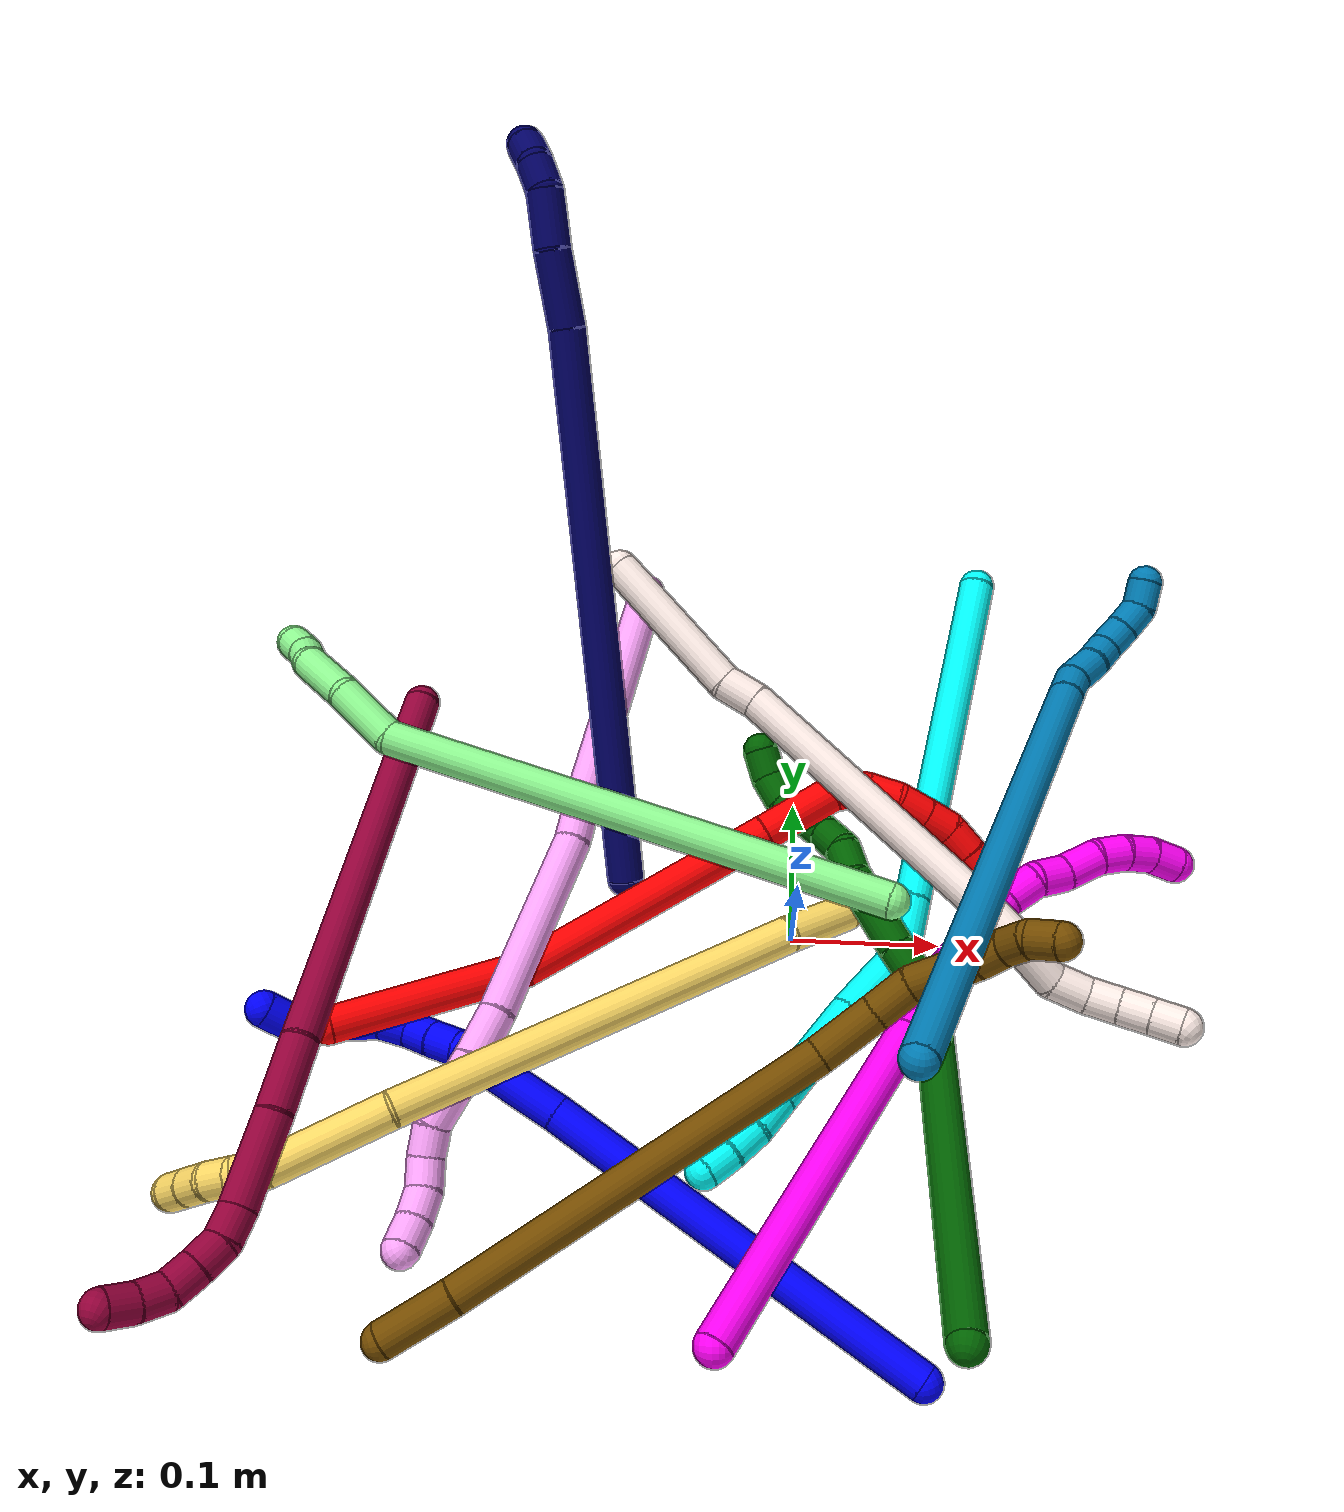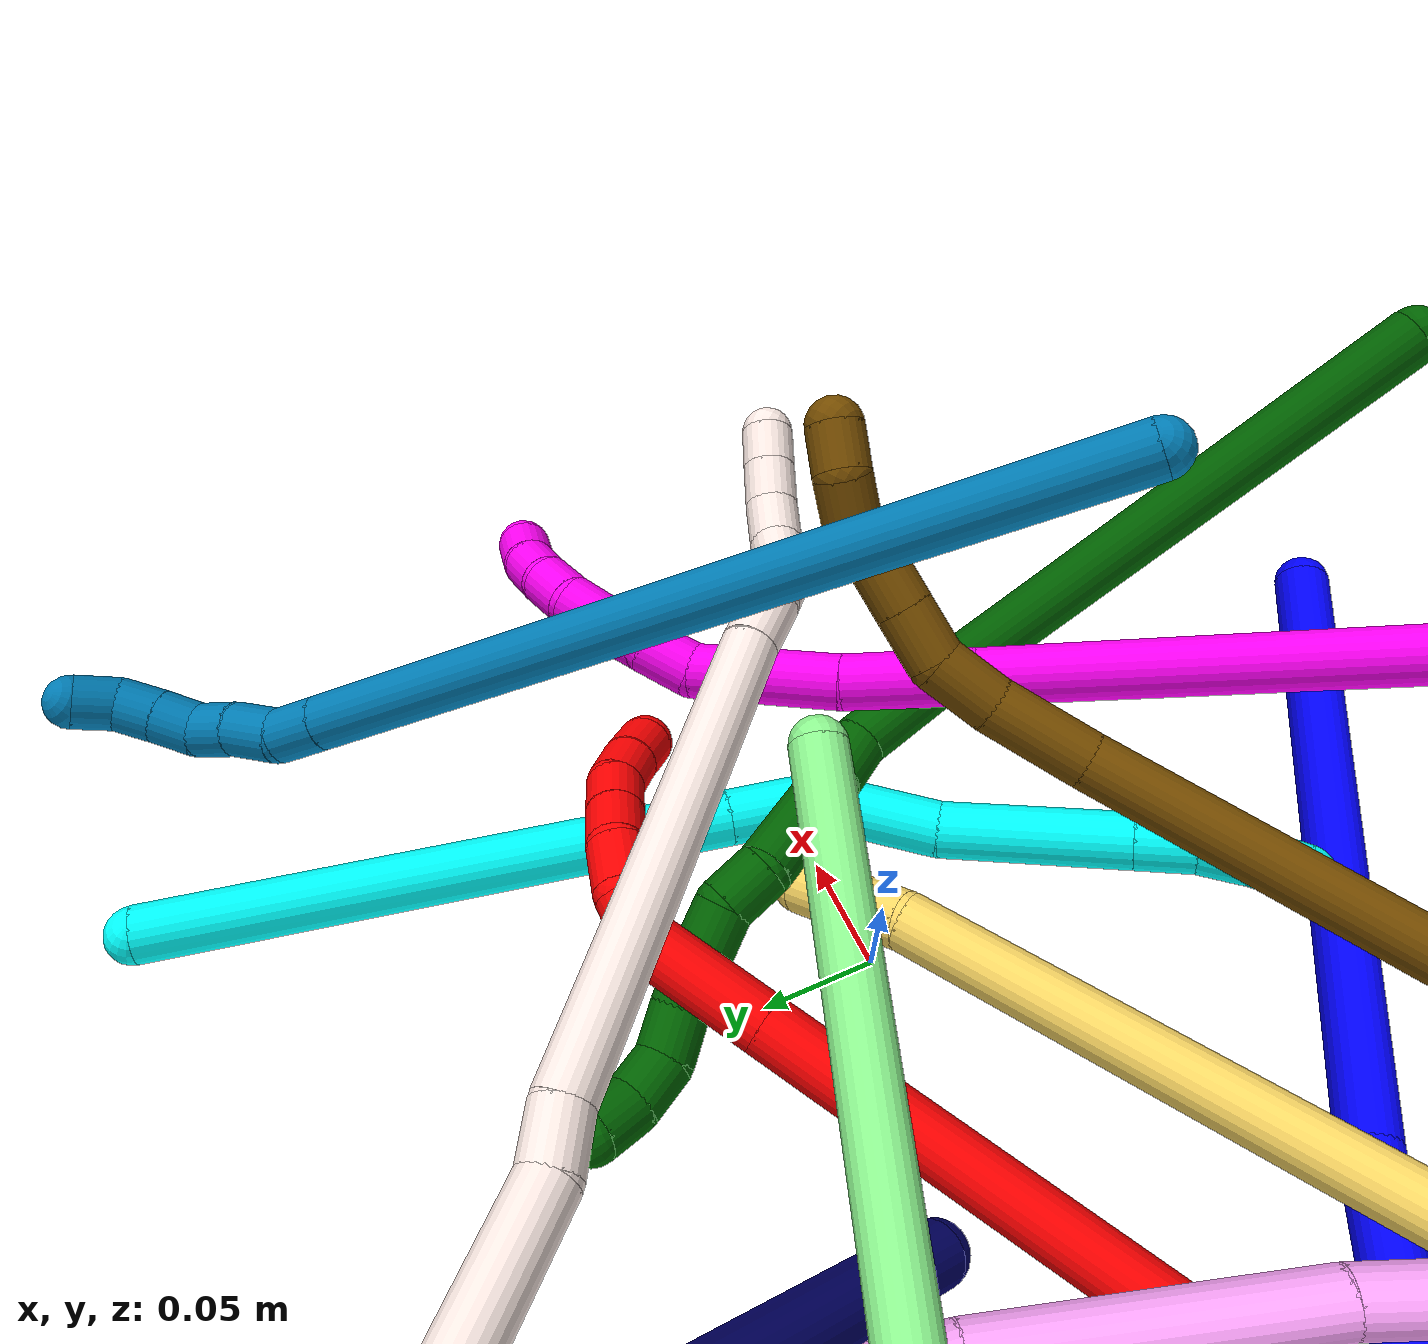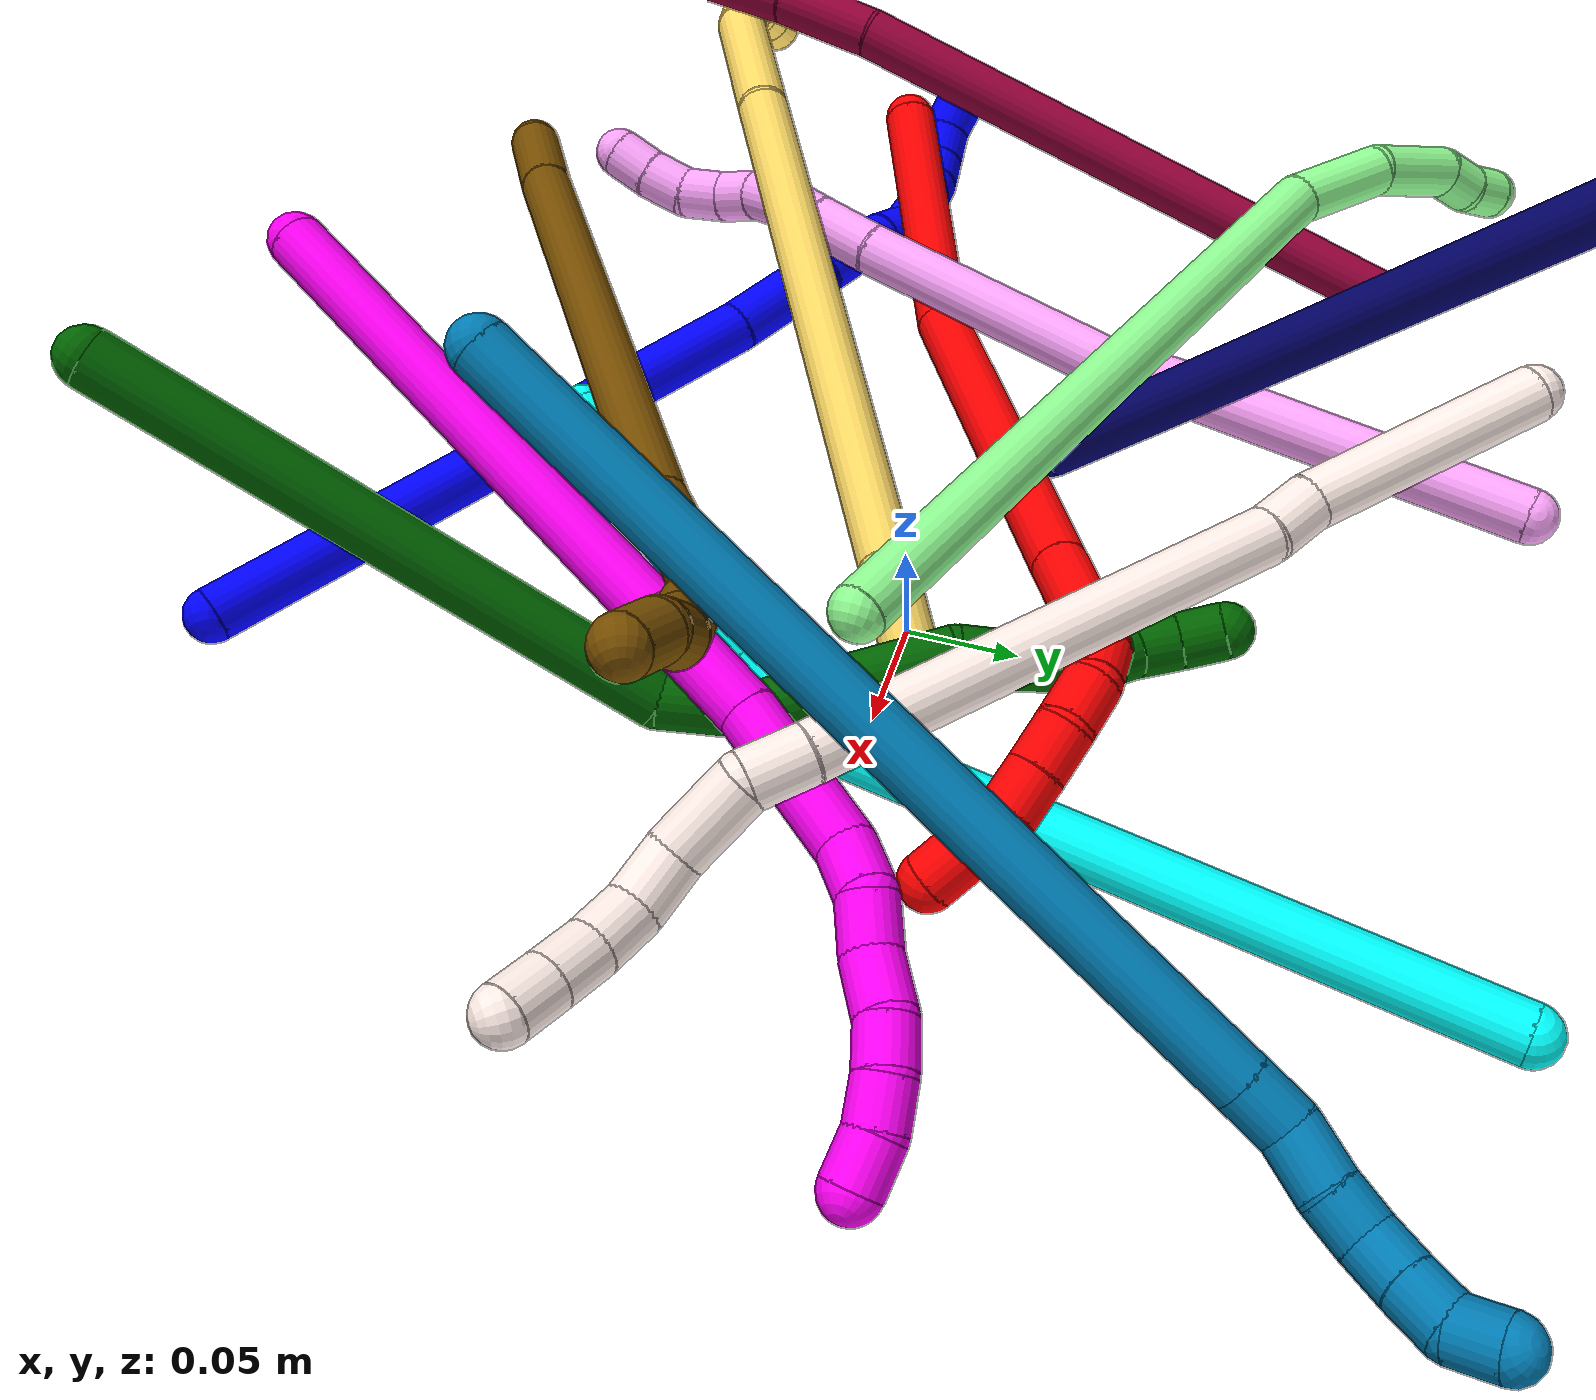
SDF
<sdf version="1.7">
 <world name="default">
  <plugin name="TubeGeneratorPlugin" filename="libtube_generator_plugin.so"/>
  <model name="photoneo_s_sensor">
   <static>1</static>
   <pose>0 0 2 1.57079 1.57079 3.14159</pose>
   <link name="link">
    <inertial><mass>0.1</mass></inertial>
    <sensor name="sensor" type="depth">
     <update_rate>30</update_rate>
     <camera>
      <horizontal_fov>1.22</horizontal_fov>
      <image><width>1920</width><height>1200</height><format>B8G8R8</format></image>
      <clip><near>0.1</near><far>4</far></clip>
      <depth_camera><output>points</output></depth_camera>
     </camera>
     <plugin name="camera_plugin" filename="libgazebo_ros_depth_camera.so">
      <baseline>0.2</baseline>
      <alwaysOn>1</alwaysOn>
      <updateRate>0.0</updateRate>
      <cameraName>camera_ir</cameraName>
      <imageTopicName>/camera/color/image_raw</imageTopicName>
      <cameraInfoTopicName>/camera/color/camera_info</cameraInfoTopicName>
      <depthImageTopicName>/camera/depth/image_raw</depthImageTopicName>
      <depthImageCameraInfoTopicName>/camera/depth/camera_info</depthImageCameraInfoTopicName>
      <pointCloudTopicName>/camera/depth/points</pointCloudTopicName>
      <frameName>fr_optical</frameName>
      <pointCloudCutoff>0.1</pointCloudCutoff>
      <pointCloudCutoffMax>2.0</pointCloudCutoffMax>
      <distortionK1>0</distortionK1>
      <distortionK2>0</distortionK2>
      <distortionK3>0</distortionK3>
      <distortionT1>0</distortionT1>
      <distortionT2>0</distortionT2>
      <CxPrime>0</CxPrime>
      <Cx>0</Cx>
      <Cy>0</Cy>
      <focalLength>0</focalLength>
      <hackBaseline>0</hackBaseline>
     </plugin>
    </sensor>
   </link>
  </model>
  <gravity>0 0 -9.8</gravity>
  <magnetic_field>6e-06 2.3e-05 -4.2e-05</magnetic_field>
  <atmosphere type="adiabatic"/>
  <physics name="default_physics" default="0" type="ode">
   <max_step_size>0.003</max_step_size>
   <real_time_factor>1</real_time_factor>
   <real_time_update_rate>1000</real_time_update_rate>
   <max_contacts>10000</max_contacts>
   <ode>
    <solver>
     <type>quick</type>
     <iters>100</iters>
     <sor>1.3</sor>
     <use_dynamic_moi_rescaling>0</use_dynamic_moi_rescaling>
    </solver>
    <constraints>
     <contact_max_correcting_vel>0</contact_max_correcting_vel>
     <contact_surface_layer>0.001</contact_surface_layer>
     <cfm>0</cfm>
     <erp>0.2</erp>
    </constraints>
   </ode>
  </physics>
  <scene><ambient>0.4 0.4 0.4 1</ambient><background>0.7 0.7 0.7 1</background><shadows>0</shadows></scene>
  <audio><device>default</device></audio>
  <spherical_coordinates>
   <surface_model>EARTH_WGS84</surface_model>
   <latitude_deg>0</latitude_deg>
   <longitude_deg>0</longitude_deg>
   <elevation>0</elevation>
   <heading_deg>0</heading_deg>
  </spherical_coordinates>
  <model name="bin">
   <static>1</static>
   <link name="bottom">
    <collision name="collision-bottom">
     <pose>0 0 -0.01 0 -0 0</pose>
     <geometry><box><size>0.8 0.6 0.02</size></box></geometry>
     <surface>
      <friction><ode><mu>100</mu><mu2>100</mu2></ode></friction>
      <contact><collide_bitmask>65535</collide_bitmask></contact>
     </surface>
    </collision>
   </link>
   <link name="west_wall">
    <collision name="collision-west_wall">
     <pose>-0.41 0 0.1 0 -0 0</pose>
     <geometry><box><size>0.02 0.6 0.2</size></box></geometry>
     <surface>
      <friction><ode><mu>100</mu><mu2>100</mu2></ode></friction>
      <contact><collide_bitmask>65535</collide_bitmask></contact>
     </surface>
    </collision>
   </link>
   <link name="east_wall">
    <collision name="collision-east_wall">
     <pose>0.41 0 0.1 0 -0 0</pose>
     <geometry><box><size>0.02 0.6 0.2</size></box></geometry>
     <surface>
      <friction><ode><mu>100</mu><mu2>100</mu2></ode></friction>
      <contact><collide_bitmask>65535</collide_bitmask></contact>
     </surface>
    </collision>
   </link>
   <link name="south_wall">
    <collision name="collision-south_wall">
     <pose>0 -0.31 0.1 0 -0 0</pose>
     <geometry><box><size>0.8 0.02 0.2</size></box></geometry>
     <surface>
      <friction><ode><mu>100</mu><mu2>100</mu2></ode></friction>
      <contact><collide_bitmask>65535</collide_bitmask></contact>
     </surface>
    </collision>
   </link>
   <link name="north_wall">
    <collision name="collision-north_wall">
     <pose>0 0.31 0.1 0 -0 0</pose>
     <geometry><box><size>0.8 0.02 0.2</size></box></geometry>
     <surface>
      <friction><ode><mu>100</mu><mu2>100</mu2></ode></friction>
      <contact><collide_bitmask>65535</collide_bitmask></contact>
     </surface>
    </collision>
   </link>
  </model>
  <model name="1">
   <static>0</static>
   <link name="1">
    <collision name="collision-cylinder-e_1_1_4">
     <pose>-0.119583 0.041073 -0.062704 -2.56169 -1.01088 2.15264</pose>
     <geometry><cylinder><radius>0.0125</radius><length>0.28227</length></cylinder></geometry>
     <surface>
      <friction><ode><mu>1.16</mu><mu2>1.16</mu2><slip1>0</slip1><slip2>0</slip2></ode></friction>
      <contact><ode><kp>1e+06</kp><kd>1</kd><max_vel>0</max_vel><min_depth>0.001</min_depth></ode></contact>
     </surface>
    </collision>
    <visual name="visual-cylinder-e_1_1_4">
     <pose>-0.119583 0.041073 -0.062704 -2.56169 -1.01088 2.15264</pose>
     <geometry><cylinder><radius>0.0125</radius><length>0.28227</length></cylinder></geometry>
     <material><ambient>0 0 1 1</ambient></material>
    </visual>
    <collision name="collision-cylinder-e_2_4_5">
     <pose>-0.262487 0.089173 -0.139473 -2.67827 -0.977617 2.30667</pose>
     <geometry><cylinder><radius>0.0125</radius><length>0.05625</length></cylinder></geometry>
     <surface>
      <friction><ode><mu>1.16</mu><mu2>1.16</mu2><slip1>0</slip1><slip2>0</slip2></ode></friction>
      <contact><ode><kp>1e+06</kp><kd>1</kd><max_vel>0</max_vel><min_depth>0.001</min_depth></ode></contact>
     </surface>
    </collision>
    <visual name="visual-cylinder-e_2_4_5">
     <pose>-0.262487 0.089173 -0.139473 -2.67827 -0.977617 2.30667</pose>
     <geometry><cylinder><radius>0.0125</radius><length>0.05625</length></cylinder></geometry>
     <material><ambient>0 0 1 1</ambient></material>
    </visual>
    <collision name="collision-cylinder-e_3_5_6">
     <pose>-0.294598 0.098908 -0.159022 -2.68291 -0.962858 2.30113</pose>
     <geometry><cylinder><radius>0.0125</radius><length>0.021419</length></cylinder></geometry>
     <surface>
      <friction><ode><mu>1.16</mu><mu2>1.16</mu2><slip1>0</slip1><slip2>0</slip2></ode></friction>
      <contact><ode><kp>1e+06</kp><kd>1</kd><max_vel>0</max_vel><min_depth>0.001</min_depth></ode></contact>
     </surface>
    </collision>
    <visual name="visual-cylinder-e_3_5_6">
     <pose>-0.294598 0.098908 -0.159022 -2.68291 -0.962858 2.30113</pose>
     <geometry><cylinder><radius>0.0125</radius><length>0.021419</length></cylinder></geometry>
     <material><ambient>0 0 1 1</ambient></material>
    </visual>
    <collision name="collision-cylinder-e_4_6_7">
     <pose>-0.309818 0.107254 -0.169708 -2.31594 -0.697576 1.38586</pose>
     <geometry><cylinder><radius>0.0125</radius><length>0.020015</length></cylinder></geometry>
     <surface>
      <friction><ode><mu>1.16</mu><mu2>1.16</mu2><slip1>0</slip1><slip2>0</slip2></ode></friction>
      <contact><ode><kp>1e+06</kp><kd>1</kd><max_vel>0</max_vel><min_depth>0.001</min_depth></ode></contact>
     </surface>
    </collision>
    <visual name="visual-cylinder-e_4_6_7">
     <pose>-0.309818 0.107254 -0.169708 -2.31594 -0.697576 1.38586</pose>
     <geometry><cylinder><radius>0.0125</radius><length>0.020015</length></cylinder></geometry>
     <material><ambient>0 0 1 1</ambient></material>
    </visual>
    <collision name="collision-cylinder-e_5_7_8">
     <pose>-0.322891 0.118803 -0.179507 -2.23183 -0.725667 1.32015</pose>
     <geometry><cylinder><radius>0.0125</radius><length>0.020025</length></cylinder></geometry>
     <surface>
      <friction><ode><mu>1.16</mu><mu2>1.16</mu2><slip1>0</slip1><slip2>0</slip2></ode></friction>
      <contact><ode><kp>1e+06</kp><kd>1</kd><max_vel>0</max_vel><min_depth>0.001</min_depth></ode></contact>
     </surface>
    </collision>
    <visual name="visual-cylinder-e_5_7_8">
     <pose>-0.322891 0.118803 -0.179507 -2.23183 -0.725667 1.32015</pose>
     <geometry><cylinder><radius>0.0125</radius><length>0.020025</length></cylinder></geometry>
     <material><ambient>0 0 1 1</ambient></material>
    </visual>
    <collision name="collision-cylinder-e_6_8_9">
     <pose>-0.335783 0.126687 -0.191661 -2.88643 -0.674794 2.44048</pose>
     <geometry><cylinder><radius>0.0125</radius><length>0.020002</length></cylinder></geometry>
     <surface>
      <friction><ode><mu>1.16</mu><mu2>1.16</mu2><slip1>0</slip1><slip2>0</slip2></ode></friction>
      <contact><ode><kp>1e+06</kp><kd>1</kd><max_vel>0</max_vel><min_depth>0.001</min_depth></ode></contact>
     </surface>
    </collision>
    <visual name="visual-cylinder-e_6_8_9">
     <pose>-0.335783 0.126687 -0.191661 -2.88643 -0.674794 2.44048</pose>
     <geometry><cylinder><radius>0.0125</radius><length>0.020002</length></cylinder></geometry>
     <material><ambient>0 0 1 1</ambient></material>
    </visual>
    <collision name="collision-cylinder-e_7_9_10">
     <pose>-0.345761 0.132951 -0.207443 -2.66054 -0.382238 1.33579</pose>
     <geometry><cylinder><radius>0.0125</radius><length>0.020001</length></cylinder></geometry>
     <surface>
      <friction><ode><mu>1.16</mu><mu2>1.16</mu2><slip1>0</slip1><slip2>0</slip2></ode></friction>
      <contact><ode><kp>1e+06</kp><kd>1</kd><max_vel>0</max_vel><min_depth>0.001</min_depth></ode></contact>
     </surface>
    </collision>
    <visual name="visual-cylinder-e_7_9_10">
     <pose>-0.345761 0.132951 -0.207443 -2.66054 -0.382238 1.33579</pose>
     <geometry><cylinder><radius>0.0125</radius><length>0.020001</length></cylinder></geometry>
     <material><ambient>0 0 1 1</ambient></material>
    </visual>
    <collision name="collision-cylinder-e_8_10_11">
     <pose>-0.352532 0.140555 -0.224608 -2.78687 -0.308786 1.43</pose>
     <geometry><cylinder><radius>0.0125</radius><length>0.020012</length></cylinder></geometry>
     <surface>
      <friction><ode><mu>1.16</mu><mu2>1.16</mu2><slip1>0</slip1><slip2>0</slip2></ode></friction>
      <contact><ode><kp>1e+06</kp><kd>1</kd><max_vel>0</max_vel><min_depth>0.001</min_depth></ode></contact>
     </surface>
    </collision>
    <visual name="visual-cylinder-e_8_10_11">
     <pose>-0.352532 0.140555 -0.224608 -2.78687 -0.308786 1.43</pose>
     <geometry><cylinder><radius>0.0125</radius><length>0.020012</length></cylinder></geometry>
     <material><ambient>0 0 1 1</ambient></material>
    </visual>
    <collision name="collision-cylinder-e_9_11_12">
     <pose>-0.359744 0.143836 -0.242639 3.13826 -0.430109 -3.12631</pose>
     <geometry><cylinder><radius>0.0125</radius><length>0.020006</length></cylinder></geometry>
     <surface>
      <friction><ode><mu>1.16</mu><mu2>1.16</mu2><slip1>0</slip1><slip2>0</slip2></ode></friction>
      <contact><ode><kp>1e+06</kp><kd>1</kd><max_vel>0</max_vel><min_depth>0.001</min_depth></ode></contact>
     </surface>
    </collision>
    <visual name="visual-cylinder-e_9_11_12">
     <pose>-0.359744 0.143836 -0.242639 3.13826 -0.430109 -3.12631</pose>
     <geometry><cylinder><radius>0.0125</radius><length>0.020006</length></cylinder></geometry>
     <material><ambient>0 0 1 1</ambient></material>
    </visual>
    <collision name="collision-cylinder-e_10_12_2">
     <pose>-0.370534 0.14138 -0.258823 2.81203 -0.723348 -2.31334</pose>
     <geometry><cylinder><radius>0.0125</radius><length>0.020001</length></cylinder></geometry>
     <surface>
      <friction><ode><mu>1.16</mu><mu2>1.16</mu2><slip1>0</slip1><slip2>0</slip2></ode></friction>
      <contact><ode><kp>1e+06</kp><kd>1</kd><max_vel>0</max_vel><min_depth>0.001</min_depth></ode></contact>
     </surface>
    </collision>
    <visual name="visual-cylinder-e_10_12_2">
     <pose>-0.370534 0.14138 -0.258823 2.81203 -0.723348 -2.31334</pose>
     <geometry><cylinder><radius>0.0125</radius><length>0.020001</length></cylinder></geometry>
     <material><ambient>0 0 1 1</ambient></material>
    </visual>
    <collision name="collision-sphere-2">
     <pose>-0.377153 0.138954 -0.265916 0 -0 0</pose>
     <geometry><sphere><radius>0.0125</radius></sphere></geometry>
     <surface>
      <friction><ode><mu>1.16</mu><mu2>1.16</mu2><slip1>0</slip1><slip2>0</slip2></ode></friction>
      <contact><ode><kp>1e+06</kp><kd>1</kd><max_vel>0</max_vel><min_depth>0.001</min_depth></ode></contact>
     </surface>
    </collision>
    <visual name="visual-sphere-2">
     <pose>-0.377153 0.138954 -0.265916 0 -0 0</pose>
     <geometry><sphere><radius>0.0125</radius></sphere></geometry>
     <material><ambient>0 0 1 1</ambient></material>
    </visual>
    <collision name="collision-sphere-12">
     <pose>-0.363915 0.143806 -0.251731 0 -0 0</pose>
     <geometry><sphere><radius>0.0125</radius></sphere></geometry>
     <surface>
      <friction><ode><mu>1.16</mu><mu2>1.16</mu2><slip1>0</slip1><slip2>0</slip2></ode></friction>
      <contact><ode><kp>1e+06</kp><kd>1</kd><max_vel>0</max_vel><min_depth>0.001</min_depth></ode></contact>
     </surface>
    </collision>
    <visual name="visual-sphere-12">
     <pose>-0.363915 0.143806 -0.251731 0 -0 0</pose>
     <geometry><sphere><radius>0.0125</radius></sphere></geometry>
     <material><ambient>0 0 1 1</ambient></material>
    </visual>
    <collision name="collision-sphere-11">
     <pose>-0.355573 0.143866 -0.233547 0 -0 0</pose>
     <geometry><sphere><radius>0.0125</radius></sphere></geometry>
     <surface>
      <friction><ode><mu>1.16</mu><mu2>1.16</mu2><slip1>0</slip1><slip2>0</slip2></ode></friction>
      <contact><ode><kp>1e+06</kp><kd>1</kd><max_vel>0</max_vel><min_depth>0.001</min_depth></ode></contact>
     </surface>
    </collision>
    <visual name="visual-sphere-11">
     <pose>-0.355573 0.143866 -0.233547 0 -0 0</pose>
     <geometry><sphere><radius>0.0125</radius></sphere></geometry>
     <material><ambient>0 0 1 1</ambient></material>
    </visual>
    <collision name="collision-sphere-10">
     <pose>-0.349492 0.137244 -0.215669 0 -0 0</pose>
     <geometry><sphere><radius>0.0125</radius></sphere></geometry>
     <surface>
      <friction><ode><mu>1.16</mu><mu2>1.16</mu2><slip1>0</slip1><slip2>0</slip2></ode></friction>
      <contact><ode><kp>1e+06</kp><kd>1</kd><max_vel>0</max_vel><min_depth>0.001</min_depth></ode></contact>
     </surface>
    </collision>
    <visual name="visual-sphere-10">
     <pose>-0.349492 0.137244 -0.215669 0 -0 0</pose>
     <geometry><sphere><radius>0.0125</radius></sphere></geometry>
     <material><ambient>0 0 1 1</ambient></material>
    </visual>
    <collision name="collision-sphere-9">
     <pose>-0.342031 0.128658 -0.199217 0 -0 0</pose>
     <geometry><sphere><radius>0.0125</radius></sphere></geometry>
     <surface>
      <friction><ode><mu>1.16</mu><mu2>1.16</mu2><slip1>0</slip1><slip2>0</slip2></ode></friction>
      <contact><ode><kp>1e+06</kp><kd>1</kd><max_vel>0</max_vel><min_depth>0.001</min_depth></ode></contact>
     </surface>
    </collision>
    <visual name="visual-sphere-9">
     <pose>-0.342031 0.128658 -0.199217 0 -0 0</pose>
     <geometry><sphere><radius>0.0125</radius></sphere></geometry>
     <material><ambient>0 0 1 1</ambient></material>
    </visual>
    <collision name="collision-sphere-4">
     <pose>-0.239167 0.082147 -0.125409 0 -0 0</pose>
     <geometry><sphere><radius>0.0125</radius></sphere></geometry>
     <surface>
      <friction><ode><mu>1.16</mu><mu2>1.16</mu2><slip1>0</slip1><slip2>0</slip2></ode></friction>
      <contact><ode><kp>1e+06</kp><kd>1</kd><max_vel>0</max_vel><min_depth>0.001</min_depth></ode></contact>
     </surface>
    </collision>
    <visual name="visual-sphere-4">
     <pose>-0.239167 0.082147 -0.125409 0 -0 0</pose>
     <geometry><sphere><radius>0.0125</radius></sphere></geometry>
     <material><ambient>0 0 1 1</ambient></material>
    </visual>
    <collision name="collision-sphere-1">
     <geometry><sphere><radius>0.0125</radius></sphere></geometry>
     <surface>
      <friction><ode><mu>1.16</mu><mu2>1.16</mu2><slip1>0</slip1><slip2>0</slip2></ode></friction>
      <contact><ode><kp>1e+06</kp><kd>1</kd><max_vel>0</max_vel><min_depth>0.001</min_depth></ode></contact>
     </surface>
    </collision>
    <visual name="visual-sphere-1">
     <geometry><sphere><radius>0.0125</radius></sphere></geometry>
     <material><ambient>0 0 1 1</ambient></material>
    </visual>
    <collision name="collision-sphere-8">
     <pose>-0.329536 0.124716 -0.184105 0 -0 0</pose>
     <geometry><sphere><radius>0.0125</radius></sphere></geometry>
     <surface>
      <friction><ode><mu>1.16</mu><mu2>1.16</mu2><slip1>0</slip1><slip2>0</slip2></ode></friction>
      <contact><ode><kp>1e+06</kp><kd>1</kd><max_vel>0</max_vel><min_depth>0.001</min_depth></ode></contact>
     </surface>
    </collision>
    <visual name="visual-sphere-8">
     <pose>-0.329536 0.124716 -0.184105 0 -0 0</pose>
     <geometry><sphere><radius>0.0125</radius></sphere></geometry>
     <material><ambient>0 0 1 1</ambient></material>
    </visual>
    <collision name="collision-sphere-5">
     <pose>-0.285807 0.0962 -0.153537 0 -0 0</pose>
     <geometry><sphere><radius>0.0125</radius></sphere></geometry>
     <surface>
      <friction><ode><mu>1.16</mu><mu2>1.16</mu2><slip1>0</slip1><slip2>0</slip2></ode></friction>
      <contact><ode><kp>1e+06</kp><kd>1</kd><max_vel>0</max_vel><min_depth>0.001</min_depth></ode></contact>
     </surface>
    </collision>
    <visual name="visual-sphere-5">
     <pose>-0.285807 0.0962 -0.153537 0 -0 0</pose>
     <geometry><sphere><radius>0.0125</radius></sphere></geometry>
     <material><ambient>0 0 1 1</ambient></material>
    </visual>
    <collision name="collision-sphere-6">
     <pose>-0.303389 0.101617 -0.164507 0 -0 0</pose>
     <geometry><sphere><radius>0.0125</radius></sphere></geometry>
     <surface>
      <friction><ode><mu>1.16</mu><mu2>1.16</mu2><slip1>0</slip1><slip2>0</slip2></ode></friction>
      <contact><ode><kp>1e+06</kp><kd>1</kd><max_vel>0</max_vel><min_depth>0.001</min_depth></ode></contact>
     </surface>
    </collision>
    <visual name="visual-sphere-6">
     <pose>-0.303389 0.101617 -0.164507 0 -0 0</pose>
     <geometry><sphere><radius>0.0125</radius></sphere></geometry>
     <material><ambient>0 0 1 1</ambient></material>
    </visual>
    <collision name="collision-sphere-7">
     <pose>-0.316246 0.112891 -0.174908 0 -0 0</pose>
     <geometry><sphere><radius>0.0125</radius></sphere></geometry>
     <surface>
      <friction><ode><mu>1.16</mu><mu2>1.16</mu2><slip1>0</slip1><slip2>0</slip2></ode></friction>
      <contact><ode><kp>1e+06</kp><kd>1</kd><max_vel>0</max_vel><min_depth>0.001</min_depth></ode></contact>
     </surface>
    </collision>
    <visual name="visual-sphere-7">
     <pose>-0.316246 0.112891 -0.174908 0 -0 0</pose>
     <geometry><sphere><radius>0.0125</radius></sphere></geometry>
     <material><ambient>0 0 1 1</ambient></material>
    </visual>
    <inertial>
     <pose>-0.205582 0.07393 -0.116901 0 -0 0</pose>
     <mass>0.5</mass>
     <inertia>
      <ixx>0.00026</ixx>
      <ixy>0</ixy>
      <ixz>0</ixz>
      <iyy>0.002479</iyy>
      <iyz>0</iyz>
      <izz>0.001041</izz>
     </inertia>
    </inertial>
   </link>
   <pose>0.08577 -0.287506 0.012483 -1.83441 0.213292 -1.11608</pose>
  </model>
  <model name="2">
   <static>0</static>
   <link name="2">
    <collision name="collision-cylinder-e_1_1_4">
     <pose>0.040327 0.018699 -0.050124 -2.78453 0.645927 -2.15261</pose>
     <geometry><cylinder><radius>0.0125</radius><length>0.133991</length></cylinder></geometry>
     <surface>
      <friction><ode><mu>1.16</mu><mu2>1.16</mu2><slip1>0</slip1><slip2>0</slip2></ode></friction>
      <contact><ode><kp>1e+06</kp><kd>1</kd><max_vel>0</max_vel><min_depth>0.001</min_depth></ode></contact>
     </surface>
    </collision>
    <visual name="visual-cylinder-e_1_1_4">
     <pose>0.040327 0.018699 -0.050124 -2.78453 0.645927 -2.15261</pose>
     <geometry><cylinder><radius>0.0125</radius><length>0.133991</length></cylinder></geometry>
     <material><ambient>1 0 0 1</ambient></material>
    </visual>
    <collision name="collision-cylinder-e_2_4_5">
     <pose>0.108208 0.071814 -0.181865 -2.74254 0.301584 -1.28879</pose>
     <geometry><cylinder><radius>0.0125</radius><length>0.185525</length></cylinder></geometry>
     <surface>
      <friction><ode><mu>1.16</mu><mu2>1.16</mu2><slip1>0</slip1><slip2>0</slip2></ode></friction>
      <contact><ode><kp>1e+06</kp><kd>1</kd><max_vel>0</max_vel><min_depth>0.001</min_depth></ode></contact>
     </surface>
    </collision>
    <visual name="visual-cylinder-e_2_4_5">
     <pose>0.108208 0.071814 -0.181865 -2.74254 0.301584 -1.28879</pose>
     <geometry><cylinder><radius>0.0125</radius><length>0.185525</length></cylinder></geometry>
     <material><ambient>1 0 0 1</ambient></material>
    </visual>
    <collision name="collision-cylinder-e_3_5_6">
     <pose>0.143556 0.116607 -0.287785 -2.73803 0.286842 -1.22942</pose>
     <geometry><cylinder><radius>0.0125</radius><length>0.055104</length></cylinder></geometry>
     <surface>
      <friction><ode><mu>1.16</mu><mu2>1.16</mu2><slip1>0</slip1><slip2>0</slip2></ode></friction>
      <contact><ode><kp>1e+06</kp><kd>1</kd><max_vel>0</max_vel><min_depth>0.001</min_depth></ode></contact>
     </surface>
    </collision>
    <visual name="visual-cylinder-e_3_5_6">
     <pose>0.143556 0.116607 -0.287785 -2.73803 0.286842 -1.22942</pose>
     <geometry><cylinder><radius>0.0125</radius><length>0.055104</length></cylinder></geometry>
     <material><ambient>1 0 0 1</ambient></material>
    </visual>
    <collision name="collision-cylinder-e_4_6_7">
     <pose>0.155656 0.134859 -0.317849 -2.20243 0.415483 -0.787399</pose>
     <geometry><cylinder><radius>0.0125</radius><length>0.021327</length></cylinder></geometry>
     <surface>
      <friction><ode><mu>1.16</mu><mu2>1.16</mu2><slip1>0</slip1><slip2>0</slip2></ode></friction>
      <contact><ode><kp>1e+06</kp><kd>1</kd><max_vel>0</max_vel><min_depth>0.001</min_depth></ode></contact>
     </surface>
    </collision>
    <visual name="visual-cylinder-e_4_6_7">
     <pose>0.155656 0.134859 -0.317849 -2.20243 0.415483 -0.787399</pose>
     <geometry><cylinder><radius>0.0125</radius><length>0.021327</length></cylinder></geometry>
     <material><ambient>1 0 0 1</ambient></material>
    </visual>
    <collision name="collision-cylinder-e_5_7_8">
     <pose>0.167758 0.150279 -0.326416 -1.92677 0.769457 -1.05496</pose>
     <geometry><cylinder><radius>0.0125</radius><length>0.022417</length></cylinder></geometry>
     <surface>
      <friction><ode><mu>1.16</mu><mu2>1.16</mu2><slip1>0</slip1><slip2>0</slip2></ode></friction>
      <contact><ode><kp>1e+06</kp><kd>1</kd><max_vel>0</max_vel><min_depth>0.001</min_depth></ode></contact>
     </surface>
    </collision>
    <visual name="visual-cylinder-e_5_7_8">
     <pose>0.167758 0.150279 -0.326416 -1.92677 0.769457 -1.05496</pose>
     <geometry><cylinder><radius>0.0125</radius><length>0.022417</length></cylinder></geometry>
     <material><ambient>1 0 0 1</ambient></material>
    </visual>
    <collision name="collision-cylinder-e_6_8_9">
     <pose>0.184715 0.163241 -0.33036 -1.77795 1.02727 -1.21477</pose>
     <geometry><cylinder><radius>0.0125</radius><length>0.021402</length></cylinder></geometry>
     <surface>
      <friction><ode><mu>1.16</mu><mu2>1.16</mu2><slip1>0</slip1><slip2>0</slip2></ode></friction>
      <contact><ode><kp>1e+06</kp><kd>1</kd><max_vel>0</max_vel><min_depth>0.001</min_depth></ode></contact>
     </surface>
    </collision>
    <visual name="visual-cylinder-e_6_8_9">
     <pose>0.184715 0.163241 -0.33036 -1.77795 1.02727 -1.21477</pose>
     <geometry><cylinder><radius>0.0125</radius><length>0.021402</length></cylinder></geometry>
     <material><ambient>1 0 0 1</ambient></material>
    </visual>
    <collision name="collision-cylinder-e_7_9_10">
     <pose>0.202538 0.173688 -0.332304 -1.72971 1.03917 -1.18198</pose>
     <geometry><cylinder><radius>0.0125</radius><length>0.020102</length></cylinder></geometry>
     <surface>
      <friction><ode><mu>1.16</mu><mu2>1.16</mu2><slip1>0</slip1><slip2>0</slip2></ode></friction>
      <contact><ode><kp>1e+06</kp><kd>1</kd><max_vel>0</max_vel><min_depth>0.001</min_depth></ode></contact>
     </surface>
    </collision>
    <visual name="visual-cylinder-e_7_9_10">
     <pose>0.202538 0.173688 -0.332304 -1.72971 1.03917 -1.18198</pose>
     <geometry><cylinder><radius>0.0125</radius><length>0.020102</length></cylinder></geometry>
     <material><ambient>1 0 0 1</ambient></material>
    </visual>
    <collision name="collision-cylinder-e_8_10_11">
     <pose>0.219758 0.183375 -0.330746 -1.10082 1.02282 -0.663351</pose>
     <geometry><cylinder><radius>0.0125</radius><length>0.020047</length></cylinder></geometry>
     <surface>
      <friction><ode><mu>1.16</mu><mu2>1.16</mu2><slip1>0</slip1><slip2>0</slip2></ode></friction>
      <contact><ode><kp>1e+06</kp><kd>1</kd><max_vel>0</max_vel><min_depth>0.001</min_depth></ode></contact>
     </surface>
    </collision>
    <visual name="visual-cylinder-e_8_10_11">
     <pose>0.219758 0.183375 -0.330746 -1.10082 1.02282 -0.663351</pose>
     <geometry><cylinder><radius>0.0125</radius><length>0.020047</length></cylinder></geometry>
     <material><ambient>1 0 0 1</ambient></material>
    </visual>
    <collision name="collision-cylinder-e_9_11_2">
     <pose>0.236997 0.192108 -0.32541 -0.941256 1.04442 -0.569653</pose>
     <geometry><cylinder><radius>0.0125</radius><length>0.020084</length></cylinder></geometry>
     <surface>
      <friction><ode><mu>1.16</mu><mu2>1.16</mu2><slip1>0</slip1><slip2>0</slip2></ode></friction>
      <contact><ode><kp>1e+06</kp><kd>1</kd><max_vel>0</max_vel><min_depth>0.001</min_depth></ode></contact>
     </surface>
    </collision>
    <visual name="visual-cylinder-e_9_11_2">
     <pose>0.236997 0.192108 -0.32541 -0.941256 1.04442 -0.569653</pose>
     <geometry><cylinder><radius>0.0125</radius><length>0.020084</length></cylinder></geometry>
     <material><ambient>1 0 0 1</ambient></material>
    </visual>
    <collision name="collision-sphere-2">
     <pose>0.24568 0.196187 -0.32244 0 -0 0</pose>
     <geometry><sphere><radius>0.0125</radius></sphere></geometry>
     <surface>
      <friction><ode><mu>1.16</mu><mu2>1.16</mu2><slip1>0</slip1><slip2>0</slip2></ode></friction>
      <contact><ode><kp>1e+06</kp><kd>1</kd><max_vel>0</max_vel><min_depth>0.001</min_depth></ode></contact>
     </surface>
    </collision>
    <visual name="visual-sphere-2">
     <pose>0.24568 0.196187 -0.32244 0 -0 0</pose>
     <geometry><sphere><radius>0.0125</radius></sphere></geometry>
     <material><ambient>1 0 0 1</ambient></material>
    </visual>
    <collision name="collision-sphere-11">
     <pose>0.228314 0.18803 -0.328381 0 -0 0</pose>
     <geometry><sphere><radius>0.0125</radius></sphere></geometry>
     <surface>
      <friction><ode><mu>1.16</mu><mu2>1.16</mu2><slip1>0</slip1><slip2>0</slip2></ode></friction>
      <contact><ode><kp>1e+06</kp><kd>1</kd><max_vel>0</max_vel><min_depth>0.001</min_depth></ode></contact>
     </surface>
    </collision>
    <visual name="visual-sphere-11">
     <pose>0.228314 0.18803 -0.328381 0 -0 0</pose>
     <geometry><sphere><radius>0.0125</radius></sphere></geometry>
     <material><ambient>1 0 0 1</ambient></material>
    </visual>
    <collision name="collision-sphere-10">
     <pose>0.211202 0.178719 -0.333111 0 -0 0</pose>
     <geometry><sphere><radius>0.0125</radius></sphere></geometry>
     <surface>
      <friction><ode><mu>1.16</mu><mu2>1.16</mu2><slip1>0</slip1><slip2>0</slip2></ode></friction>
      <contact><ode><kp>1e+06</kp><kd>1</kd><max_vel>0</max_vel><min_depth>0.001</min_depth></ode></contact>
     </surface>
    </collision>
    <visual name="visual-sphere-10">
     <pose>0.211202 0.178719 -0.333111 0 -0 0</pose>
     <geometry><sphere><radius>0.0125</radius></sphere></geometry>
     <material><ambient>1 0 0 1</ambient></material>
    </visual>
    <collision name="collision-sphere-9">
     <pose>0.193874 0.168657 -0.331498 0 -0 0</pose>
     <geometry><sphere><radius>0.0125</radius></sphere></geometry>
     <surface>
      <friction><ode><mu>1.16</mu><mu2>1.16</mu2><slip1>0</slip1><slip2>0</slip2></ode></friction>
      <contact><ode><kp>1e+06</kp><kd>1</kd><max_vel>0</max_vel><min_depth>0.001</min_depth></ode></contact>
     </surface>
    </collision>
    <visual name="visual-sphere-9">
     <pose>0.193874 0.168657 -0.331498 0 -0 0</pose>
     <geometry><sphere><radius>0.0125</radius></sphere></geometry>
     <material><ambient>1 0 0 1</ambient></material>
    </visual>
    <collision name="collision-sphere-4">
     <pose>0.080654 0.037398 -0.100249 0 -0 0</pose>
     <geometry><sphere><radius>0.0125</radius></sphere></geometry>
     <surface>
      <friction><ode><mu>1.16</mu><mu2>1.16</mu2><slip1>0</slip1><slip2>0</slip2></ode></friction>
      <contact><ode><kp>1e+06</kp><kd>1</kd><max_vel>0</max_vel><min_depth>0.001</min_depth></ode></contact>
     </surface>
    </collision>
    <visual name="visual-sphere-4">
     <pose>0.080654 0.037398 -0.100249 0 -0 0</pose>
     <geometry><sphere><radius>0.0125</radius></sphere></geometry>
     <material><ambient>1 0 0 1</ambient></material>
    </visual>
    <collision name="collision-sphere-1">
     <geometry><sphere><radius>0.0125</radius></sphere></geometry>
     <surface>
      <friction><ode><mu>1.16</mu><mu2>1.16</mu2><slip1>0</slip1><slip2>0</slip2></ode></friction>
      <contact><ode><kp>1e+06</kp><kd>1</kd><max_vel>0</max_vel><min_depth>0.001</min_depth></ode></contact>
     </surface>
    </collision>
    <visual name="visual-sphere-1">
     <geometry><sphere><radius>0.0125</radius></sphere></geometry>
     <material><ambient>1 0 0 1</ambient></material>
    </visual>
    <collision name="collision-sphere-8">
     <pose>0.175556 0.157825 -0.329221 0 -0 0</pose>
     <geometry><sphere><radius>0.0125</radius></sphere></geometry>
     <surface>
      <friction><ode><mu>1.16</mu><mu2>1.16</mu2><slip1>0</slip1><slip2>0</slip2></ode></friction>
      <contact><ode><kp>1e+06</kp><kd>1</kd><max_vel>0</max_vel><min_depth>0.001</min_depth></ode></contact>
     </surface>
    </collision>
    <visual name="visual-sphere-8">
     <pose>0.175556 0.157825 -0.329221 0 -0 0</pose>
     <geometry><sphere><radius>0.0125</radius></sphere></geometry>
     <material><ambient>1 0 0 1</ambient></material>
    </visual>
    <collision name="collision-sphere-5">
     <pose>0.135761 0.10623 -0.263481 0 -0 0</pose>
     <geometry><sphere><radius>0.0125</radius></sphere></geometry>
     <surface>
      <friction><ode><mu>1.16</mu><mu2>1.16</mu2><slip1>0</slip1><slip2>0</slip2></ode></friction>
      <contact><ode><kp>1e+06</kp><kd>1</kd><max_vel>0</max_vel><min_depth>0.001</min_depth></ode></contact>
     </surface>
    </collision>
    <visual name="visual-sphere-5">
     <pose>0.135761 0.10623 -0.263481 0 -0 0</pose>
     <geometry><sphere><radius>0.0125</radius></sphere></geometry>
     <material><ambient>1 0 0 1</ambient></material>
    </visual>
    <collision name="collision-sphere-6">
     <pose>0.151352 0.126985 -0.312088 0 -0 0</pose>
     <geometry><sphere><radius>0.0125</radius></sphere></geometry>
     <surface>
      <friction><ode><mu>1.16</mu><mu2>1.16</mu2><slip1>0</slip1><slip2>0</slip2></ode></friction>
      <contact><ode><kp>1e+06</kp><kd>1</kd><max_vel>0</max_vel><min_depth>0.001</min_depth></ode></contact>
     </surface>
    </collision>
    <visual name="visual-sphere-6">
     <pose>0.151352 0.126985 -0.312088 0 -0 0</pose>
     <geometry><sphere><radius>0.0125</radius></sphere></geometry>
     <material><ambient>1 0 0 1</ambient></material>
    </visual>
    <collision name="collision-sphere-7">
     <pose>0.15996 0.142733 -0.32361 0 -0 0</pose>
     <geometry><sphere><radius>0.0125</radius></sphere></geometry>
     <surface>
      <friction><ode><mu>1.16</mu><mu2>1.16</mu2><slip1>0</slip1><slip2>0</slip2></ode></friction>
      <contact><ode><kp>1e+06</kp><kd>1</kd><max_vel>0</max_vel><min_depth>0.001</min_depth></ode></contact>
     </surface>
    </collision>
    <visual name="visual-sphere-7">
     <pose>0.15996 0.142733 -0.32361 0 -0 0</pose>
     <geometry><sphere><radius>0.0125</radius></sphere></geometry>
     <material><ambient>1 0 0 1</ambient></material>
    </visual>
    <inertial>
     <pose>0.11532 0.086038 -0.194655 0 -0 0</pose>
     <mass>0.5</mass>
     <inertia>
      <ixx>-0.00057</ixx>
      <ixy>0</ixy>
      <ixz>0</ixz>
      <iyy>-0.00057</iyy>
      <iyz>0</iyz>
      <izz>-0.00059</izz>
     </inertia>
    </inertial>
   </link>
   <pose>-0.297897 -0.087503 0.045761 1.83597 0.919744 -0.310313</pose>
  </model>
  <model name="3">
   <static>0</static>
   <link name="3">
    <collision name="collision-cylinder-e_1_1_4">
     <pose>-0.096451 -0.079969 -0.019293 1.80753 -0.864621 -1.0601</pose>
     <geometry><cylinder><radius>0.0125</radius><length>0.253535</length></cylinder></geometry>
     <surface>
      <friction><ode><mu>1.16</mu><mu2>1.16</mu2><slip1>0</slip1><slip2>0</slip2></ode></friction>
      <contact><ode><kp>1e+06</kp><kd>1</kd><max_vel>0</max_vel><min_depth>0.001</min_depth></ode></contact>
     </surface>
    </collision>
    <visual name="visual-cylinder-e_1_1_4">
     <pose>-0.096451 -0.079969 -0.019293 1.80753 -0.864621 -1.0601</pose>
     <geometry><cylinder><radius>0.0125</radius><length>0.253535</length></cylinder></geometry>
     <material><ambient>0.003922 1 0.996078 1</ambient></material>
    </visual>
    <collision name="collision-cylinder-e_2_4_5">
     <pose>-0.208193 -0.172628 -0.04177 1.81656 -0.862998 -1.06635</pose>
     <geometry><cylinder><radius>0.0125</radius><length>0.040249</length></cylinder></geometry>
     <surface>
      <friction><ode><mu>1.16</mu><mu2>1.16</mu2><slip1>0</slip1><slip2>0</slip2></ode></friction>
      <contact><ode><kp>1e+06</kp><kd>1</kd><max_vel>0</max_vel><min_depth>0.001</min_depth></ode></contact>
     </surface>
    </collision>
    <visual name="visual-cylinder-e_2_4_5">
     <pose>-0.208193 -0.172628 -0.04177 1.81656 -0.862998 -1.06635</pose>
     <geometry><cylinder><radius>0.0125</radius><length>0.040249</length></cylinder></geometry>
     <material><ambient>0.003922 1 0.996078 1</ambient></material>
    </visual>
    <collision name="collision-cylinder-e_3_5_6">
     <pose>-0.233143 -0.210758 -0.049897 1.76275 -0.356804 -0.430692</pose>
     <geometry><cylinder><radius>0.0125</radius><length>0.055313</length></cylinder></geometry>
     <surface>
      <friction><ode><mu>1.16</mu><mu2>1.16</mu2><slip1>0</slip1><slip2>0</slip2></ode></friction>
      <contact><ode><kp>1e+06</kp><kd>1</kd><max_vel>0</max_vel><min_depth>0.001</min_depth></ode></contact>
     </surface>
    </collision>
    <visual name="visual-cylinder-e_3_5_6">
     <pose>-0.233143 -0.210758 -0.049897 1.76275 -0.356804 -0.430692</pose>
     <geometry><cylinder><radius>0.0125</radius><length>0.055313</length></cylinder></geometry>
     <material><ambient>0.003922 1 0.996078 1</ambient></material>
    </visual>
    <collision name="collision-cylinder-e_4_6_7">
     <pose>-0.259597 -0.270418 -0.06958 1.97748 -0.423454 -0.631384</pose>
     <geometry><cylinder><radius>0.0125</radius><length>0.081741</length></cylinder></geometry>
     <surface>
      <friction><ode><mu>1.16</mu><mu2>1.16</mu2><slip1>0</slip1><slip2>0</slip2></ode></friction>
      <contact><ode><kp>1e+06</kp><kd>1</kd><max_vel>0</max_vel><min_depth>0.001</min_depth></ode></contact>
     </surface>
    </collision>
    <visual name="visual-cylinder-e_4_6_7">
     <pose>-0.259597 -0.270418 -0.06958 1.97748 -0.423454 -0.631384</pose>
     <geometry><cylinder><radius>0.0125</radius><length>0.081741</length></cylinder></geometry>
     <material><ambient>0.003922 1 0.996078 1</ambient></material>
    </visual>
    <collision name="collision-cylinder-e_5_7_8">
     <pose>-0.281755 -0.315492 -0.088955 1.97452 -0.426591 -0.633975</pose>
     <geometry><cylinder><radius>0.0125</radius><length>0.025925</length></cylinder></geometry>
     <surface>
      <friction><ode><mu>1.16</mu><mu2>1.16</mu2><slip1>0</slip1><slip2>0</slip2></ode></friction>
      <contact><ode><kp>1e+06</kp><kd>1</kd><max_vel>0</max_vel><min_depth>0.001</min_depth></ode></contact>
     </surface>
    </collision>
    <visual name="visual-cylinder-e_5_7_8">
     <pose>-0.281755 -0.315492 -0.088955 1.97452 -0.426591 -0.633975</pose>
     <geometry><cylinder><radius>0.0125</radius><length>0.025925</length></cylinder></geometry>
     <material><ambient>0.003922 1 0.996078 1</ambient></material>
    </visual>
    <collision name="collision-cylinder-e_6_8_9">
     <pose>-0.290218 -0.33665 -0.096865 1.87839 -0.279137 -0.379435</pose>
     <geometry><cylinder><radius>0.0125</radius><length>0.022498</length></cylinder></geometry>
     <surface>
      <friction><ode><mu>1.16</mu><mu2>1.16</mu2><slip1>0</slip1><slip2>0</slip2></ode></friction>
      <contact><ode><kp>1e+06</kp><kd>1</kd><max_vel>0</max_vel><min_depth>0.001</min_depth></ode></contact>
     </surface>
    </collision>
    <visual name="visual-cylinder-e_6_8_9">
     <pose>-0.290218 -0.33665 -0.096865 1.87839 -0.279137 -0.379435</pose>
     <geometry><cylinder><radius>0.0125</radius><length>0.022498</length></cylinder></geometry>
     <material><ambient>0.003922 1 0.996078 1</ambient></material>
    </visual>
    <collision name="collision-cylinder-e_7_9_2">
     <pose>-0.295242 -0.35683 -0.102653 1.82011 -0.186708 -0.239747</pose>
     <geometry><cylinder><radius>0.0125</radius><length>0.020739</length></cylinder></geometry>
     <surface>
      <friction><ode><mu>1.16</mu><mu2>1.16</mu2><slip1>0</slip1><slip2>0</slip2></ode></friction>
      <contact><ode><kp>1e+06</kp><kd>1</kd><max_vel>0</max_vel><min_depth>0.001</min_depth></ode></contact>
     </surface>
    </collision>
    <visual name="visual-cylinder-e_7_9_2">
     <pose>-0.295242 -0.35683 -0.102653 1.82011 -0.186708 -0.239747</pose>
     <geometry><cylinder><radius>0.0125</radius><length>0.020739</length></cylinder></geometry>
     <material><ambient>0.003922 1 0.996078 1</ambient></material>
    </visual>
    <collision name="collision-sphere-2">
     <pose>-0.297167 -0.366704 -0.105167 0 -0 0</pose>
     <geometry><sphere><radius>0.0125</radius></sphere></geometry>
     <surface>
      <friction><ode><mu>1.16</mu><mu2>1.16</mu2><slip1>0</slip1><slip2>0</slip2></ode></friction>
      <contact><ode><kp>1e+06</kp><kd>1</kd><max_vel>0</max_vel><min_depth>0.001</min_depth></ode></contact>
     </surface>
    </collision>
    <visual name="visual-sphere-2">
     <pose>-0.297167 -0.366704 -0.105167 0 -0 0</pose>
     <geometry><sphere><radius>0.0125</radius></sphere></geometry>
     <material><ambient>0.003922 1 0.996078 1</ambient></material>
    </visual>
    <collision name="collision-sphere-9">
     <pose>-0.293317 -0.346956 -0.100139 0 -0 0</pose>
     <geometry><sphere><radius>0.0125</radius></sphere></geometry>
     <surface>
      <friction><ode><mu>1.16</mu><mu2>1.16</mu2><slip1>0</slip1><slip2>0</slip2></ode></friction>
      <contact><ode><kp>1e+06</kp><kd>1</kd><max_vel>0</max_vel><min_depth>0.001</min_depth></ode></contact>
     </surface>
    </collision>
    <visual name="visual-sphere-9">
     <pose>-0.293317 -0.346956 -0.100139 0 -0 0</pose>
     <geometry><sphere><radius>0.0125</radius></sphere></geometry>
     <material><ambient>0.003922 1 0.996078 1</ambient></material>
    </visual>
    <collision name="collision-sphere-4">
     <pose>-0.192902 -0.159937 -0.038587 0 -0 0</pose>
     <geometry><sphere><radius>0.0125</radius></sphere></geometry>
     <surface>
      <friction><ode><mu>1.16</mu><mu2>1.16</mu2><slip1>0</slip1><slip2>0</slip2></ode></friction>
      <contact><ode><kp>1e+06</kp><kd>1</kd><max_vel>0</max_vel><min_depth>0.001</min_depth></ode></contact>
     </surface>
    </collision>
    <visual name="visual-sphere-4">
     <pose>-0.192902 -0.159937 -0.038587 0 -0 0</pose>
     <geometry><sphere><radius>0.0125</radius></sphere></geometry>
     <material><ambient>0.003922 1 0.996078 1</ambient></material>
    </visual>
    <collision name="collision-sphere-1">
     <geometry><sphere><radius>0.0125</radius></sphere></geometry>
     <surface>
      <friction><ode><mu>1.16</mu><mu2>1.16</mu2><slip1>0</slip1><slip2>0</slip2></ode></friction>
      <contact><ode><kp>1e+06</kp><kd>1</kd><max_vel>0</max_vel><min_depth>0.001</min_depth></ode></contact>
     </surface>
    </collision>
    <visual name="visual-sphere-1">
     <geometry><sphere><radius>0.0125</radius></sphere></geometry>
     <material><ambient>0.003922 1 0.996078 1</ambient></material>
    </visual>
    <collision name="collision-sphere-8">
     <pose>-0.287118 -0.326344 -0.093591 0 -0 0</pose>
     <geometry><sphere><radius>0.0125</radius></sphere></geometry>
     <surface>
      <friction><ode><mu>1.16</mu><mu2>1.16</mu2><slip1>0</slip1><slip2>0</slip2></ode></friction>
      <contact><ode><kp>1e+06</kp><kd>1</kd><max_vel>0</max_vel><min_depth>0.001</min_depth></ode></contact>
     </surface>
    </collision>
    <visual name="visual-sphere-8">
     <pose>-0.287118 -0.326344 -0.093591 0 -0 0</pose>
     <geometry><sphere><radius>0.0125</radius></sphere></geometry>
     <material><ambient>0.003922 1 0.996078 1</ambient></material>
    </visual>
    <collision name="collision-sphere-5">
     <pose>-0.223483 -0.185319 -0.044954 0 -0 0</pose>
     <geometry><sphere><radius>0.0125</radius></sphere></geometry>
     <surface>
      <friction><ode><mu>1.16</mu><mu2>1.16</mu2><slip1>0</slip1><slip2>0</slip2></ode></friction>
      <contact><ode><kp>1e+06</kp><kd>1</kd><max_vel>0</max_vel><min_depth>0.001</min_depth></ode></contact>
     </surface>
    </collision>
    <visual name="visual-sphere-5">
     <pose>-0.223483 -0.185319 -0.044954 0 -0 0</pose>
     <geometry><sphere><radius>0.0125</radius></sphere></geometry>
     <material><ambient>0.003922 1 0.996078 1</ambient></material>
    </visual>
    <collision name="collision-sphere-6">
     <pose>-0.242803 -0.236197 -0.054841 0 -0 0</pose>
     <geometry><sphere><radius>0.0125</radius></sphere></geometry>
     <surface>
      <friction><ode><mu>1.16</mu><mu2>1.16</mu2><slip1>0</slip1><slip2>0</slip2></ode></friction>
      <contact><ode><kp>1e+06</kp><kd>1</kd><max_vel>0</max_vel><min_depth>0.001</min_depth></ode></contact>
     </surface>
    </collision>
    <visual name="visual-sphere-6">
     <pose>-0.242803 -0.236197 -0.054841 0 -0 0</pose>
     <geometry><sphere><radius>0.0125</radius></sphere></geometry>
     <material><ambient>0.003922 1 0.996078 1</ambient></material>
    </visual>
    <collision name="collision-sphere-7">
     <pose>-0.276391 -0.30464 -0.08432 0 -0 0</pose>
     <geometry><sphere><radius>0.0125</radius></sphere></geometry>
     <surface>
      <friction><ode><mu>1.16</mu><mu2>1.16</mu2><slip1>0</slip1><slip2>0</slip2></ode></friction>
      <contact><ode><kp>1e+06</kp><kd>1</kd><max_vel>0</max_vel><min_depth>0.001</min_depth></ode></contact>
     </surface>
    </collision>
    <visual name="visual-sphere-7">
     <pose>-0.276391 -0.30464 -0.08432 0 -0 0</pose>
     <geometry><sphere><radius>0.0125</radius></sphere></geometry>
     <material><ambient>0.003922 1 0.996078 1</ambient></material>
    </visual>
    <inertial>
     <pose>-0.173811 -0.168276 -0.043269 0 -0 0</pose>
     <mass>0.5</mass>
     <inertia>
      <ixx>-0.000346</ixx>
      <ixy>0</ixy>
      <ixz>0</ixz>
      <iyy>-0.000118</iyy>
      <iyz>0</iyz>
      <izz>0.001994</izz>
     </inertia>
    </inertial>
   </link>
   <pose>0.131082 0.277242 0.015466 2.99899 -0.098327 2.07819</pose>
  </model>
  <model name="4">
   <static>0</static>
   <link name="4">
    <collision name="collision-cylinder-e_1_1_4">
     <pose>-0.043185 -0.066705 -0.022628 1.89783 -0.549981 -0.750015</pose>
     <geometry><cylinder><radius>0.0125</radius><length>0.165246</length></cylinder></geometry>
     <surface>
      <friction><ode><mu>1.16</mu><mu2>1.16</mu2><slip1>0</slip1><slip2>0</slip2></ode></friction>
      <contact><ode><kp>1e+06</kp><kd>1</kd><max_vel>0</max_vel><min_depth>0.001</min_depth></ode></contact>
     </surface>
    </collision>
    <visual name="visual-cylinder-e_1_1_4">
     <pose>-0.043185 -0.066705 -0.022628 1.89783 -0.549981 -0.750015</pose>
     <geometry><cylinder><radius>0.0125</radius><length>0.165246</length></cylinder></geometry>
     <material><ambient>1 0.65098 0.996078 1</ambient></material>
    </visual>
    <collision name="collision-cylinder-e_2_4_5">
     <pose>-0.095518 -0.149113 -0.050403 1.88759 -0.505635 -0.685031</pose>
     <geometry><cylinder><radius>0.0125</radius><length>0.037775</length></cylinder></geometry>
     <surface>
      <friction><ode><mu>1.16</mu><mu2>1.16</mu2><slip1>0</slip1><slip2>0</slip2></ode></friction>
      <contact><ode><kp>1e+06</kp><kd>1</kd><max_vel>0</max_vel><min_depth>0.001</min_depth></ode></contact>
     </surface>
    </collision>
    <visual name="visual-cylinder-e_2_4_5">
     <pose>-0.095518 -0.149113 -0.050403 1.88759 -0.505635 -0.685031</pose>
     <geometry><cylinder><radius>0.0125</radius><length>0.037775</length></cylinder></geometry>
     <material><ambient>1 0.65098 0.996078 1</ambient></material>
    </visual>
    <collision name="collision-cylinder-e_3_5_6">
     <pose>-0.144221 -0.21354 -0.074797 1.94698 -0.646712 -0.915558</pose>
     <geometry><cylinder><radius>0.0125</radius><length>0.131288</length></cylinder></geometry>
     <surface>
      <friction><ode><mu>1.16</mu><mu2>1.16</mu2><slip1>0</slip1><slip2>0</slip2></ode></friction>
      <contact><ode><kp>1e+06</kp><kd>1</kd><max_vel>0</max_vel><min_depth>0.001</min_depth></ode></contact>
     </surface>
    </collision>
    <visual name="visual-cylinder-e_3_5_6">
     <pose>-0.144221 -0.21354 -0.074797 1.94698 -0.646712 -0.915558</pose>
     <geometry><cylinder><radius>0.0125</radius><length>0.131288</length></cylinder></geometry>
     <material><ambient>1 0.65098 0.996078 1</ambient></material>
    </visual>
    <collision name="collision-cylinder-e_4_6_7">
     <pose>-0.194434 -0.273893 -0.100251 2.06113 -0.679952 -1.06573</pose>
     <geometry><cylinder><radius>0.0125</radius><length>0.033903</length></cylinder></geometry>
     <surface>
      <friction><ode><mu>1.16</mu><mu2>1.16</mu2><slip1>0</slip1><slip2>0</slip2></ode></friction>
      <contact><ode><kp>1e+06</kp><kd>1</kd><max_vel>0</max_vel><min_depth>0.001</min_depth></ode></contact>
     </surface>
    </collision>
    <visual name="visual-cylinder-e_4_6_7">
     <pose>-0.194434 -0.273893 -0.100251 2.06113 -0.679952 -1.06573</pose>
     <geometry><cylinder><radius>0.0125</radius><length>0.033903</length></cylinder></geometry>
     <material><ambient>1 0.65098 0.996078 1</ambient></material>
    </visual>
    <collision name="collision-cylinder-e_5_7_8">
     <pose>-0.211889 -0.292328 -0.111462 2.20476 -0.677496 -1.21653</pose>
     <geometry><cylinder><radius>0.0125</radius><length>0.021684</length></cylinder></geometry>
     <surface>
      <friction><ode><mu>1.16</mu><mu2>1.16</mu2><slip1>0</slip1><slip2>0</slip2></ode></friction>
      <contact><ode><kp>1e+06</kp><kd>1</kd><max_vel>0</max_vel><min_depth>0.001</min_depth></ode></contact>
     </surface>
    </collision>
    <visual name="visual-cylinder-e_5_7_8">
     <pose>-0.211889 -0.292328 -0.111462 2.20476 -0.677496 -1.21653</pose>
     <geometry><cylinder><radius>0.0125</radius><length>0.021684</length></cylinder></geometry>
     <material><ambient>1 0.65098 0.996078 1</ambient></material>
    </visual>
    <collision name="collision-cylinder-e_6_8_9">
     <pose>-0.224827 -0.306705 -0.12542 2.43966 -0.482487 -1.18336</pose>
     <geometry><cylinder><radius>0.0125</radius><length>0.026474</length></cylinder></geometry>
     <surface>
      <friction><ode><mu>1.16</mu><mu2>1.16</mu2><slip1>0</slip1><slip2>0</slip2></ode></friction>
      <contact><ode><kp>1e+06</kp><kd>1</kd><max_vel>0</max_vel><min_depth>0.001</min_depth></ode></contact>
     </surface>
    </collision>
    <visual name="visual-cylinder-e_6_8_9">
     <pose>-0.224827 -0.306705 -0.12542 2.43966 -0.482487 -1.18336</pose>
     <geometry><cylinder><radius>0.0125</radius><length>0.026474</length></cylinder></geometry>
     <material><ambient>1 0.65098 0.996078 1</ambient></material>
    </visual>
    <collision name="collision-cylinder-e_7_9_10">
     <pose>-0.233485 -0.322942 -0.139972 2.14442 -0.239305 -0.434655</pose>
     <geometry><cylinder><radius>0.0125</radius><length>0.021238</length></cylinder></geometry>
     <surface>
      <friction><ode><mu>1.16</mu><mu2>1.16</mu2><slip1>0</slip1><slip2>0</slip2></ode></friction>
      <contact><ode><kp>1e+06</kp><kd>1</kd><max_vel>0</max_vel><min_depth>0.001</min_depth></ode></contact>
     </surface>
    </collision>
    <visual name="visual-cylinder-e_7_9_10">
     <pose>-0.233485 -0.322942 -0.139972 2.14442 -0.239305 -0.434655</pose>
     <geometry><cylinder><radius>0.0125</radius><length>0.021238</length></cylinder></geometry>
     <material><ambient>1 0.65098 0.996078 1</ambient></material>
    </visual>
    <collision name="collision-cylinder-e_8_10_11">
     <pose>-0.239261 -0.341429 -0.147851 1.79889 -0.312553 -0.391569</pose>
     <geometry><cylinder><radius>0.0125</radius><length>0.021194</length></cylinder></geometry>
     <surface>
      <friction><ode><mu>1.16</mu><mu2>1.16</mu2><slip1>0</slip1><slip2>0</slip2></ode></friction>
      <contact><ode><kp>1e+06</kp><kd>1</kd><max_vel>0</max_vel><min_depth>0.001</min_depth></ode></contact>
     </surface>
    </collision>
    <visual name="visual-cylinder-e_8_10_11">
     <pose>-0.239261 -0.341429 -0.147851 1.79889 -0.312553 -0.391569</pose>
     <geometry><cylinder><radius>0.0125</radius><length>0.021194</length></cylinder></geometry>
     <material><ambient>1 0.65098 0.996078 1</ambient></material>
    </visual>
    <collision name="collision-cylinder-e_9_11_12">
     <pose>-0.248943 -0.359589 -0.15127 1.70663 -0.652004 -0.739216</pose>
     <geometry><cylinder><radius>0.0125</radius><length>0.021173</length></cylinder></geometry>
     <surface>
      <friction><ode><mu>1.16</mu><mu2>1.16</mu2><slip1>0</slip1><slip2>0</slip2></ode></friction>
      <contact><ode><kp>1e+06</kp><kd>1</kd><max_vel>0</max_vel><min_depth>0.001</min_depth></ode></contact>
     </surface>
    </collision>
    <visual name="visual-cylinder-e_9_11_12">
     <pose>-0.248943 -0.359589 -0.15127 1.70663 -0.652004 -0.739216</pose>
     <geometry><cylinder><radius>0.0125</radius><length>0.021173</length></cylinder></geometry>
     <material><ambient>1 0.65098 0.996078 1</ambient></material>
    </visual>
    <collision name="collision-cylinder-e_10_12_2">
     <pose>-0.26235 -0.375061 -0.153171 1.67706 -0.77178 -0.848859</pose>
     <geometry><cylinder><radius>0.0125</radius><length>0.020025</length></cylinder></geometry>
     <surface>
      <friction><ode><mu>1.16</mu><mu2>1.16</mu2><slip1>0</slip1><slip2>0</slip2></ode></friction>
      <contact><ode><kp>1e+06</kp><kd>1</kd><max_vel>0</max_vel><min_depth>0.001</min_depth></ode></contact>
     </surface>
    </collision>
    <visual name="visual-cylinder-e_10_12_2">
     <pose>-0.26235 -0.375061 -0.153171 1.67706 -0.77178 -0.848859</pose>
     <geometry><cylinder><radius>0.0125</radius><length>0.020025</length></cylinder></geometry>
     <material><ambient>1 0.65098 0.996078 1</ambient></material>
    </visual>
    <collision name="collision-sphere-2">
     <pose>-0.269332 -0.382197 -0.153932 0 -0 0</pose>
     <geometry><sphere><radius>0.0125</radius></sphere></geometry>
     <surface>
      <friction><ode><mu>1.16</mu><mu2>1.16</mu2><slip1>0</slip1><slip2>0</slip2></ode></friction>
      <contact><ode><kp>1e+06</kp><kd>1</kd><max_vel>0</max_vel><min_depth>0.001</min_depth></ode></contact>
     </surface>
    </collision>
    <visual name="visual-sphere-2">
     <pose>-0.269332 -0.382197 -0.153932 0 -0 0</pose>
     <geometry><sphere><radius>0.0125</radius></sphere></geometry>
     <material><ambient>1 0.65098 0.996078 1</ambient></material>
    </visual>
    <collision name="collision-sphere-12">
     <pose>-0.255367 -0.367926 -0.15241 0 -0 0</pose>
     <geometry><sphere><radius>0.0125</radius></sphere></geometry>
     <surface>
      <friction><ode><mu>1.16</mu><mu2>1.16</mu2><slip1>0</slip1><slip2>0</slip2></ode></friction>
      <contact><ode><kp>1e+06</kp><kd>1</kd><max_vel>0</max_vel><min_depth>0.001</min_depth></ode></contact>
     </surface>
    </collision>
    <visual name="visual-sphere-12">
     <pose>-0.255367 -0.367926 -0.15241 0 -0 0</pose>
     <geometry><sphere><radius>0.0125</radius></sphere></geometry>
     <material><ambient>1 0.65098 0.996078 1</ambient></material>
    </visual>
    <collision name="collision-sphere-11">
     <pose>-0.242519 -0.351251 -0.150131 0 -0 0</pose>
     <geometry><sphere><radius>0.0125</radius></sphere></geometry>
     <surface>
      <friction><ode><mu>1.16</mu><mu2>1.16</mu2><slip1>0</slip1><slip2>0</slip2></ode></friction>
      <contact><ode><kp>1e+06</kp><kd>1</kd><max_vel>0</max_vel><min_depth>0.001</min_depth></ode></contact>
     </surface>
    </collision>
    <visual name="visual-sphere-11">
     <pose>-0.242519 -0.351251 -0.150131 0 -0 0</pose>
     <geometry><sphere><radius>0.0125</radius></sphere></geometry>
     <material><ambient>1 0.65098 0.996078 1</ambient></material>
    </visual>
    <collision name="collision-sphere-10">
     <pose>-0.236002 -0.331607 -0.145571 0 -0 0</pose>
     <geometry><sphere><radius>0.0125</radius></sphere></geometry>
     <surface>
      <friction><ode><mu>1.16</mu><mu2>1.16</mu2><slip1>0</slip1><slip2>0</slip2></ode></friction>
      <contact><ode><kp>1e+06</kp><kd>1</kd><max_vel>0</max_vel><min_depth>0.001</min_depth></ode></contact>
     </surface>
    </collision>
    <visual name="visual-sphere-10">
     <pose>-0.236002 -0.331607 -0.145571 0 -0 0</pose>
     <geometry><sphere><radius>0.0125</radius></sphere></geometry>
     <material><ambient>1 0.65098 0.996078 1</ambient></material>
    </visual>
    <collision name="collision-sphere-9">
     <pose>-0.230968 -0.314277 -0.134374 0 -0 0</pose>
     <geometry><sphere><radius>0.0125</radius></sphere></geometry>
     <surface>
      <friction><ode><mu>1.16</mu><mu2>1.16</mu2><slip1>0</slip1><slip2>0</slip2></ode></friction>
      <contact><ode><kp>1e+06</kp><kd>1</kd><max_vel>0</max_vel><min_depth>0.001</min_depth></ode></contact>
     </surface>
    </collision>
    <visual name="visual-sphere-9">
     <pose>-0.230968 -0.314277 -0.134374 0 -0 0</pose>
     <geometry><sphere><radius>0.0125</radius></sphere></geometry>
     <material><ambient>1 0.65098 0.996078 1</ambient></material>
    </visual>
    <collision name="collision-sphere-4">
     <pose>-0.086369 -0.133411 -0.045255 0 -0 0</pose>
     <geometry><sphere><radius>0.0125</radius></sphere></geometry>
     <surface>
      <friction><ode><mu>1.16</mu><mu2>1.16</mu2><slip1>0</slip1><slip2>0</slip2></ode></friction>
      <contact><ode><kp>1e+06</kp><kd>1</kd><max_vel>0</max_vel><min_depth>0.001</min_depth></ode></contact>
     </surface>
    </collision>
    <visual name="visual-sphere-4">
     <pose>-0.086369 -0.133411 -0.045255 0 -0 0</pose>
     <geometry><sphere><radius>0.0125</radius></sphere></geometry>
     <material><ambient>1 0.65098 0.996078 1</ambient></material>
    </visual>
    <collision name="collision-sphere-1">
     <geometry><sphere><radius>0.0125</radius></sphere></geometry>
     <surface>
      <friction><ode><mu>1.16</mu><mu2>1.16</mu2><slip1>0</slip1><slip2>0</slip2></ode></friction>
      <contact><ode><kp>1e+06</kp><kd>1</kd><max_vel>0</max_vel><min_depth>0.001</min_depth></ode></contact>
     </surface>
    </collision>
    <visual name="visual-sphere-1">
     <geometry><sphere><radius>0.0125</radius></sphere></geometry>
     <material><ambient>1 0.65098 0.996078 1</ambient></material>
    </visual>
    <collision name="collision-sphere-8">
     <pose>-0.218685 -0.299134 -0.116466 0 -0 0</pose>
     <geometry><sphere><radius>0.0125</radius></sphere></geometry>
     <surface>
      <friction><ode><mu>1.16</mu><mu2>1.16</mu2><slip1>0</slip1><slip2>0</slip2></ode></friction>
      <contact><ode><kp>1e+06</kp><kd>1</kd><max_vel>0</max_vel><min_depth>0.001</min_depth></ode></contact>
     </surface>
    </collision>
    <visual name="visual-sphere-8">
     <pose>-0.218685 -0.299134 -0.116466 0 -0 0</pose>
     <geometry><sphere><radius>0.0125</radius></sphere></geometry>
     <material><ambient>1 0.65098 0.996078 1</ambient></material>
    </visual>
    <collision name="collision-sphere-5">
     <pose>-0.104666 -0.164814 -0.055551 0 -0 0</pose>
     <geometry><sphere><radius>0.0125</radius></sphere></geometry>
     <surface>
      <friction><ode><mu>1.16</mu><mu2>1.16</mu2><slip1>0</slip1><slip2>0</slip2></ode></friction>
      <contact><ode><kp>1e+06</kp><kd>1</kd><max_vel>0</max_vel><min_depth>0.001</min_depth></ode></contact>
     </surface>
    </collision>
    <visual name="visual-sphere-5">
     <pose>-0.104666 -0.164814 -0.055551 0 -0 0</pose>
     <geometry><sphere><radius>0.0125</radius></sphere></geometry>
     <material><ambient>1 0.65098 0.996078 1</ambient></material>
    </visual>
    <collision name="collision-sphere-6">
     <pose>-0.183776 -0.262265 -0.094043 0 -0 0</pose>
     <geometry><sphere><radius>0.0125</radius></sphere></geometry>
     <surface>
      <friction><ode><mu>1.16</mu><mu2>1.16</mu2><slip1>0</slip1><slip2>0</slip2></ode></friction>
      <contact><ode><kp>1e+06</kp><kd>1</kd><max_vel>0</max_vel><min_depth>0.001</min_depth></ode></contact>
     </surface>
    </collision>
    <visual name="visual-sphere-6">
     <pose>-0.183776 -0.262265 -0.094043 0 -0 0</pose>
     <geometry><sphere><radius>0.0125</radius></sphere></geometry>
     <material><ambient>1 0.65098 0.996078 1</ambient></material>
    </visual>
    <collision name="collision-sphere-7">
     <pose>-0.205093 -0.285522 -0.106458 0 -0 0</pose>
     <geometry><sphere><radius>0.0125</radius></sphere></geometry>
     <surface>
      <friction><ode><mu>1.16</mu><mu2>1.16</mu2><slip1>0</slip1><slip2>0</slip2></ode></friction>
      <contact><ode><kp>1e+06</kp><kd>1</kd><max_vel>0</max_vel><min_depth>0.001</min_depth></ode></contact>
     </surface>
    </collision>
    <visual name="visual-sphere-7">
     <pose>-0.205093 -0.285522 -0.106458 0 -0 0</pose>
     <geometry><sphere><radius>0.0125</radius></sphere></geometry>
     <material><ambient>1 0.65098 0.996078 1</ambient></material>
    </visual>
    <inertial>
     <pose>-0.134743 -0.195308 -0.073951 0 -0 0</pose>
     <mass>0.5</mass>
     <inertia>
      <ixx>-3.4e-05</ixx>
      <ixy>0</ixy>
      <ixz>0</ixz>
      <iyy>-0.000303</iyy>
      <iyz>0</iyz>
      <izz>0.000784</izz>
     </inertia>
    </inertial>
   </link>
   <pose>-0.11048 0.249604 0.036565 0.10226 0.623991 0.476312</pose>
  </model>
  <model name="5">
   <static>0</static>
   <link name="5">
    <collision name="collision-cylinder-e_1_1_4">
     <pose>-0.000786 -0.003213 0.025218 0.126728 -0.030896 -0.00196</pose>
     <geometry><cylinder><radius>0.0125</radius><length>0.050868</length></cylinder></geometry>
     <surface>
      <friction><ode><mu>1.16</mu><mu2>1.16</mu2><slip1>0</slip1><slip2>0</slip2></ode></friction>
      <contact><ode><kp>1e+06</kp><kd>1</kd><max_vel>0</max_vel><min_depth>0.001</min_depth></ode></contact>
     </surface>
    </collision>
    <visual name="visual-cylinder-e_1_1_4">
     <pose>-0.000786 -0.003213 0.025218 0.126728 -0.030896 -0.00196</pose>
     <geometry><cylinder><radius>0.0125</radius><length>0.050868</length></cylinder></geometry>
     <material><ambient>1 0.858824 0.4 1</ambient></material>
    </visual>
    <collision name="collision-cylinder-e_2_4_5">
     <pose>-0.04016 -0.019375 0.185624 0.095492 -0.276847 -0.013313</pose>
     <geometry><cylinder><radius>0.0125</radius><length>0.282364</length></cylinder></geometry>
     <surface>
      <friction><ode><mu>1.16</mu><mu2>1.16</mu2><slip1>0</slip1><slip2>0</slip2></ode></friction>
      <contact><ode><kp>1e+06</kp><kd>1</kd><max_vel>0</max_vel><min_depth>0.001</min_depth></ode></contact>
     </surface>
    </collision>
    <visual name="visual-cylinder-e_2_4_5">
     <pose>-0.04016 -0.019375 0.185624 0.095492 -0.276847 -0.013313</pose>
     <geometry><cylinder><radius>0.0125</radius><length>0.282364</length></cylinder></geometry>
     <material><ambient>1 0.858824 0.4 1</ambient></material>
    </visual>
    <collision name="collision-cylinder-e_3_5_6">
     <pose>-0.098397 -0.034397 0.357399 0.056608 -0.492152 -0.014222</pose>
     <geometry><cylinder><radius>0.0125</radius><length>0.083165</length></cylinder></geometry>
     <surface>
      <friction><ode><mu>1.16</mu><mu2>1.16</mu2><slip1>0</slip1><slip2>0</slip2></ode></friction>
      <contact><ode><kp>1e+06</kp><kd>1</kd><max_vel>0</max_vel><min_depth>0.001</min_depth></ode></contact>
     </surface>
    </collision>
    <visual name="visual-cylinder-e_3_5_6">
     <pose>-0.098397 -0.034397 0.357399 0.056608 -0.492152 -0.014222</pose>
     <geometry><cylinder><radius>0.0125</radius><length>0.083165</length></cylinder></geometry>
     <material><ambient>1 0.858824 0.4 1</ambient></material>
    </visual>
    <collision name="collision-cylinder-e_4_6_7">
     <pose>-0.123195 -0.034257 0.40227 -0.261189 -0.540941 0.072801</pose>
     <geometry><cylinder><radius>0.0125</radius><length>0.020001</length></cylinder></geometry>
     <surface>
      <friction><ode><mu>1.16</mu><mu2>1.16</mu2><slip1>0</slip1><slip2>0</slip2></ode></friction>
      <contact><ode><kp>1e+06</kp><kd>1</kd><max_vel>0</max_vel><min_depth>0.001</min_depth></ode></contact>
     </surface>
    </collision>
    <visual name="visual-cylinder-e_4_6_7">
     <pose>-0.123195 -0.034257 0.40227 -0.261189 -0.540941 0.072801</pose>
     <geometry><cylinder><radius>0.0125</radius><length>0.020001</length></cylinder></geometry>
     <material><ambient>1 0.858824 0.4 1</ambient></material>
    </visual>
    <collision name="collision-cylinder-e_5_7_8">
     <pose>-0.136389 -0.028978 0.416281 -0.491213 -0.891393 0.238382</pose>
     <geometry><cylinder><radius>0.0125</radius><length>0.020681</length></cylinder></geometry>
     <surface>
      <friction><ode><mu>1.16</mu><mu2>1.16</mu2><slip1>0</slip1><slip2>0</slip2></ode></friction>
      <contact><ode><kp>1e+06</kp><kd>1</kd><max_vel>0</max_vel><min_depth>0.001</min_depth></ode></contact>
     </surface>
    </collision>
    <visual name="visual-cylinder-e_5_7_8">
     <pose>-0.136389 -0.028978 0.416281 -0.491213 -0.891393 0.238382</pose>
     <geometry><cylinder><radius>0.0125</radius><length>0.020681</length></cylinder></geometry>
     <material><ambient>1 0.858824 0.4 1</ambient></material>
    </visual>
    <collision name="collision-cylinder-e_6_8_9">
     <pose>-0.154206 -0.022855 0.425513 -0.717869 -1.12663 0.465338</pose>
     <geometry><cylinder><radius>0.0125</radius><length>0.021644</length></cylinder></geometry>
     <surface>
      <friction><ode><mu>1.16</mu><mu2>1.16</mu2><slip1>0</slip1><slip2>0</slip2></ode></friction>
      <contact><ode><kp>1e+06</kp><kd>1</kd><max_vel>0</max_vel><min_depth>0.001</min_depth></ode></contact>
     </surface>
    </collision>
    <visual name="visual-cylinder-e_6_8_9">
     <pose>-0.154206 -0.022855 0.425513 -0.717869 -1.12663 0.465338</pose>
     <geometry><cylinder><radius>0.0125</radius><length>0.021644</length></cylinder></geometry>
     <material><ambient>1 0.858824 0.4 1</ambient></material>
    </visual>
    <collision name="collision-cylinder-e_7_9_2">
     <pose>-0.173608 -0.016812 0.432412 -0.72083 -1.13185 0.469966</pose>
     <geometry><cylinder><radius>0.0125</radius><length>0.021277</length></cylinder></geometry>
     <surface>
      <friction><ode><mu>1.16</mu><mu2>1.16</mu2><slip1>0</slip1><slip2>0</slip2></ode></friction>
      <contact><ode><kp>1e+06</kp><kd>1</kd><max_vel>0</max_vel><min_depth>0.001</min_depth></ode></contact>
     </surface>
    </collision>
    <visual name="visual-cylinder-e_7_9_2">
     <pose>-0.173608 -0.016812 0.432412 -0.72083 -1.13185 0.469966</pose>
     <geometry><cylinder><radius>0.0125</radius><length>0.021277</length></cylinder></geometry>
     <material><ambient>1 0.858824 0.4 1</ambient></material>
    </visual>
    <collision name="collision-sphere-2">
     <pose>-0.183237 -0.013828 0.435809 0 -0 0</pose>
     <geometry><sphere><radius>0.0125</radius></sphere></geometry>
     <surface>
      <friction><ode><mu>1.16</mu><mu2>1.16</mu2><slip1>0</slip1><slip2>0</slip2></ode></friction>
      <contact><ode><kp>1e+06</kp><kd>1</kd><max_vel>0</max_vel><min_depth>0.001</min_depth></ode></contact>
     </surface>
    </collision>
    <visual name="visual-sphere-2">
     <pose>-0.183237 -0.013828 0.435809 0 -0 0</pose>
     <geometry><sphere><radius>0.0125</radius></sphere></geometry>
     <material><ambient>1 0.858824 0.4 1</ambient></material>
    </visual>
    <collision name="collision-sphere-9">
     <pose>-0.163978 -0.019796 0.429015 0 -0 0</pose>
     <geometry><sphere><radius>0.0125</radius></sphere></geometry>
     <surface>
      <friction><ode><mu>1.16</mu><mu2>1.16</mu2><slip1>0</slip1><slip2>0</slip2></ode></friction>
      <contact><ode><kp>1e+06</kp><kd>1</kd><max_vel>0</max_vel><min_depth>0.001</min_depth></ode></contact>
     </surface>
    </collision>
    <visual name="visual-sphere-9">
     <pose>-0.163978 -0.019796 0.429015 0 -0 0</pose>
     <geometry><sphere><radius>0.0125</radius></sphere></geometry>
     <material><ambient>1 0.858824 0.4 1</ambient></material>
    </visual>
    <collision name="collision-sphere-4">
     <pose>-0.001571 -0.006426 0.050436 0 -0 0</pose>
     <geometry><sphere><radius>0.0125</radius></sphere></geometry>
     <surface>
      <friction><ode><mu>1.16</mu><mu2>1.16</mu2><slip1>0</slip1><slip2>0</slip2></ode></friction>
      <contact><ode><kp>1e+06</kp><kd>1</kd><max_vel>0</max_vel><min_depth>0.001</min_depth></ode></contact>
     </surface>
    </collision>
    <visual name="visual-sphere-4">
     <pose>-0.001571 -0.006426 0.050436 0 -0 0</pose>
     <geometry><sphere><radius>0.0125</radius></sphere></geometry>
     <material><ambient>1 0.858824 0.4 1</ambient></material>
    </visual>
    <collision name="collision-sphere-1">
     <geometry><sphere><radius>0.0125</radius></sphere></geometry>
     <surface>
      <friction><ode><mu>1.16</mu><mu2>1.16</mu2><slip1>0</slip1><slip2>0</slip2></ode></friction>
      <contact><ode><kp>1e+06</kp><kd>1</kd><max_vel>0</max_vel><min_depth>0.001</min_depth></ode></contact>
     </surface>
    </collision>
    <visual name="visual-sphere-1">
     <geometry><sphere><radius>0.0125</radius></sphere></geometry>
     <material><ambient>1 0.858824 0.4 1</ambient></material>
    </visual>
    <collision name="collision-sphere-8">
     <pose>-0.144434 -0.025913 0.42201 0 -0 0</pose>
     <geometry><sphere><radius>0.0125</radius></sphere></geometry>
     <surface>
      <friction><ode><mu>1.16</mu><mu2>1.16</mu2><slip1>0</slip1><slip2>0</slip2></ode></friction>
      <contact><ode><kp>1e+06</kp><kd>1</kd><max_vel>0</max_vel><min_depth>0.001</min_depth></ode></contact>
     </surface>
    </collision>
    <visual name="visual-sphere-8">
     <pose>-0.144434 -0.025913 0.42201 0 -0 0</pose>
     <geometry><sphere><radius>0.0125</radius></sphere></geometry>
     <material><ambient>1 0.858824 0.4 1</ambient></material>
    </visual>
    <collision name="collision-sphere-5">
     <pose>-0.078748 -0.032324 0.320811 0 -0 0</pose>
     <geometry><sphere><radius>0.0125</radius></sphere></geometry>
     <surface>
      <friction><ode><mu>1.16</mu><mu2>1.16</mu2><slip1>0</slip1><slip2>0</slip2></ode></friction>
      <contact><ode><kp>1e+06</kp><kd>1</kd><max_vel>0</max_vel><min_depth>0.001</min_depth></ode></contact>
     </surface>
    </collision>
    <visual name="visual-sphere-5">
     <pose>-0.078748 -0.032324 0.320811 0 -0 0</pose>
     <geometry><sphere><radius>0.0125</radius></sphere></geometry>
     <material><ambient>1 0.858824 0.4 1</ambient></material>
    </visual>
    <collision name="collision-sphere-6">
     <pose>-0.118045 -0.03647 0.393988 0 -0 0</pose>
     <geometry><sphere><radius>0.0125</radius></sphere></geometry>
     <surface>
      <friction><ode><mu>1.16</mu><mu2>1.16</mu2><slip1>0</slip1><slip2>0</slip2></ode></friction>
      <contact><ode><kp>1e+06</kp><kd>1</kd><max_vel>0</max_vel><min_depth>0.001</min_depth></ode></contact>
     </surface>
    </collision>
    <visual name="visual-sphere-6">
     <pose>-0.118045 -0.03647 0.393988 0 -0 0</pose>
     <geometry><sphere><radius>0.0125</radius></sphere></geometry>
     <material><ambient>1 0.858824 0.4 1</ambient></material>
    </visual>
    <collision name="collision-sphere-7">
     <pose>-0.128345 -0.032043 0.410552 0 -0 0</pose>
     <geometry><sphere><radius>0.0125</radius></sphere></geometry>
     <surface>
      <friction><ode><mu>1.16</mu><mu2>1.16</mu2><slip1>0</slip1><slip2>0</slip2></ode></friction>
      <contact><ode><kp>1e+06</kp><kd>1</kd><max_vel>0</max_vel><min_depth>0.001</min_depth></ode></contact>
     </surface>
    </collision>
    <visual name="visual-sphere-7">
     <pose>-0.128345 -0.032043 0.410552 0 -0 0</pose>
     <geometry><sphere><radius>0.0125</radius></sphere></geometry>
     <material><ambient>1 0.858824 0.4 1</ambient></material>
    </visual>
    <inertial>
     <pose>-0.063758 -0.021263 0.236969 0 -0 0</pose>
     <mass>0.5</mass>
     <inertia>
      <ixx>0.001838</ixx>
      <ixy>0</ixy>
      <ixz>0</ixz>
      <iyy>0.001924</iyy>
      <iyz>0</iyz>
      <izz>0.000755</izz>
     </inertia>
    </inertial>
   </link>
   <pose>0.03657 0.015267 0.018762 -0.041237 -1.16027 0.466702</pose>
  </model>
  <model name="6">
   <static>0</static>
   <link name="6">
    <collision name="collision-cylinder-e_1_1_4">
     <pose>-0.028312 -0.008998 -0.120222 3.06688 -0.230661 -2.51747</pose>
     <geometry><cylinder><radius>0.0125</radius><length>0.247676</length></cylinder></geometry>
     <surface>
      <friction><ode><mu>1.16</mu><mu2>1.16</mu2><slip1>0</slip1><slip2>0</slip2></ode></friction>
      <contact><ode><kp>1e+06</kp><kd>1</kd><max_vel>0</max_vel><min_depth>0.001</min_depth></ode></contact>
     </surface>
    </collision>
    <visual name="visual-cylinder-e_1_1_4">
     <pose>-0.028312 -0.008998 -0.120222 3.06688 -0.230661 -2.51747</pose>
     <geometry><cylinder><radius>0.0125</radius><length>0.247676</length></cylinder></geometry>
     <material><ambient>0 0.392157 0.003922 1</ambient></material>
    </visual>
    <collision name="collision-cylinder-e_2_4_5">
     <pose>-0.06249 -0.009435 -0.259329 -2.71595 -0.275693 1.14143</pose>
     <geometry><cylinder><radius>0.0125</radius><length>0.043098</length></cylinder></geometry>
     <surface>
      <friction><ode><mu>1.16</mu><mu2>1.16</mu2><slip1>0</slip1><slip2>0</slip2></ode></friction>
      <contact><ode><kp>1e+06</kp><kd>1</kd><max_vel>0</max_vel><min_depth>0.001</min_depth></ode></contact>
     </surface>
    </collision>
    <visual name="visual-cylinder-e_2_4_5">
     <pose>-0.06249 -0.009435 -0.259329 -2.71595 -0.275693 1.14143</pose>
     <geometry><cylinder><radius>0.0125</radius><length>0.043098</length></cylinder></geometry>
     <material><ambient>0 0.392157 0.003922 1</ambient></material>
    </visual>
    <collision name="collision-cylinder-e_3_5_6">
     <pose>-0.073965 0.007013 -0.285647 -2.32654 -0.477595 1.02694</pose>
     <geometry><cylinder><radius>0.0125</radius><length>0.024406</length></cylinder></geometry>
     <surface>
      <friction><ode><mu>1.16</mu><mu2>1.16</mu2><slip1>0</slip1><slip2>0</slip2></ode></friction>
      <contact><ode><kp>1e+06</kp><kd>1</kd><max_vel>0</max_vel><min_depth>0.001</min_depth></ode></contact>
     </surface>
    </collision>
    <visual name="visual-cylinder-e_3_5_6">
     <pose>-0.073965 0.007013 -0.285647 -2.32654 -0.477595 1.02694</pose>
     <geometry><cylinder><radius>0.0125</radius><length>0.024406</length></cylinder></geometry>
     <material><ambient>0 0.392157 0.003922 1</ambient></material>
    </visual>
    <collision name="collision-cylinder-e_4_6_7">
     <pose>-0.091571 0.032796 -0.311034 -2.35783 -0.442027 0.995972</pose>
     <geometry><cylinder><radius>0.0125</radius><length>0.056091</length></cylinder></geometry>
     <surface>
      <friction><ode><mu>1.16</mu><mu2>1.16</mu2><slip1>0</slip1><slip2>0</slip2></ode></friction>
      <contact><ode><kp>1e+06</kp><kd>1</kd><max_vel>0</max_vel><min_depth>0.001</min_depth></ode></contact>
     </surface>
    </collision>
    <visual name="visual-cylinder-e_4_6_7">
     <pose>-0.091571 0.032796 -0.311034 -2.35783 -0.442027 0.995972</pose>
     <geometry><cylinder><radius>0.0125</radius><length>0.056091</length></cylinder></geometry>
     <material><ambient>0 0.392157 0.003922 1</ambient></material>
    </visual>
    <collision name="collision-cylinder-e_5_7_8">
     <pose>-0.107335 0.054575 -0.338636 -2.75902 -0.347546 1.47275</pose>
     <geometry><cylinder><radius>0.0125</radius><length>0.022122</length></cylinder></geometry>
     <surface>
      <friction><ode><mu>1.16</mu><mu2>1.16</mu2><slip1>0</slip1><slip2>0</slip2></ode></friction>
      <contact><ode><kp>1e+06</kp><kd>1</kd><max_vel>0</max_vel><min_depth>0.001</min_depth></ode></contact>
     </surface>
    </collision>
    <visual name="visual-cylinder-e_5_7_8">
     <pose>-0.107335 0.054575 -0.338636 -2.75902 -0.347546 1.47275</pose>
     <geometry><cylinder><radius>0.0125</radius><length>0.022122</length></cylinder></geometry>
     <material><ambient>0 0.392157 0.003922 1</ambient></material>
    </visual>
    <collision name="collision-cylinder-e_6_8_9">
     <pose>-0.118225 0.059878 -0.355666 -2.95139 -0.758354 2.67164</pose>
     <geometry><cylinder><radius>0.0125</radius><length>0.020712</length></cylinder></geometry>
     <surface>
      <friction><ode><mu>1.16</mu><mu2>1.16</mu2><slip1>0</slip1><slip2>0</slip2></ode></friction>
      <contact><ode><kp>1e+06</kp><kd>1</kd><max_vel>0</max_vel><min_depth>0.001</min_depth></ode></contact>
     </surface>
    </collision>
    <visual name="visual-cylinder-e_6_8_9">
     <pose>-0.118225 0.059878 -0.355666 -2.95139 -0.758354 2.67164</pose>
     <geometry><cylinder><radius>0.0125</radius><length>0.020712</length></cylinder></geometry>
     <material><ambient>0 0.392157 0.003922 1</ambient></material>
    </visual>
    <collision name="collision-cylinder-e_7_9_10">
     <pose>-0.133693 0.062857 -0.37107 -2.94976 -0.796005 2.69168</pose>
     <geometry><cylinder><radius>0.0125</radius><length>0.023359</length></cylinder></geometry>
     <surface>
      <friction><ode><mu>1.16</mu><mu2>1.16</mu2><slip1>0</slip1><slip2>0</slip2></ode></friction>
      <contact><ode><kp>1e+06</kp><kd>1</kd><max_vel>0</max_vel><min_depth>0.001</min_depth></ode></contact>
     </surface>
    </collision>
    <visual name="visual-cylinder-e_7_9_10">
     <pose>-0.133693 0.062857 -0.37107 -2.94976 -0.796005 2.69168</pose>
     <geometry><cylinder><radius>0.0125</radius><length>0.023359</length></cylinder></geometry>
     <material><ambient>0 0.392157 0.003922 1</ambient></material>
    </visual>
    <collision name="collision-cylinder-e_8_10_11">
     <pose>-0.150085 0.068246 -0.384957 -2.56316 -0.854403 1.98374</pose>
     <geometry><cylinder><radius>0.0125</radius><length>0.021338</length></cylinder></geometry>
     <surface>
      <friction><ode><mu>1.16</mu><mu2>1.16</mu2><slip1>0</slip1><slip2>0</slip2></ode></friction>
      <contact><ode><kp>1e+06</kp><kd>1</kd><max_vel>0</max_vel><min_depth>0.001</min_depth></ode></contact>
     </surface>
    </collision>
    <visual name="visual-cylinder-e_8_10_11">
     <pose>-0.150085 0.068246 -0.384957 -2.56316 -0.854403 1.98374</pose>
     <geometry><cylinder><radius>0.0125</radius><length>0.021338</length></cylinder></geometry>
     <material><ambient>0 0.392157 0.003922 1</ambient></material>
    </visual>
    <collision name="collision-cylinder-e_9_11_12">
     <pose>-0.162676 0.077988 -0.398004 -2.45278 -0.454479 1.1452</pose>
     <geometry><cylinder><radius>0.0125</radius><length>0.020705</length></cylinder></geometry>
     <surface>
      <friction><ode><mu>1.16</mu><mu2>1.16</mu2><slip1>0</slip1><slip2>0</slip2></ode></friction>
      <contact><ode><kp>1e+06</kp><kd>1</kd><max_vel>0</max_vel><min_depth>0.001</min_depth></ode></contact>
     </surface>
    </collision>
    <visual name="visual-cylinder-e_9_11_12">
     <pose>-0.162676 0.077988 -0.398004 -2.45278 -0.454479 1.1452</pose>
     <geometry><cylinder><radius>0.0125</radius><length>0.020705</length></cylinder></geometry>
     <material><ambient>0 0.392157 0.003922 1</ambient></material>
    </visual>
    <collision name="collision-cylinder-e_10_12_2">
     <pose>-0.168892 0.091437 -0.411922 -2.30025 -0.163892 0.363119</pose>
     <geometry><cylinder><radius>0.0125</radius><length>0.020493</length></cylinder></geometry>
     <surface>
      <friction><ode><mu>1.16</mu><mu2>1.16</mu2><slip1>0</slip1><slip2>0</slip2></ode></friction>
      <contact><ode><kp>1e+06</kp><kd>1</kd><max_vel>0</max_vel><min_depth>0.001</min_depth></ode></contact>
     </surface>
    </collision>
    <visual name="visual-cylinder-e_10_12_2">
     <pose>-0.168892 0.091437 -0.411922 -2.30025 -0.163892 0.363119</pose>
     <geometry><cylinder><radius>0.0125</radius><length>0.020493</length></cylinder></geometry>
     <material><ambient>0 0.392157 0.003922 1</ambient></material>
    </visual>
    <collision name="collision-sphere-2">
     <pose>-0.170564 0.098974 -0.41866 0 -0 0</pose>
     <geometry><sphere><radius>0.0125</radius></sphere></geometry>
     <surface>
      <friction><ode><mu>1.16</mu><mu2>1.16</mu2><slip1>0</slip1><slip2>0</slip2></ode></friction>
      <contact><ode><kp>1e+06</kp><kd>1</kd><max_vel>0</max_vel><min_depth>0.001</min_depth></ode></contact>
     </surface>
    </collision>
    <visual name="visual-sphere-2">
     <pose>-0.170564 0.098974 -0.41866 0 -0 0</pose>
     <geometry><sphere><radius>0.0125</radius></sphere></geometry>
     <material><ambient>0 0.392157 0.003922 1</ambient></material>
    </visual>
    <collision name="collision-sphere-12">
     <pose>-0.167221 0.0839 -0.405185 0 -0 0</pose>
     <geometry><sphere><radius>0.0125</radius></sphere></geometry>
     <surface>
      <friction><ode><mu>1.16</mu><mu2>1.16</mu2><slip1>0</slip1><slip2>0</slip2></ode></friction>
      <contact><ode><kp>1e+06</kp><kd>1</kd><max_vel>0</max_vel><min_depth>0.001</min_depth></ode></contact>
     </surface>
    </collision>
    <visual name="visual-sphere-12">
     <pose>-0.167221 0.0839 -0.405185 0 -0 0</pose>
     <geometry><sphere><radius>0.0125</radius></sphere></geometry>
     <material><ambient>0 0.392157 0.003922 1</ambient></material>
    </visual>
    <collision name="collision-sphere-11">
     <pose>-0.158131 0.072076 -0.390823 0 -0 0</pose>
     <geometry><sphere><radius>0.0125</radius></sphere></geometry>
     <surface>
      <friction><ode><mu>1.16</mu><mu2>1.16</mu2><slip1>0</slip1><slip2>0</slip2></ode></friction>
      <contact><ode><kp>1e+06</kp><kd>1</kd><max_vel>0</max_vel><min_depth>0.001</min_depth></ode></contact>
     </surface>
    </collision>
    <visual name="visual-sphere-11">
     <pose>-0.158131 0.072076 -0.390823 0 -0 0</pose>
     <geometry><sphere><radius>0.0125</radius></sphere></geometry>
     <material><ambient>0 0.392157 0.003922 1</ambient></material>
    </visual>
    <collision name="collision-sphere-10">
     <pose>-0.142039 0.064415 -0.379091 0 -0 0</pose>
     <geometry><sphere><radius>0.0125</radius></sphere></geometry>
     <surface>
      <friction><ode><mu>1.16</mu><mu2>1.16</mu2><slip1>0</slip1><slip2>0</slip2></ode></friction>
      <contact><ode><kp>1e+06</kp><kd>1</kd><max_vel>0</max_vel><min_depth>0.001</min_depth></ode></contact>
     </surface>
    </collision>
    <visual name="visual-sphere-10">
     <pose>-0.142039 0.064415 -0.379091 0 -0 0</pose>
     <geometry><sphere><radius>0.0125</radius></sphere></geometry>
     <material><ambient>0 0.392157 0.003922 1</ambient></material>
    </visual>
    <collision name="collision-sphere-9">
     <pose>-0.125347 0.0613 -0.363049 0 -0 0</pose>
     <geometry><sphere><radius>0.0125</radius></sphere></geometry>
     <surface>
      <friction><ode><mu>1.16</mu><mu2>1.16</mu2><slip1>0</slip1><slip2>0</slip2></ode></friction>
      <contact><ode><kp>1e+06</kp><kd>1</kd><max_vel>0</max_vel><min_depth>0.001</min_depth></ode></contact>
     </surface>
    </collision>
    <visual name="visual-sphere-9">
     <pose>-0.125347 0.0613 -0.363049 0 -0 0</pose>
     <geometry><sphere><radius>0.0125</radius></sphere></geometry>
     <material><ambient>0 0.392157 0.003922 1</ambient></material>
    </visual>
    <collision name="collision-sphere-4">
     <pose>-0.056624 -0.017997 -0.240444 0 -0 0</pose>
     <geometry><sphere><radius>0.0125</radius></sphere></geometry>
     <surface>
      <friction><ode><mu>1.16</mu><mu2>1.16</mu2><slip1>0</slip1><slip2>0</slip2></ode></friction>
      <contact><ode><kp>1e+06</kp><kd>1</kd><max_vel>0</max_vel><min_depth>0.001</min_depth></ode></contact>
     </surface>
    </collision>
    <visual name="visual-sphere-4">
     <pose>-0.056624 -0.017997 -0.240444 0 -0 0</pose>
     <geometry><sphere><radius>0.0125</radius></sphere></geometry>
     <material><ambient>0 0.392157 0.003922 1</ambient></material>
    </visual>
    <collision name="collision-sphere-1">
     <geometry><sphere><radius>0.0125</radius></sphere></geometry>
     <surface>
      <friction><ode><mu>1.16</mu><mu2>1.16</mu2><slip1>0</slip1><slip2>0</slip2></ode></friction>
      <contact><ode><kp>1e+06</kp><kd>1</kd><max_vel>0</max_vel><min_depth>0.001</min_depth></ode></contact>
     </surface>
    </collision>
    <visual name="visual-sphere-1">
     <geometry><sphere><radius>0.0125</radius></sphere></geometry>
     <material><ambient>0 0.392157 0.003922 1</ambient></material>
    </visual>
    <collision name="collision-sphere-8">
     <pose>-0.111103 0.058457 -0.348284 0 -0 0</pose>
     <geometry><sphere><radius>0.0125</radius></sphere></geometry>
     <surface>
      <friction><ode><mu>1.16</mu><mu2>1.16</mu2><slip1>0</slip1><slip2>0</slip2></ode></friction>
      <contact><ode><kp>1e+06</kp><kd>1</kd><max_vel>0</max_vel><min_depth>0.001</min_depth></ode></contact>
     </surface>
    </collision>
    <visual name="visual-sphere-8">
     <pose>-0.111103 0.058457 -0.348284 0 -0 0</pose>
     <geometry><sphere><radius>0.0125</radius></sphere></geometry>
     <material><ambient>0 0.392157 0.003922 1</ambient></material>
    </visual>
    <collision name="collision-sphere-5">
     <pose>-0.068356 -0.000874 -0.278214 0 -0 0</pose>
     <geometry><sphere><radius>0.0125</radius></sphere></geometry>
     <surface>
      <friction><ode><mu>1.16</mu><mu2>1.16</mu2><slip1>0</slip1><slip2>0</slip2></ode></friction>
      <contact><ode><kp>1e+06</kp><kd>1</kd><max_vel>0</max_vel><min_depth>0.001</min_depth></ode></contact>
     </surface>
    </collision>
    <visual name="visual-sphere-5">
     <pose>-0.068356 -0.000874 -0.278214 0 -0 0</pose>
     <geometry><sphere><radius>0.0125</radius></sphere></geometry>
     <material><ambient>0 0.392157 0.003922 1</ambient></material>
    </visual>
    <collision name="collision-sphere-6">
     <pose>-0.079574 0.014901 -0.293079 0 -0 0</pose>
     <geometry><sphere><radius>0.0125</radius></sphere></geometry>
     <surface>
      <friction><ode><mu>1.16</mu><mu2>1.16</mu2><slip1>0</slip1><slip2>0</slip2></ode></friction>
      <contact><ode><kp>1e+06</kp><kd>1</kd><max_vel>0</max_vel><min_depth>0.001</min_depth></ode></contact>
     </surface>
    </collision>
    <visual name="visual-sphere-6">
     <pose>-0.079574 0.014901 -0.293079 0 -0 0</pose>
     <geometry><sphere><radius>0.0125</radius></sphere></geometry>
     <material><ambient>0 0.392157 0.003922 1</ambient></material>
    </visual>
    <collision name="collision-sphere-7">
     <pose>-0.103568 0.050692 -0.328988 0 -0 0</pose>
     <geometry><sphere><radius>0.0125</radius></sphere></geometry>
     <surface>
      <friction><ode><mu>1.16</mu><mu2>1.16</mu2><slip1>0</slip1><slip2>0</slip2></ode></friction>
      <contact><ode><kp>1e+06</kp><kd>1</kd><max_vel>0</max_vel><min_depth>0.001</min_depth></ode></contact>
     </surface>
    </collision>
    <visual name="visual-sphere-7">
     <pose>-0.103568 0.050692 -0.328988 0 -0 0</pose>
     <geometry><sphere><radius>0.0125</radius></sphere></geometry>
     <material><ambient>0 0.392157 0.003922 1</ambient></material>
    </visual>
    <inertial>
     <pose>-0.06925 0.016472 -0.227585 0 -0 0</pose>
     <mass>0.5</mass>
     <inertia>
      <ixx>-0.001708</ixx>
      <ixy>0</ixy>
      <ixz>0</ixz>
      <iyy>0.000353</iyy>
      <iyz>0</iyz>
      <izz>0.000348</izz>
     </inertia>
    </inertial>
   </link>
   <pose>0.092395 -0.288262 0.166585 1.14884 -0.456214 -0.001176</pose>
  </model>
  <model name="7">
   <static>0</static>
   <link name="7">
    <collision name="collision-cylinder-e_1_1_4">
     <pose>-0.002955 0.010544 0.184925 -0.056954 -0.015952 0.000454</pose>
     <geometry><cylinder><radius>0.0125</radius><length>0.370498</length></cylinder></geometry>
     <surface>
      <friction><ode><mu>1.16</mu><mu2>1.16</mu2><slip1>0</slip1><slip2>0</slip2></ode></friction>
      <contact><ode><kp>1e+06</kp><kd>1</kd><max_vel>0</max_vel><min_depth>0.001</min_depth></ode></contact>
     </surface>
    </collision>
    <visual name="visual-cylinder-e_1_1_4">
     <pose>-0.002955 0.010544 0.184925 -0.056954 -0.015952 0.000454</pose>
     <geometry><cylinder><radius>0.0125</radius><length>0.370498</length></cylinder></geometry>
     <material><ambient>0.003922 0 0.403922 1</ambient></material>
    </visual>
    <collision name="collision-cylinder-e_2_4_5">
     <pose>-0.008182 0.021612 0.394819 -0.021027 -0.090726 0.000955</pose>
     <geometry><cylinder><radius>0.0125</radius><length>0.050157</length></cylinder></geometry>
     <surface>
      <friction><ode><mu>1.16</mu><mu2>1.16</mu2><slip1>0</slip1><slip2>0</slip2></ode></friction>
      <contact><ode><kp>1e+06</kp><kd>1</kd><max_vel>0</max_vel><min_depth>0.001</min_depth></ode></contact>
     </surface>
    </collision>
    <visual name="visual-cylinder-e_2_4_5">
     <pose>-0.008182 0.021612 0.394819 -0.021027 -0.090726 0.000955</pose>
     <geometry><cylinder><radius>0.0125</radius><length>0.050157</length></cylinder></geometry>
     <material><ambient>0.003922 0 0.403922 1</ambient></material>
    </visual>
    <collision name="collision-cylinder-e_3_5_6">
     <pose>-0.011589 0.025587 0.438377 -0.18352 -0.059959 0.005519</pose>
     <geometry><cylinder><radius>0.0125</radius><length>0.037878</length></cylinder></geometry>
     <surface>
      <friction><ode><mu>1.16</mu><mu2>1.16</mu2><slip1>0</slip1><slip2>0</slip2></ode></friction>
      <contact><ode><kp>1e+06</kp><kd>1</kd><max_vel>0</max_vel><min_depth>0.001</min_depth></ode></contact>
     </surface>
    </collision>
    <visual name="visual-cylinder-e_3_5_6">
     <pose>-0.011589 0.025587 0.438377 -0.18352 -0.059959 0.005519</pose>
     <geometry><cylinder><radius>0.0125</radius><length>0.037878</length></cylinder></geometry>
     <material><ambient>0.003922 0 0.403922 1</ambient></material>
    </visual>
    <collision name="collision-cylinder-e_4_6_7">
     <pose>-0.015932 0.03333 0.465845 -0.450198 -0.314431 0.072565</pose>
     <geometry><cylinder><radius>0.0125</radius><length>0.020746</length></cylinder></geometry>
     <surface>
      <friction><ode><mu>1.16</mu><mu2>1.16</mu2><slip1>0</slip1><slip2>0</slip2></ode></friction>
      <contact><ode><kp>1e+06</kp><kd>1</kd><max_vel>0</max_vel><min_depth>0.001</min_depth></ode></contact>
     </surface>
    </collision>
    <visual name="visual-cylinder-e_4_6_7">
     <pose>-0.015932 0.03333 0.465845 -0.450198 -0.314431 0.072565</pose>
     <geometry><cylinder><radius>0.0125</radius><length>0.020746</length></cylinder></geometry>
     <material><ambient>0.003922 0 0.403922 1</ambient></material>
    </visual>
    <collision name="collision-cylinder-e_5_7_2">
     <pose>-0.022919 0.044871 0.481092 -0.850219 -0.373306 0.170577</pose>
     <geometry><cylinder><radius>0.0125</radius><length>0.020722</length></cylinder></geometry>
     <surface>
      <friction><ode><mu>1.16</mu><mu2>1.16</mu2><slip1>0</slip1><slip2>0</slip2></ode></friction>
      <contact><ode><kp>1e+06</kp><kd>1</kd><max_vel>0</max_vel><min_depth>0.001</min_depth></ode></contact>
     </surface>
    </collision>
    <visual name="visual-cylinder-e_5_7_2">
     <pose>-0.022919 0.044871 0.481092 -0.850219 -0.373306 0.170577</pose>
     <geometry><cylinder><radius>0.0125</radius><length>0.020722</length></cylinder></geometry>
     <material><ambient>0.003922 0 0.403922 1</ambient></material>
    </visual>
    <collision name="collision-sphere-2">
     <pose>-0.026697 0.052121 0.487458 0 -0 0</pose>
     <geometry><sphere><radius>0.0125</radius></sphere></geometry>
     <surface>
      <friction><ode><mu>1.16</mu><mu2>1.16</mu2><slip1>0</slip1><slip2>0</slip2></ode></friction>
      <contact><ode><kp>1e+06</kp><kd>1</kd><max_vel>0</max_vel><min_depth>0.001</min_depth></ode></contact>
     </surface>
    </collision>
    <visual name="visual-sphere-2">
     <pose>-0.026697 0.052121 0.487458 0 -0 0</pose>
     <geometry><sphere><radius>0.0125</radius></sphere></geometry>
     <material><ambient>0.003922 0 0.403922 1</ambient></material>
    </visual>
    <collision name="collision-sphere-7">
     <pose>-0.01914 0.037622 0.474727 0 -0 0</pose>
     <geometry><sphere><radius>0.0125</radius></sphere></geometry>
     <surface>
      <friction><ode><mu>1.16</mu><mu2>1.16</mu2><slip1>0</slip1><slip2>0</slip2></ode></friction>
      <contact><ode><kp>1e+06</kp><kd>1</kd><max_vel>0</max_vel><min_depth>0.001</min_depth></ode></contact>
     </surface>
    </collision>
    <visual name="visual-sphere-7">
     <pose>-0.01914 0.037622 0.474727 0 -0 0</pose>
     <geometry><sphere><radius>0.0125</radius></sphere></geometry>
     <material><ambient>0.003922 0 0.403922 1</ambient></material>
    </visual>
    <collision name="collision-sphere-6">
     <pose>-0.012724 0.029037 0.456964 0 -0 0</pose>
     <geometry><sphere><radius>0.0125</radius></sphere></geometry>
     <surface>
      <friction><ode><mu>1.16</mu><mu2>1.16</mu2><slip1>0</slip1><slip2>0</slip2></ode></friction>
      <contact><ode><kp>1e+06</kp><kd>1</kd><max_vel>0</max_vel><min_depth>0.001</min_depth></ode></contact>
     </surface>
    </collision>
    <visual name="visual-sphere-6">
     <pose>-0.012724 0.029037 0.456964 0 -0 0</pose>
     <geometry><sphere><radius>0.0125</radius></sphere></geometry>
     <material><ambient>0.003922 0 0.403922 1</ambient></material>
    </visual>
    <collision name="collision-sphere-5">
     <pose>-0.010454 0.022137 0.419789 0 -0 0</pose>
     <geometry><sphere><radius>0.0125</radius></sphere></geometry>
     <surface>
      <friction><ode><mu>1.16</mu><mu2>1.16</mu2><slip1>0</slip1><slip2>0</slip2></ode></friction>
      <contact><ode><kp>1e+06</kp><kd>1</kd><max_vel>0</max_vel><min_depth>0.001</min_depth></ode></contact>
     </surface>
    </collision>
    <visual name="visual-sphere-5">
     <pose>-0.010454 0.022137 0.419789 0 -0 0</pose>
     <geometry><sphere><radius>0.0125</radius></sphere></geometry>
     <material><ambient>0.003922 0 0.403922 1</ambient></material>
    </visual>
    <collision name="collision-sphere-1">
     <geometry><sphere><radius>0.0125</radius></sphere></geometry>
     <surface>
      <friction><ode><mu>1.16</mu><mu2>1.16</mu2><slip1>0</slip1><slip2>0</slip2></ode></friction>
      <contact><ode><kp>1e+06</kp><kd>1</kd><max_vel>0</max_vel><min_depth>0.001</min_depth></ode></contact>
     </surface>
    </collision>
    <visual name="visual-sphere-1">
     <geometry><sphere><radius>0.0125</radius></sphere></geometry>
     <material><ambient>0.003922 0 0.403922 1</ambient></material>
    </visual>
    <collision name="collision-sphere-4">
     <pose>-0.00591 0.021087 0.36985 0 -0 0</pose>
     <geometry><sphere><radius>0.0125</radius></sphere></geometry>
     <surface>
      <friction><ode><mu>1.16</mu><mu2>1.16</mu2><slip1>0</slip1><slip2>0</slip2></ode></friction>
      <contact><ode><kp>1e+06</kp><kd>1</kd><max_vel>0</max_vel><min_depth>0.001</min_depth></ode></contact>
     </surface>
    </collision>
    <visual name="visual-sphere-4">
     <pose>-0.00591 0.021087 0.36985 0 -0 0</pose>
     <geometry><sphere><radius>0.0125</radius></sphere></geometry>
     <material><ambient>0.003922 0 0.403922 1</ambient></material>
    </visual>
    <inertial>
     <pose>-0.005499 0.015162 0.249111 0 -0 0</pose>
     <mass>0.5</mass>
     <inertia>
      <ixx>0.004274</ixx>
      <ixy>0</ixy>
      <ixz>0</ixz>
      <iyy>0.004273</iyy>
      <iyz>0</iyz>
      <izz>-0.000137</izz>
     </inertia>
    </inertial>
   </link>
   <pose>-0.114573 0.035861 0.0125 -0.853641 -0.144994 0.031178</pose>
  </model>
  <model name="8">
   <static>0</static>
   <link name="8">
    <collision name="collision-cylinder-e_1_1_4">
     <pose>-0.000844 -0.017298 0.143311 0.12012 -0.005847 -0.000352</pose>
     <geometry><cylinder><radius>0.0125</radius><length>0.288706</length></cylinder></geometry>
     <surface>
      <friction><ode><mu>1.16</mu><mu2>1.16</mu2><slip1>0</slip1><slip2>0</slip2></ode></friction>
      <contact><ode><kp>1e+06</kp><kd>1</kd><max_vel>0</max_vel><min_depth>0.001</min_depth></ode></contact>
     </surface>
    </collision>
    <visual name="visual-cylinder-e_1_1_4">
     <pose>-0.000844 -0.017298 0.143311 0.12012 -0.005847 -0.000352</pose>
     <geometry><cylinder><radius>0.0125</radius><length>0.288706</length></cylinder></geometry>
     <material><ambient>0.584314 0 0.227451 1</ambient></material>
    </visual>
    <collision name="collision-cylinder-e_2_4_5">
     <pose>-0.005528 -0.037573 0.310629 0.123373 -0.157406 -0.009742</pose>
     <geometry><cylinder><radius>0.0125</radius><length>0.048988</length></cylinder></geometry>
     <surface>
      <friction><ode><mu>1.16</mu><mu2>1.16</mu2><slip1>0</slip1><slip2>0</slip2></ode></friction>
      <contact><ode><kp>1e+06</kp><kd>1</kd><max_vel>0</max_vel><min_depth>0.001</min_depth></ode></contact>
     </surface>
    </collision>
    <visual name="visual-cylinder-e_2_4_5">
     <pose>-0.005528 -0.037573 0.310629 0.123373 -0.157406 -0.009742</pose>
     <geometry><cylinder><radius>0.0125</radius><length>0.048988</length></cylinder></geometry>
     <material><ambient>0.584314 0 0.227451 1</ambient></material>
    </visual>
    <collision name="collision-cylinder-e_3_5_6">
     <pose>-0.017985 -0.04333 0.363324 0.096622 -0.290524 -0.014146</pose>
     <geometry><cylinder><radius>0.0125</radius><length>0.060165</length></cylinder></geometry>
     <surface>
      <friction><ode><mu>1.16</mu><mu2>1.16</mu2><slip1>0</slip1><slip2>0</slip2></ode></friction>
      <contact><ode><kp>1e+06</kp><kd>1</kd><max_vel>0</max_vel><min_depth>0.001</min_depth></ode></contact>
     </surface>
    </collision>
    <visual name="visual-cylinder-e_3_5_6">
     <pose>-0.017985 -0.04333 0.363324 0.096622 -0.290524 -0.014146</pose>
     <geometry><cylinder><radius>0.0125</radius><length>0.060165</length></cylinder></geometry>
     <material><ambient>0.584314 0 0.227451 1</ambient></material>
    </visual>
    <collision name="collision-cylinder-e_4_6_7">
     <pose>-0.02799 -0.046304 0.402618 0.018265 -0.130115 -0.00119</pose>
     <geometry><cylinder><radius>0.0125</radius><length>0.021397</length></cylinder></geometry>
     <surface>
      <friction><ode><mu>1.16</mu><mu2>1.16</mu2><slip1>0</slip1><slip2>0</slip2></ode></friction>
      <contact><ode><kp>1e+06</kp><kd>1</kd><max_vel>0</max_vel><min_depth>0.001</min_depth></ode></contact>
     </surface>
    </collision>
    <visual name="visual-cylinder-e_4_6_7">
     <pose>-0.02799 -0.046304 0.402618 0.018265 -0.130115 -0.00119</pose>
     <geometry><cylinder><radius>0.0125</radius><length>0.021397</length></cylinder></geometry>
     <material><ambient>0.584314 0 0.227451 1</ambient></material>
    </visual>
    <collision name="collision-cylinder-e_5_7_8">
     <pose>-0.030705 -0.043012 0.42251 -0.359129 -0.132948 0.024167</pose>
     <geometry><cylinder><radius>0.0125</radius><length>0.020015</length></cylinder></geometry>
     <surface>
      <friction><ode><mu>1.16</mu><mu2>1.16</mu2><slip1>0</slip1><slip2>0</slip2></ode></friction>
      <contact><ode><kp>1e+06</kp><kd>1</kd><max_vel>0</max_vel><min_depth>0.001</min_depth></ode></contact>
     </surface>
    </collision>
    <visual name="visual-cylinder-e_5_7_8">
     <pose>-0.030705 -0.043012 0.42251 -0.359129 -0.132948 0.024167</pose>
     <geometry><cylinder><radius>0.0125</radius><length>0.020015</length></cylinder></geometry>
     <material><ambient>0.584314 0 0.227451 1</ambient></material>
    </visual>
    <collision name="collision-cylinder-e_6_8_9">
     <pose>-0.033544 -0.035328 0.440911 -0.431633 -0.149603 0.032856</pose>
     <geometry><cylinder><radius>0.0125</radius><length>0.020296</length></cylinder></geometry>
     <surface>
      <friction><ode><mu>1.16</mu><mu2>1.16</mu2><slip1>0</slip1><slip2>0</slip2></ode></friction>
      <contact><ode><kp>1e+06</kp><kd>1</kd><max_vel>0</max_vel><min_depth>0.001</min_depth></ode></contact>
     </surface>
    </collision>
    <visual name="visual-cylinder-e_6_8_9">
     <pose>-0.033544 -0.035328 0.440911 -0.431633 -0.149603 0.032856</pose>
     <geometry><cylinder><radius>0.0125</radius><length>0.020296</length></cylinder></geometry>
     <material><ambient>0.584314 0 0.227451 1</ambient></material>
    </visual>
    <collision name="collision-cylinder-e_7_9_10">
     <pose>-0.033671 -0.024514 0.457413 -0.730311 0.138807 -0.053139</pose>
     <geometry><cylinder><radius>0.0125</radius><length>0.020028</length></cylinder></geometry>
     <surface>
      <friction><ode><mu>1.16</mu><mu2>1.16</mu2><slip1>0</slip1><slip2>0</slip2></ode></friction>
      <contact><ode><kp>1e+06</kp><kd>1</kd><max_vel>0</max_vel><min_depth>0.001</min_depth></ode></contact>
     </surface>
    </collision>
    <visual name="visual-cylinder-e_7_9_10">
     <pose>-0.033671 -0.024514 0.457413 -0.730311 0.138807 -0.053139</pose>
     <geometry><cylinder><radius>0.0125</radius><length>0.020028</length></cylinder></geometry>
     <material><ambient>0.584314 0 0.227451 1</ambient></material>
    </visual>
    <collision name="collision-cylinder-e_8_10_2">
     <pose>-0.029542 -0.010412 0.471168 -0.865989 0.272209 -0.126443</pose>
     <geometry><cylinder><radius>0.0125</radius><length>0.020404</length></cylinder></geometry>
     <surface>
      <friction><ode><mu>1.16</mu><mu2>1.16</mu2><slip1>0</slip1><slip2>0</slip2></ode></friction>
      <contact><ode><kp>1e+06</kp><kd>1</kd><max_vel>0</max_vel><min_depth>0.001</min_depth></ode></contact>
     </surface>
    </collision>
    <visual name="visual-cylinder-e_8_10_2">
     <pose>-0.029542 -0.010412 0.471168 -0.865989 0.272209 -0.126443</pose>
     <geometry><cylinder><radius>0.0125</radius><length>0.020404</length></cylinder></geometry>
     <material><ambient>0.584314 0 0.227451 1</ambient></material>
    </visual>
    <collision name="collision-sphere-2">
     <pose>-0.026799 -0.002927 0.477535 0 -0 0</pose>
     <geometry><sphere><radius>0.0125</radius></sphere></geometry>
     <surface>
      <friction><ode><mu>1.16</mu><mu2>1.16</mu2><slip1>0</slip1><slip2>0</slip2></ode></friction>
      <contact><ode><kp>1e+06</kp><kd>1</kd><max_vel>0</max_vel><min_depth>0.001</min_depth></ode></contact>
     </surface>
    </collision>
    <visual name="visual-sphere-2">
     <pose>-0.026799 -0.002927 0.477535 0 -0 0</pose>
     <geometry><sphere><radius>0.0125</radius></sphere></geometry>
     <material><ambient>0.584314 0 0.227451 1</ambient></material>
    </visual>
    <collision name="collision-sphere-10">
     <pose>-0.032285 -0.017898 0.464802 0 -0 0</pose>
     <geometry><sphere><radius>0.0125</radius></sphere></geometry>
     <surface>
      <friction><ode><mu>1.16</mu><mu2>1.16</mu2><slip1>0</slip1><slip2>0</slip2></ode></friction>
      <contact><ode><kp>1e+06</kp><kd>1</kd><max_vel>0</max_vel><min_depth>0.001</min_depth></ode></contact>
     </surface>
    </collision>
    <visual name="visual-sphere-10">
     <pose>-0.032285 -0.017898 0.464802 0 -0 0</pose>
     <geometry><sphere><radius>0.0125</radius></sphere></geometry>
     <material><ambient>0.584314 0 0.227451 1</ambient></material>
    </visual>
    <collision name="collision-sphere-9">
     <pose>-0.035056 -0.03113 0.450025 0 -0 0</pose>
     <geometry><sphere><radius>0.0125</radius></sphere></geometry>
     <surface>
      <friction><ode><mu>1.16</mu><mu2>1.16</mu2><slip1>0</slip1><slip2>0</slip2></ode></friction>
      <contact><ode><kp>1e+06</kp><kd>1</kd><max_vel>0</max_vel><min_depth>0.001</min_depth></ode></contact>
     </surface>
    </collision>
    <visual name="visual-sphere-9">
     <pose>-0.035056 -0.03113 0.450025 0 -0 0</pose>
     <geometry><sphere><radius>0.0125</radius></sphere></geometry>
     <material><ambient>0.584314 0 0.227451 1</ambient></material>
    </visual>
    <collision name="collision-sphere-4">
     <pose>-0.001688 -0.034596 0.286621 0 -0 0</pose>
     <geometry><sphere><radius>0.0125</radius></sphere></geometry>
     <surface>
      <friction><ode><mu>1.16</mu><mu2>1.16</mu2><slip1>0</slip1><slip2>0</slip2></ode></friction>
      <contact><ode><kp>1e+06</kp><kd>1</kd><max_vel>0</max_vel><min_depth>0.001</min_depth></ode></contact>
     </surface>
    </collision>
    <visual name="visual-sphere-4">
     <pose>-0.001688 -0.034596 0.286621 0 -0 0</pose>
     <geometry><sphere><radius>0.0125</radius></sphere></geometry>
     <material><ambient>0.584314 0 0.227451 1</ambient></material>
    </visual>
    <collision name="collision-sphere-1">
     <geometry><sphere><radius>0.0125</radius></sphere></geometry>
     <surface>
      <friction><ode><mu>1.16</mu><mu2>1.16</mu2><slip1>0</slip1><slip2>0</slip2></ode></friction>
      <contact><ode><kp>1e+06</kp><kd>1</kd><max_vel>0</max_vel><min_depth>0.001</min_depth></ode></contact>
     </surface>
    </collision>
    <visual name="visual-sphere-1">
     <geometry><sphere><radius>0.0125</radius></sphere></geometry>
     <material><ambient>0.584314 0 0.227451 1</ambient></material>
    </visual>
    <collision name="collision-sphere-8">
     <pose>-0.032031 -0.039526 0.431796 0 -0 0</pose>
     <geometry><sphere><radius>0.0125</radius></sphere></geometry>
     <surface>
      <friction><ode><mu>1.16</mu><mu2>1.16</mu2><slip1>0</slip1><slip2>0</slip2></ode></friction>
      <contact><ode><kp>1e+06</kp><kd>1</kd><max_vel>0</max_vel><min_depth>0.001</min_depth></ode></contact>
     </surface>
    </collision>
    <visual name="visual-sphere-8">
     <pose>-0.032031 -0.039526 0.431796 0 -0 0</pose>
     <geometry><sphere><radius>0.0125</radius></sphere></geometry>
     <material><ambient>0.584314 0 0.227451 1</ambient></material>
    </visual>
    <collision name="collision-sphere-5">
     <pose>-0.009367 -0.04055 0.334636 0 -0 0</pose>
     <geometry><sphere><radius>0.0125</radius></sphere></geometry>
     <surface>
      <friction><ode><mu>1.16</mu><mu2>1.16</mu2><slip1>0</slip1><slip2>0</slip2></ode></friction>
      <contact><ode><kp>1e+06</kp><kd>1</kd><max_vel>0</max_vel><min_depth>0.001</min_depth></ode></contact>
     </surface>
    </collision>
    <visual name="visual-sphere-5">
     <pose>-0.009367 -0.04055 0.334636 0 -0 0</pose>
     <geometry><sphere><radius>0.0125</radius></sphere></geometry>
     <material><ambient>0.584314 0 0.227451 1</ambient></material>
    </visual>
    <collision name="collision-sphere-6">
     <pose>-0.026602 -0.046111 0.392011 0 -0 0</pose>
     <geometry><sphere><radius>0.0125</radius></sphere></geometry>
     <surface>
      <friction><ode><mu>1.16</mu><mu2>1.16</mu2><slip1>0</slip1><slip2>0</slip2></ode></friction>
      <contact><ode><kp>1e+06</kp><kd>1</kd><max_vel>0</max_vel><min_depth>0.001</min_depth></ode></contact>
     </surface>
    </collision>
    <visual name="visual-sphere-6">
     <pose>-0.026602 -0.046111 0.392011 0 -0 0</pose>
     <geometry><sphere><radius>0.0125</radius></sphere></geometry>
     <material><ambient>0.584314 0 0.227451 1</ambient></material>
    </visual>
    <collision name="collision-sphere-7">
     <pose>-0.029378 -0.046498 0.413224 0 -0 0</pose>
     <geometry><sphere><radius>0.0125</radius></sphere></geometry>
     <surface>
      <friction><ode><mu>1.16</mu><mu2>1.16</mu2><slip1>0</slip1><slip2>0</slip2></ode></friction>
      <contact><ode><kp>1e+06</kp><kd>1</kd><max_vel>0</max_vel><min_depth>0.001</min_depth></ode></contact>
     </surface>
    </collision>
    <visual name="visual-sphere-7">
     <pose>-0.029378 -0.046498 0.413224 0 -0 0</pose>
     <geometry><sphere><radius>0.0125</radius></sphere></geometry>
     <material><ambient>0.584314 0 0.227451 1</ambient></material>
    </visual>
    <inertial>
     <pose>-0.009536 -0.025427 0.246492 0 -0 0</pose>
     <mass>0.5</mass>
     <inertia>
      <ixx>0.002052</ixx>
      <ixy>0</ixy>
      <ixz>0</ixz>
      <iyy>0.002039</iyy>
      <iyz>0</iyz>
      <izz>0.000299</izz>
     </inertia>
    </inertial>
   </link>
   <pose>-0.26811 0.165623 0.012387 0.620819 -1.2032 0.661373</pose>
  </model>
  <model name="9">
   <static>0</static>
   <link name="9">
    <collision name="collision-cylinder-e_1_1_4">
     <pose>0.028538 0.181855 -0.029294 -1.73051 0.153708 -0.180315</pose>
     <geometry><cylinder><radius>0.0125</radius><length>0.372793</length></cylinder></geometry>
     <surface>
      <friction><ode><mu>1.16</mu><mu2>1.16</mu2><slip1>0</slip1><slip2>0</slip2></ode></friction>
      <contact><ode><kp>1e+06</kp><kd>1</kd><max_vel>0</max_vel><min_depth>0.001</min_depth></ode></contact>
     </surface>
    </collision>
    <visual name="visual-cylinder-e_1_1_4">
     <pose>0.028538 0.181855 -0.029294 -1.73051 0.153708 -0.180315</pose>
     <geometry><cylinder><radius>0.0125</radius><length>0.372793</length></cylinder></geometry>
     <material><ambient>0 0.490196 0.709804 1</ambient></material>
    </visual>
    <collision name="collision-cylinder-e_2_4_5">
     <pose>0.058784 0.374791 -0.060377 -1.7309 0.15097 -0.177177</pose>
     <geometry><cylinder><radius>0.0125</radius><length>0.022709</length></cylinder></geometry>
     <surface>
      <friction><ode><mu>1.16</mu><mu2>1.16</mu2><slip1>0</slip1><slip2>0</slip2></ode></friction>
      <contact><ode><kp>1e+06</kp><kd>1</kd><max_vel>0</max_vel><min_depth>0.001</min_depth></ode></contact>
     </surface>
    </collision>
    <visual name="visual-cylinder-e_2_4_5">
     <pose>0.058784 0.374791 -0.060377 -1.7309 0.15097 -0.177177</pose>
     <geometry><cylinder><radius>0.0125</radius><length>0.022709</length></cylinder></geometry>
     <material><ambient>0 0.490196 0.709804 1</ambient></material>
    </visual>
    <collision name="collision-cylinder-e_3_5_6">
     <pose>0.057582 0.397357 -0.0651 -1.82091 -0.24071 0.308956</pose>
     <geometry><cylinder><radius>0.0125</radius><length>0.02441</length></cylinder></geometry>
     <surface>
      <friction><ode><mu>1.16</mu><mu2>1.16</mu2><slip1>0</slip1><slip2>0</slip2></ode></friction>
      <contact><ode><kp>1e+06</kp><kd>1</kd><max_vel>0</max_vel><min_depth>0.001</min_depth></ode></contact>
     </surface>
    </collision>
    <visual name="visual-cylinder-e_3_5_6">
     <pose>0.057582 0.397357 -0.0651 -1.82091 -0.24071 0.308956</pose>
     <geometry><cylinder><radius>0.0125</radius><length>0.02441</length></cylinder></geometry>
     <material><ambient>0 0.490196 0.709804 1</ambient></material>
    </visual>
    <collision name="collision-cylinder-e_4_6_7">
     <pose>0.053907 0.418567 -0.070396 -1.80907 -0.076332 0.097062</pose>
     <geometry><cylinder><radius>0.0125</radius><length>0.020077</length></cylinder></geometry>
     <surface>
      <friction><ode><mu>1.16</mu><mu2>1.16</mu2><slip1>0</slip1><slip2>0</slip2></ode></friction>
      <contact><ode><kp>1e+06</kp><kd>1</kd><max_vel>0</max_vel><min_depth>0.001</min_depth></ode></contact>
     </surface>
    </collision>
    <visual name="visual-cylinder-e_4_6_7">
     <pose>0.053907 0.418567 -0.070396 -1.80907 -0.076332 0.097062</pose>
     <geometry><cylinder><radius>0.0125</radius><length>0.020077</length></cylinder></geometry>
     <material><ambient>0 0.490196 0.709804 1</ambient></material>
    </visual>
    <collision name="collision-cylinder-e_5_7_8">
     <pose>0.050152 0.435922 -0.078493 -2.21539 -0.303499 0.594394</pose>
     <geometry><cylinder><radius>0.0125</radius><length>0.020001</length></cylinder></geometry>
     <surface>
      <friction><ode><mu>1.16</mu><mu2>1.16</mu2><slip1>0</slip1><slip2>0</slip2></ode></friction>
      <contact><ode><kp>1e+06</kp><kd>1</kd><max_vel>0</max_vel><min_depth>0.001</min_depth></ode></contact>
     </surface>
    </collision>
    <visual name="visual-cylinder-e_5_7_8">
     <pose>0.050152 0.435922 -0.078493 -2.21539 -0.303499 0.594394</pose>
     <geometry><cylinder><radius>0.0125</radius><length>0.020001</length></cylinder></geometry>
     <material><ambient>0 0.490196 0.709804 1</ambient></material>
    </visual>
    <collision name="collision-cylinder-e_6_8_9">
     <pose>0.044599 0.451159 -0.090189 -2.23544 -0.259366 0.523457</pose>
     <geometry><cylinder><radius>0.0125</radius><length>0.020002</length></cylinder></geometry>
     <surface>
      <friction><ode><mu>1.16</mu><mu2>1.16</mu2><slip1>0</slip1><slip2>0</slip2></ode></friction>
      <contact><ode><kp>1e+06</kp><kd>1</kd><max_vel>0</max_vel><min_depth>0.001</min_depth></ode></contact>
     </surface>
    </collision>
    <visual name="visual-cylinder-e_6_8_9">
     <pose>0.044599 0.451159 -0.090189 -2.23544 -0.259366 0.523457</pose>
     <geometry><cylinder><radius>0.0125</radius><length>0.020002</length></cylinder></geometry>
     <material><ambient>0 0.490196 0.709804 1</ambient></material>
    </visual>
    <collision name="collision-cylinder-e_7_9_2">
     <pose>0.043133 0.464396 -0.104349 -2.53996 0.110028 -0.351366</pose>
     <geometry><cylinder><radius>0.0125</radius><length>0.020009</length></cylinder></geometry>
     <surface>
      <friction><ode><mu>1.16</mu><mu2>1.16</mu2><slip1>0</slip1><slip2>0</slip2></ode></friction>
      <contact><ode><kp>1e+06</kp><kd>1</kd><max_vel>0</max_vel><min_depth>0.001</min_depth></ode></contact>
     </surface>
    </collision>
    <visual name="visual-cylinder-e_7_9_2">
     <pose>0.043133 0.464396 -0.104349 -2.53996 0.110028 -0.351366</pose>
     <geometry><cylinder><radius>0.0125</radius><length>0.020009</length></cylinder></geometry>
     <material><ambient>0 0.490196 0.709804 1</ambient></material>
    </visual>
    <collision name="collision-sphere-2">
     <pose>0.044231 0.470025 -0.112547 0 -0 0</pose>
     <geometry><sphere><radius>0.0125</radius></sphere></geometry>
     <surface>
      <friction><ode><mu>1.16</mu><mu2>1.16</mu2><slip1>0</slip1><slip2>0</slip2></ode></friction>
      <contact><ode><kp>1e+06</kp><kd>1</kd><max_vel>0</max_vel><min_depth>0.001</min_depth></ode></contact>
     </surface>
    </collision>
    <visual name="visual-sphere-2">
     <pose>0.044231 0.470025 -0.112547 0 -0 0</pose>
     <geometry><sphere><radius>0.0125</radius></sphere></geometry>
     <material><ambient>0 0.490196 0.709804 1</ambient></material>
    </visual>
    <collision name="collision-sphere-9">
     <pose>0.042034 0.458768 -0.096151 0 -0 0</pose>
     <geometry><sphere><radius>0.0125</radius></sphere></geometry>
     <surface>
      <friction><ode><mu>1.16</mu><mu2>1.16</mu2><slip1>0</slip1><slip2>0</slip2></ode></friction>
      <contact><ode><kp>1e+06</kp><kd>1</kd><max_vel>0</max_vel><min_depth>0.001</min_depth></ode></contact>
     </surface>
    </collision>
    <visual name="visual-sphere-9">
     <pose>0.042034 0.458768 -0.096151 0 -0 0</pose>
     <geometry><sphere><radius>0.0125</radius></sphere></geometry>
     <material><ambient>0 0.490196 0.709804 1</ambient></material>
    </visual>
    <collision name="collision-sphere-4">
     <pose>0.057076 0.363709 -0.058587 0 -0 0</pose>
     <geometry><sphere><radius>0.0125</radius></sphere></geometry>
     <surface>
      <friction><ode><mu>1.16</mu><mu2>1.16</mu2><slip1>0</slip1><slip2>0</slip2></ode></friction>
      <contact><ode><kp>1e+06</kp><kd>1</kd><max_vel>0</max_vel><min_depth>0.001</min_depth></ode></contact>
     </surface>
    </collision>
    <visual name="visual-sphere-4">
     <pose>0.057076 0.363709 -0.058587 0 -0 0</pose>
     <geometry><sphere><radius>0.0125</radius></sphere></geometry>
     <material><ambient>0 0.490196 0.709804 1</ambient></material>
    </visual>
    <collision name="collision-sphere-1">
     <geometry><sphere><radius>0.0125</radius></sphere></geometry>
     <surface>
      <friction><ode><mu>1.16</mu><mu2>1.16</mu2><slip1>0</slip1><slip2>0</slip2></ode></friction>
      <contact><ode><kp>1e+06</kp><kd>1</kd><max_vel>0</max_vel><min_depth>0.001</min_depth></ode></contact>
     </surface>
    </collision>
    <visual name="visual-sphere-1">
     <geometry><sphere><radius>0.0125</radius></sphere></geometry>
     <material><ambient>0 0.490196 0.709804 1</ambient></material>
    </visual>
    <collision name="collision-sphere-8">
     <pose>0.047164 0.443551 -0.084227 0 -0 0</pose>
     <geometry><sphere><radius>0.0125</radius></sphere></geometry>
     <surface>
      <friction><ode><mu>1.16</mu><mu2>1.16</mu2><slip1>0</slip1><slip2>0</slip2></ode></friction>
      <contact><ode><kp>1e+06</kp><kd>1</kd><max_vel>0</max_vel><min_depth>0.001</min_depth></ode></contact>
     </surface>
    </collision>
    <visual name="visual-sphere-8">
     <pose>0.047164 0.443551 -0.084227 0 -0 0</pose>
     <geometry><sphere><radius>0.0125</radius></sphere></geometry>
     <material><ambient>0 0.490196 0.709804 1</ambient></material>
    </visual>
    <collision name="collision-sphere-5">
     <pose>0.060491 0.385873 -0.062166 0 -0 0</pose>
     <geometry><sphere><radius>0.0125</radius></sphere></geometry>
     <surface>
      <friction><ode><mu>1.16</mu><mu2>1.16</mu2><slip1>0</slip1><slip2>0</slip2></ode></friction>
      <contact><ode><kp>1e+06</kp><kd>1</kd><max_vel>0</max_vel><min_depth>0.001</min_depth></ode></contact>
     </surface>
    </collision>
    <visual name="visual-sphere-5">
     <pose>0.060491 0.385873 -0.062166 0 -0 0</pose>
     <geometry><sphere><radius>0.0125</radius></sphere></geometry>
     <material><ambient>0 0.490196 0.709804 1</ambient></material>
    </visual>
    <collision name="collision-sphere-6">
     <pose>0.054672 0.408841 -0.068034 0 -0 0</pose>
     <geometry><sphere><radius>0.0125</radius></sphere></geometry>
     <surface>
      <friction><ode><mu>1.16</mu><mu2>1.16</mu2><slip1>0</slip1><slip2>0</slip2></ode></friction>
      <contact><ode><kp>1e+06</kp><kd>1</kd><max_vel>0</max_vel><min_depth>0.001</min_depth></ode></contact>
     </surface>
    </collision>
    <visual name="visual-sphere-6">
     <pose>0.054672 0.408841 -0.068034 0 -0 0</pose>
     <geometry><sphere><radius>0.0125</radius></sphere></geometry>
     <material><ambient>0 0.490196 0.709804 1</ambient></material>
    </visual>
    <collision name="collision-sphere-7">
     <pose>0.053141 0.428294 -0.072758 0 -0 0</pose>
     <geometry><sphere><radius>0.0125</radius></sphere></geometry>
     <surface>
      <friction><ode><mu>1.16</mu><mu2>1.16</mu2><slip1>0</slip1><slip2>0</slip2></ode></friction>
      <contact><ode><kp>1e+06</kp><kd>1</kd><max_vel>0</max_vel><min_depth>0.001</min_depth></ode></contact>
     </surface>
    </collision>
    <visual name="visual-sphere-7">
     <pose>0.053141 0.428294 -0.072758 0 -0 0</pose>
     <geometry><sphere><radius>0.0125</radius></sphere></geometry>
     <material><ambient>0 0.490196 0.709804 1</ambient></material>
    </visual>
    <inertial>
     <pose>0.034439 0.242886 -0.041511 0 -0 0</pose>
     <mass>0.5</mass>
     <inertia>
      <ixx>0.003458</ixx>
      <ixy>0</ixy>
      <ixz>0</ixz>
      <iyy>-0.001293</iyy>
      <iyz>0</iyz>
      <izz>-0.004906</izz>
     </inertia>
    </inertial>
   </link>
   <pose>0.066375 -0.13799 0.187479 -2.57797 0.227937 2.70414</pose>
  </model>
  <model name="10">
   <static>0</static>
   <link name="10">
    <collision name="collision-cylinder-e_1_1_4">
     <pose>0.096606 0.048582 0.051706 -0.754259 0.937345 -0.395826</pose>
     <geometry><cylinder><radius>0.0125</radius><length>0.23972</length></cylinder></geometry>
     <surface>
      <friction><ode><mu>1.16</mu><mu2>1.16</mu2><slip1>0</slip1><slip2>0</slip2></ode></friction>
      <contact><ode><kp>1e+06</kp><kd>1</kd><max_vel>0</max_vel><min_depth>0.001</min_depth></ode></contact>
     </surface>
    </collision>
    <visual name="visual-cylinder-e_1_1_4">
     <pose>0.096606 0.048582 0.051706 -0.754259 0.937345 -0.395826</pose>
     <geometry><cylinder><radius>0.0125</radius><length>0.23972</length></cylinder></geometry>
     <material><ambient>1 0 0.964706 1</ambient></material>
    </visual>
    <collision name="collision-cylinder-e_2_4_5">
     <pose>0.216507 0.108697 0.116095 -0.737905 0.936391 -0.386192</pose>
     <geometry><cylinder><radius>0.0125</radius><length>0.057845</length></cylinder></geometry>
     <surface>
      <friction><ode><mu>1.16</mu><mu2>1.16</mu2><slip1>0</slip1><slip2>0</slip2></ode></friction>
      <contact><ode><kp>1e+06</kp><kd>1</kd><max_vel>0</max_vel><min_depth>0.001</min_depth></ode></contact>
     </surface>
    </collision>
    <visual name="visual-cylinder-e_2_4_5">
     <pose>0.216507 0.108697 0.116095 -0.737905 0.936391 -0.386192</pose>
     <geometry><cylinder><radius>0.0125</radius><length>0.057845</length></cylinder></geometry>
     <material><ambient>1 0 0.964706 1</ambient></material>
    </visual>
    <collision name="collision-cylinder-e_3_5_6">
     <pose>0.265158 0.13279 0.14757 -0.589241 0.842739 -0.270365</pose>
     <geometry><cylinder><radius>0.0125</radius><length>0.067936</length></cylinder></geometry>
     <surface>
      <friction><ode><mu>1.16</mu><mu2>1.16</mu2><slip1>0</slip1><slip2>0</slip2></ode></friction>
      <contact><ode><kp>1e+06</kp><kd>1</kd><max_vel>0</max_vel><min_depth>0.001</min_depth></ode></contact>
     </surface>
    </collision>
    <visual name="visual-cylinder-e_3_5_6">
     <pose>0.265158 0.13279 0.14757 -0.589241 0.842739 -0.270365</pose>
     <geometry><cylinder><radius>0.0125</radius><length>0.067936</length></cylinder></geometry>
     <material><ambient>1 0 0.964706 1</ambient></material>
    </visual>
    <collision name="collision-cylinder-e_4_6_7">
     <pose>0.295768 0.150888 0.176091 -0.517395 0.438845 -0.117894</pose>
     <geometry><cylinder><radius>0.0125</radius><length>0.024733</length></cylinder></geometry>
     <surface>
      <friction><ode><mu>1.16</mu><mu2>1.16</mu2><slip1>0</slip1><slip2>0</slip2></ode></friction>
      <contact><ode><kp>1e+06</kp><kd>1</kd><max_vel>0</max_vel><min_depth>0.001</min_depth></ode></contact>
     </surface>
    </collision>
    <visual name="visual-cylinder-e_4_6_7">
     <pose>0.295768 0.150888 0.176091 -0.517395 0.438845 -0.117894</pose>
     <geometry><cylinder><radius>0.0125</radius><length>0.024733</length></cylinder></geometry>
     <material><ambient>1 0 0.964706 1</ambient></material>
    </visual>
    <collision name="collision-cylinder-e_5_7_8">
     <pose>0.307004 0.156447 0.195664 -0.00213 0.546003 -0.000596</pose>
     <geometry><cylinder><radius>0.0125</radius><length>0.023038</length></cylinder></geometry>
     <surface>
      <friction><ode><mu>1.16</mu><mu2>1.16</mu2><slip1>0</slip1><slip2>0</slip2></ode></friction>
      <contact><ode><kp>1e+06</kp><kd>1</kd><max_vel>0</max_vel><min_depth>0.001</min_depth></ode></contact>
     </surface>
    </collision>
    <visual name="visual-cylinder-e_5_7_8">
     <pose>0.307004 0.156447 0.195664 -0.00213 0.546003 -0.000596</pose>
     <geometry><cylinder><radius>0.0125</radius><length>0.023038</length></cylinder></geometry>
     <material><ambient>1 0 0.964706 1</ambient></material>
    </visual>
    <collision name="collision-cylinder-e_6_8_9">
     <pose>0.318321 0.16061 0.216622 -0.356759 0.42269 -0.077326</pose>
     <geometry><cylinder><radius>0.0125</radius><length>0.02601</length></cylinder></geometry>
     <surface>
      <friction><ode><mu>1.16</mu><mu2>1.16</mu2><slip1>0</slip1><slip2>0</slip2></ode></friction>
      <contact><ode><kp>1e+06</kp><kd>1</kd><max_vel>0</max_vel><min_depth>0.001</min_depth></ode></contact>
     </surface>
    </collision>
    <visual name="visual-cylinder-e_6_8_9">
     <pose>0.318321 0.16061 0.216622 -0.356759 0.42269 -0.077326</pose>
     <geometry><cylinder><radius>0.0125</radius><length>0.02601</length></cylinder></geometry>
     <material><ambient>1 0 0.964706 1</ambient></material>
    </visual>
    <collision name="collision-cylinder-e_7_9_10">
     <pose>0.327547 0.164982 0.237034 -0.024768 0.396279 -0.004973</pose>
     <geometry><cylinder><radius>0.0125</radius><length>0.020166</length></cylinder></geometry>
     <surface>
      <friction><ode><mu>1.16</mu><mu2>1.16</mu2><slip1>0</slip1><slip2>0</slip2></ode></friction>
      <contact><ode><kp>1e+06</kp><kd>1</kd><max_vel>0</max_vel><min_depth>0.001</min_depth></ode></contact>
     </surface>
    </collision>
    <visual name="visual-cylinder-e_7_9_10">
     <pose>0.327547 0.164982 0.237034 -0.024768 0.396279 -0.004973</pose>
     <geometry><cylinder><radius>0.0125</radius><length>0.020166</length></cylinder></geometry>
     <material><ambient>1 0 0.964706 1</ambient></material>
    </visual>
    <collision name="collision-cylinder-e_8_10_11">
     <pose>0.335255 0.163082 0.255354 0.231924 0.390534 0.04607</pose>
     <geometry><cylinder><radius>0.0125</radius><length>0.020047</length></cylinder></geometry>
     <surface>
      <friction><ode><mu>1.16</mu><mu2>1.16</mu2><slip1>0</slip1><slip2>0</slip2></ode></friction>
      <contact><ode><kp>1e+06</kp><kd>1</kd><max_vel>0</max_vel><min_depth>0.001</min_depth></ode></contact>
     </surface>
    </collision>
    <visual name="visual-cylinder-e_8_10_11">
     <pose>0.335255 0.163082 0.255354 0.231924 0.390534 0.04607</pose>
     <geometry><cylinder><radius>0.0125</radius><length>0.020047</length></cylinder></geometry>
     <material><ambient>1 0 0.964706 1</ambient></material>
    </visual>
    <collision name="collision-cylinder-e_9_11_2">
     <pose>0.341284 0.1567 0.273437 0.438687 0.217609 0.048694</pose>
     <geometry><cylinder><radius>0.0125</radius><length>0.020505</length></cylinder></geometry>
     <surface>
      <friction><ode><mu>1.16</mu><mu2>1.16</mu2><slip1>0</slip1><slip2>0</slip2></ode></friction>
      <contact><ode><kp>1e+06</kp><kd>1</kd><max_vel>0</max_vel><min_depth>0.001</min_depth></ode></contact>
     </surface>
    </collision>
    <visual name="visual-cylinder-e_9_11_2">
     <pose>0.341284 0.1567 0.273437 0.438687 0.217609 0.048694</pose>
     <geometry><cylinder><radius>0.0125</radius><length>0.020505</length></cylinder></geometry>
     <material><ambient>1 0 0.964706 1</ambient></material>
    </visual>
    <collision name="collision-sphere-2">
     <pose>0.343498 0.152448 0.2825 0 -0 0</pose>
     <geometry><sphere><radius>0.0125</radius></sphere></geometry>
     <surface>
      <friction><ode><mu>1.16</mu><mu2>1.16</mu2><slip1>0</slip1><slip2>0</slip2></ode></friction>
      <contact><ode><kp>1e+06</kp><kd>1</kd><max_vel>0</max_vel><min_depth>0.001</min_depth></ode></contact>
     </surface>
    </collision>
    <visual name="visual-sphere-2">
     <pose>0.343498 0.152448 0.2825 0 -0 0</pose>
     <geometry><sphere><radius>0.0125</radius></sphere></geometry>
     <material><ambient>1 0 0.964706 1</ambient></material>
    </visual>
    <collision name="collision-sphere-11">
     <pose>0.339071 0.160952 0.264374 0 -0 0</pose>
     <geometry><sphere><radius>0.0125</radius></sphere></geometry>
     <surface>
      <friction><ode><mu>1.16</mu><mu2>1.16</mu2><slip1>0</slip1><slip2>0</slip2></ode></friction>
      <contact><ode><kp>1e+06</kp><kd>1</kd><max_vel>0</max_vel><min_depth>0.001</min_depth></ode></contact>
     </surface>
    </collision>
    <visual name="visual-sphere-11">
     <pose>0.339071 0.160952 0.264374 0 -0 0</pose>
     <geometry><sphere><radius>0.0125</radius></sphere></geometry>
     <material><ambient>1 0 0.964706 1</ambient></material>
    </visual>
    <collision name="collision-sphere-10">
     <pose>0.331439 0.165212 0.246333 0 -0 0</pose>
     <geometry><sphere><radius>0.0125</radius></sphere></geometry>
     <surface>
      <friction><ode><mu>1.16</mu><mu2>1.16</mu2><slip1>0</slip1><slip2>0</slip2></ode></friction>
      <contact><ode><kp>1e+06</kp><kd>1</kd><max_vel>0</max_vel><min_depth>0.001</min_depth></ode></contact>
     </surface>
    </collision>
    <visual name="visual-sphere-10">
     <pose>0.331439 0.165212 0.246333 0 -0 0</pose>
     <geometry><sphere><radius>0.0125</radius></sphere></geometry>
     <material><ambient>1 0 0.964706 1</ambient></material>
    </visual>
    <collision name="collision-sphere-9">
     <pose>0.323655 0.164752 0.227735 0 -0 0</pose>
     <geometry><sphere><radius>0.0125</radius></sphere></geometry>
     <surface>
      <friction><ode><mu>1.16</mu><mu2>1.16</mu2><slip1>0</slip1><slip2>0</slip2></ode></friction>
      <contact><ode><kp>1e+06</kp><kd>1</kd><max_vel>0</max_vel><min_depth>0.001</min_depth></ode></contact>
     </surface>
    </collision>
    <visual name="visual-sphere-9">
     <pose>0.323655 0.164752 0.227735 0 -0 0</pose>
     <geometry><sphere><radius>0.0125</radius></sphere></geometry>
     <material><ambient>1 0 0.964706 1</ambient></material>
    </visual>
    <collision name="collision-sphere-4">
     <pose>0.193212 0.097164 0.103412 0 -0 0</pose>
     <geometry><sphere><radius>0.0125</radius></sphere></geometry>
     <surface>
      <friction><ode><mu>1.16</mu><mu2>1.16</mu2><slip1>0</slip1><slip2>0</slip2></ode></friction>
      <contact><ode><kp>1e+06</kp><kd>1</kd><max_vel>0</max_vel><min_depth>0.001</min_depth></ode></contact>
     </surface>
    </collision>
    <visual name="visual-sphere-4">
     <pose>0.193212 0.097164 0.103412 0 -0 0</pose>
     <geometry><sphere><radius>0.0125</radius></sphere></geometry>
     <material><ambient>1 0 0.964706 1</ambient></material>
    </visual>
    <collision name="collision-sphere-1">
     <geometry><sphere><radius>0.0125</radius></sphere></geometry>
     <surface>
      <friction><ode><mu>1.16</mu><mu2>1.16</mu2><slip1>0</slip1><slip2>0</slip2></ode></friction>
      <contact><ode><kp>1e+06</kp><kd>1</kd><max_vel>0</max_vel><min_depth>0.001</min_depth></ode></contact>
     </surface>
    </collision>
    <visual name="visual-sphere-1">
     <geometry><sphere><radius>0.0125</radius></sphere></geometry>
     <material><ambient>1 0 0.964706 1</ambient></material>
    </visual>
    <collision name="collision-sphere-8">
     <pose>0.312986 0.156468 0.205508 0 -0 0</pose>
     <geometry><sphere><radius>0.0125</radius></sphere></geometry>
     <surface>
      <friction><ode><mu>1.16</mu><mu2>1.16</mu2><slip1>0</slip1><slip2>0</slip2></ode></friction>
      <contact><ode><kp>1e+06</kp><kd>1</kd><max_vel>0</max_vel><min_depth>0.001</min_depth></ode></contact>
     </surface>
    </collision>
    <visual name="visual-sphere-8">
     <pose>0.312986 0.156468 0.205508 0 -0 0</pose>
     <geometry><sphere><radius>0.0125</radius></sphere></geometry>
     <material><ambient>1 0 0.964706 1</ambient></material>
    </visual>
    <collision name="collision-sphere-5">
     <pose>0.239802 0.120229 0.128779 0 -0 0</pose>
     <geometry><sphere><radius>0.0125</radius></sphere></geometry>
     <surface>
      <friction><ode><mu>1.16</mu><mu2>1.16</mu2><slip1>0</slip1><slip2>0</slip2></ode></friction>
      <contact><ode><kp>1e+06</kp><kd>1</kd><max_vel>0</max_vel><min_depth>0.001</min_depth></ode></contact>
     </surface>
    </collision>
    <visual name="visual-sphere-5">
     <pose>0.239802 0.120229 0.128779 0 -0 0</pose>
     <geometry><sphere><radius>0.0125</radius></sphere></geometry>
     <material><ambient>1 0 0.964706 1</ambient></material>
    </visual>
    <collision name="collision-sphere-6">
     <pose>0.290514 0.145351 0.166361 0 -0 0</pose>
     <geometry><sphere><radius>0.0125</radius></sphere></geometry>
     <surface>
      <friction><ode><mu>1.16</mu><mu2>1.16</mu2><slip1>0</slip1><slip2>0</slip2></ode></friction>
      <contact><ode><kp>1e+06</kp><kd>1</kd><max_vel>0</max_vel><min_depth>0.001</min_depth></ode></contact>
     </surface>
    </collision>
    <visual name="visual-sphere-6">
     <pose>0.290514 0.145351 0.166361 0 -0 0</pose>
     <geometry><sphere><radius>0.0125</radius></sphere></geometry>
     <material><ambient>1 0 0.964706 1</ambient></material>
    </visual>
    <collision name="collision-sphere-7">
     <pose>0.301023 0.156426 0.18582 0 -0 0</pose>
     <geometry><sphere><radius>0.0125</radius></sphere></geometry>
     <surface>
      <friction><ode><mu>1.16</mu><mu2>1.16</mu2><slip1>0</slip1><slip2>0</slip2></ode></friction>
      <contact><ode><kp>1e+06</kp><kd>1</kd><max_vel>0</max_vel><min_depth>0.001</min_depth></ode></contact>
     </surface>
    </collision>
    <visual name="visual-sphere-7">
     <pose>0.301023 0.156426 0.18582 0 -0 0</pose>
     <geometry><sphere><radius>0.0125</radius></sphere></geometry>
     <material><ambient>1 0 0.964706 1</ambient></material>
    </visual>
    <inertial>
     <pose>0.193375 0.096556 0.118278 0 -0 0</pose>
     <mass>0.5</mass>
     <inertia>
      <ixx>0.000424</ixx>
      <ixy>0</ixy>
      <ixz>0</ixz>
      <iyy>0.000816</iyy>
      <iyz>0</iyz>
      <izz>-0.001439</izz>
     </inertia>
    </inertial>
   </link>
   <pose>-0.043042 -0.287502 0.116754 1.47276 0.731134 1.46728</pose>
  </model>
  <model name="11">
   <static>0</static>
   <link name="11">
    <collision name="collision-cylinder-e_1_1_4">
     <pose>-0.004254 -0.012412 0.053971 0.226054 -0.076667 -0.008707</pose>
     <geometry><cylinder><radius>0.0125</radius><length>0.111085</length></cylinder></geometry>
     <surface>
      <friction><ode><mu>1.16</mu><mu2>1.16</mu2><slip1>0</slip1><slip2>0</slip2></ode></friction>
      <contact><ode><kp>1e+06</kp><kd>1</kd><max_vel>0</max_vel><min_depth>0.001</min_depth></ode></contact>
     </surface>
    </collision>
    <visual name="visual-cylinder-e_1_1_4">
     <pose>-0.004254 -0.012412 0.053971 0.226054 -0.076667 -0.008707</pose>
     <geometry><cylinder><radius>0.0125</radius><length>0.111085</length></cylinder></geometry>
     <material><ambient>1 0.933333 0.909804 1</ambient></material>
    </visual>
    <collision name="collision-cylinder-e_2_4_5">
     <pose>-0.005868 -0.02804 0.119968 0.261193 0.209008 0.027551</pose>
     <geometry><cylinder><radius>0.0125</radius><length>0.025452</length></cylinder></geometry>
     <surface>
      <friction><ode><mu>1.16</mu><mu2>1.16</mu2><slip1>0</slip1><slip2>0</slip2></ode></friction>
      <contact><ode><kp>1e+06</kp><kd>1</kd><max_vel>0</max_vel><min_depth>0.001</min_depth></ode></contact>
     </surface>
    </collision>
    <visual name="visual-cylinder-e_2_4_5">
     <pose>-0.005868 -0.02804 0.119968 0.261193 0.209008 0.027551</pose>
     <geometry><cylinder><radius>0.0125</radius><length>0.025452</length></cylinder></geometry>
     <material><ambient>1 0.933333 0.909804 1</ambient></material>
    </visual>
    <collision name="collision-cylinder-e_3_5_6">
     <pose>-0.000886 -0.047776 0.235944 0.15762 0.022242 0.001757</pose>
     <geometry><cylinder><radius>0.0125</radius><length>0.21056</length></cylinder></geometry>
     <surface>
      <friction><ode><mu>1.16</mu><mu2>1.16</mu2><slip1>0</slip1><slip2>0</slip2></ode></friction>
      <contact><ode><kp>1e+06</kp><kd>1</kd><max_vel>0</max_vel><min_depth>0.001</min_depth></ode></contact>
     </surface>
    </collision>
    <visual name="visual-cylinder-e_3_5_6">
     <pose>-0.000886 -0.047776 0.235944 0.15762 0.022242 0.001757</pose>
     <geometry><cylinder><radius>0.0125</radius><length>0.21056</length></cylinder></geometry>
     <material><ambient>1 0.933333 0.909804 1</ambient></material>
    </visual>
    <collision name="collision-cylinder-e_4_6_7">
     <pose>0.000764 -0.066491 0.352769 0.168737 -0.052894 -0.004474</pose>
     <geometry><cylinder><radius>0.0125</radius><length>0.026159</length></cylinder></geometry>
     <surface>
      <friction><ode><mu>1.16</mu><mu2>1.16</mu2><slip1>0</slip1><slip2>0</slip2></ode></friction>
      <contact><ode><kp>1e+06</kp><kd>1</kd><max_vel>0</max_vel><min_depth>0.001</min_depth></ode></contact>
     </surface>
    </collision>
    <visual name="visual-cylinder-e_4_6_7">
     <pose>0.000764 -0.066491 0.352769 0.168737 -0.052894 -0.004474</pose>
     <geometry><cylinder><radius>0.0125</radius><length>0.026159</length></cylinder></geometry>
     <material><ambient>1 0.933333 0.909804 1</ambient></material>
    </visual>
    <collision name="collision-cylinder-e_5_7_8">
     <pose>-0.002275 -0.080271 0.380129 0.674719 -0.125876 -0.044205</pose>
     <geometry><cylinder><radius>0.0125</radius><length>0.037394</length></cylinder></geometry>
     <surface>
      <friction><ode><mu>1.16</mu><mu2>1.16</mu2><slip1>0</slip1><slip2>0</slip2></ode></friction>
      <contact><ode><kp>1e+06</kp><kd>1</kd><max_vel>0</max_vel><min_depth>0.001</min_depth></ode></contact>
     </surface>
    </collision>
    <visual name="visual-cylinder-e_5_7_8">
     <pose>-0.002275 -0.080271 0.380129 0.674719 -0.125876 -0.044205</pose>
     <geometry><cylinder><radius>0.0125</radius><length>0.037394</length></cylinder></geometry>
     <material><ambient>1 0.933333 0.909804 1</ambient></material>
    </visual>
    <collision name="collision-cylinder-e_6_8_9">
     <pose>-0.000568 -0.098016 0.405052 0.532952 0.322829 0.088837</pose>
     <geometry><cylinder><radius>0.0125</radius><length>0.025558</length></cylinder></geometry>
     <surface>
      <friction><ode><mu>1.16</mu><mu2>1.16</mu2><slip1>0</slip1><slip2>0</slip2></ode></friction>
      <contact><ode><kp>1e+06</kp><kd>1</kd><max_vel>0</max_vel><min_depth>0.001</min_depth></ode></contact>
     </surface>
    </collision>
    <visual name="visual-cylinder-e_6_8_9">
     <pose>-0.000568 -0.098016 0.405052 0.532952 0.322829 0.088837</pose>
     <geometry><cylinder><radius>0.0125</radius><length>0.025558</length></cylinder></geometry>
     <material><ambient>1 0.933333 0.909804 1</ambient></material>
    </visual>
    <collision name="collision-cylinder-e_7_9_10">
     <pose>0.008356 -0.106159 0.425248 0.200783 0.454839 0.046614</pose>
     <geometry><cylinder><radius>0.0125</radius><length>0.022171</length></cylinder></geometry>
     <surface>
      <friction><ode><mu>1.16</mu><mu2>1.16</mu2><slip1>0</slip1><slip2>0</slip2></ode></friction>
      <contact><ode><kp>1e+06</kp><kd>1</kd><max_vel>0</max_vel><min_depth>0.001</min_depth></ode></contact>
     </surface>
    </collision>
    <visual name="visual-cylinder-e_7_9_10">
     <pose>0.008356 -0.106159 0.425248 0.200783 0.454839 0.046614</pose>
     <geometry><cylinder><radius>0.0125</radius><length>0.022171</length></cylinder></geometry>
     <material><ambient>1 0.933333 0.909804 1</ambient></material>
    </visual>
    <collision name="collision-cylinder-e_8_10_11">
     <pose>0.017915 -0.108929 0.444581 0.081663 0.454047 0.018874</pose>
     <geometry><cylinder><radius>0.0125</radius><length>0.02138</length></cylinder></geometry>
     <surface>
      <friction><ode><mu>1.16</mu><mu2>1.16</mu2><slip1>0</slip1><slip2>0</slip2></ode></friction>
      <contact><ode><kp>1e+06</kp><kd>1</kd><max_vel>0</max_vel><min_depth>0.001</min_depth></ode></contact>
     </surface>
    </collision>
    <visual name="visual-cylinder-e_8_10_11">
     <pose>0.017915 -0.108929 0.444581 0.081663 0.454047 0.018874</pose>
     <geometry><cylinder><radius>0.0125</radius><length>0.02138</length></cylinder></geometry>
     <material><ambient>1 0.933333 0.909804 1</ambient></material>
    </visual>
    <collision name="collision-cylinder-e_9_11_2">
     <pose>0.026979 -0.110339 0.463261 0.068701 0.446996 0.015621</pose>
     <geometry><cylinder><radius>0.0125</radius><length>0.020241</length></cylinder></geometry>
     <surface>
      <friction><ode><mu>1.16</mu><mu2>1.16</mu2><slip1>0</slip1><slip2>0</slip2></ode></friction>
      <contact><ode><kp>1e+06</kp><kd>1</kd><max_vel>0</max_vel><min_depth>0.001</min_depth></ode></contact>
     </surface>
    </collision>
    <visual name="visual-cylinder-e_9_11_2">
     <pose>0.026979 -0.110339 0.463261 0.068701 0.446996 0.015621</pose>
     <geometry><cylinder><radius>0.0125</radius><length>0.020241</length></cylinder></geometry>
     <material><ambient>1 0.933333 0.909804 1</ambient></material>
    </visual>
    <collision name="collision-sphere-2">
     <pose>0.031353 -0.110966 0.472366 0 -0 0</pose>
     <geometry><sphere><radius>0.0125</radius></sphere></geometry>
     <surface>
      <friction><ode><mu>1.16</mu><mu2>1.16</mu2><slip1>0</slip1><slip2>0</slip2></ode></friction>
      <contact><ode><kp>1e+06</kp><kd>1</kd><max_vel>0</max_vel><min_depth>0.001</min_depth></ode></contact>
     </surface>
    </collision>
    <visual name="visual-sphere-2">
     <pose>0.031353 -0.110966 0.472366 0 -0 0</pose>
     <geometry><sphere><radius>0.0125</radius></sphere></geometry>
     <material><ambient>1 0.933333 0.909804 1</ambient></material>
    </visual>
    <collision name="collision-sphere-11">
     <pose>0.022604 -0.109713 0.454156 0 -0 0</pose>
     <geometry><sphere><radius>0.0125</radius></sphere></geometry>
     <surface>
      <friction><ode><mu>1.16</mu><mu2>1.16</mu2><slip1>0</slip1><slip2>0</slip2></ode></friction>
      <contact><ode><kp>1e+06</kp><kd>1</kd><max_vel>0</max_vel><min_depth>0.001</min_depth></ode></contact>
     </surface>
    </collision>
    <visual name="visual-sphere-11">
     <pose>0.022604 -0.109713 0.454156 0 -0 0</pose>
     <geometry><sphere><radius>0.0125</radius></sphere></geometry>
     <material><ambient>1 0.933333 0.909804 1</ambient></material>
    </visual>
    <collision name="collision-sphere-10">
     <pose>0.013226 -0.108145 0.435006 0 -0 0</pose>
     <geometry><sphere><radius>0.0125</radius></sphere></geometry>
     <surface>
      <friction><ode><mu>1.16</mu><mu2>1.16</mu2><slip1>0</slip1><slip2>0</slip2></ode></friction>
      <contact><ode><kp>1e+06</kp><kd>1</kd><max_vel>0</max_vel><min_depth>0.001</min_depth></ode></contact>
     </surface>
    </collision>
    <visual name="visual-sphere-10">
     <pose>0.013226 -0.108145 0.435006 0 -0 0</pose>
     <geometry><sphere><radius>0.0125</radius></sphere></geometry>
     <material><ambient>1 0.933333 0.909804 1</ambient></material>
    </visual>
    <collision name="collision-sphere-9">
     <pose>0.003486 -0.104173 0.41549 0 -0 0</pose>
     <geometry><sphere><radius>0.0125</radius></sphere></geometry>
     <surface>
      <friction><ode><mu>1.16</mu><mu2>1.16</mu2><slip1>0</slip1><slip2>0</slip2></ode></friction>
      <contact><ode><kp>1e+06</kp><kd>1</kd><max_vel>0</max_vel><min_depth>0.001</min_depth></ode></contact>
     </surface>
    </collision>
    <visual name="visual-sphere-9">
     <pose>0.003486 -0.104173 0.41549 0 -0 0</pose>
     <geometry><sphere><radius>0.0125</radius></sphere></geometry>
     <material><ambient>1 0.933333 0.909804 1</ambient></material>
    </visual>
    <collision name="collision-sphere-4">
     <pose>-0.008508 -0.024825 0.107941 0 -0 0</pose>
     <geometry><sphere><radius>0.0125</radius></sphere></geometry>
     <surface>
      <friction><ode><mu>1.16</mu><mu2>1.16</mu2><slip1>0</slip1><slip2>0</slip2></ode></friction>
      <contact><ode><kp>1e+06</kp><kd>1</kd><max_vel>0</max_vel><min_depth>0.001</min_depth></ode></contact>
     </surface>
    </collision>
    <visual name="visual-sphere-4">
     <pose>-0.008508 -0.024825 0.107941 0 -0 0</pose>
     <geometry><sphere><radius>0.0125</radius></sphere></geometry>
     <material><ambient>1 0.933333 0.909804 1</ambient></material>
    </visual>
    <collision name="collision-sphere-1">
     <geometry><sphere><radius>0.0125</radius></sphere></geometry>
     <surface>
      <friction><ode><mu>1.16</mu><mu2>1.16</mu2><slip1>0</slip1><slip2>0</slip2></ode></friction>
      <contact><ode><kp>1e+06</kp><kd>1</kd><max_vel>0</max_vel><min_depth>0.001</min_depth></ode></contact>
     </surface>
    </collision>
    <visual name="visual-sphere-1">
     <geometry><sphere><radius>0.0125</radius></sphere></geometry>
     <material><ambient>1 0.933333 0.909804 1</ambient></material>
    </visual>
    <collision name="collision-sphere-8">
     <pose>-0.004622 -0.091859 0.394614 0 -0 0</pose>
     <geometry><sphere><radius>0.0125</radius></sphere></geometry>
     <surface>
      <friction><ode><mu>1.16</mu><mu2>1.16</mu2><slip1>0</slip1><slip2>0</slip2></ode></friction>
      <contact><ode><kp>1e+06</kp><kd>1</kd><max_vel>0</max_vel><min_depth>0.001</min_depth></ode></contact>
     </surface>
    </collision>
    <visual name="visual-sphere-8">
     <pose>-0.004622 -0.091859 0.394614 0 -0 0</pose>
     <geometry><sphere><radius>0.0125</radius></sphere></geometry>
     <material><ambient>1 0.933333 0.909804 1</ambient></material>
    </visual>
    <collision name="collision-sphere-5">
     <pose>-0.003227 -0.031254 0.131995 0 -0 0</pose>
     <geometry><sphere><radius>0.0125</radius></sphere></geometry>
     <surface>
      <friction><ode><mu>1.16</mu><mu2>1.16</mu2><slip1>0</slip1><slip2>0</slip2></ode></friction>
      <contact><ode><kp>1e+06</kp><kd>1</kd><max_vel>0</max_vel><min_depth>0.001</min_depth></ode></contact>
     </surface>
    </collision>
    <visual name="visual-sphere-5">
     <pose>-0.003227 -0.031254 0.131995 0 -0 0</pose>
     <geometry><sphere><radius>0.0125</radius></sphere></geometry>
     <material><ambient>1 0.933333 0.909804 1</ambient></material>
    </visual>
    <collision name="collision-sphere-6">
     <pose>0.001456 -0.064297 0.339893 0 -0 0</pose>
     <geometry><sphere><radius>0.0125</radius></sphere></geometry>
     <surface>
      <friction><ode><mu>1.16</mu><mu2>1.16</mu2><slip1>0</slip1><slip2>0</slip2></ode></friction>
      <contact><ode><kp>1e+06</kp><kd>1</kd><max_vel>0</max_vel><min_depth>0.001</min_depth></ode></contact>
     </surface>
    </collision>
    <visual name="visual-sphere-6">
     <pose>0.001456 -0.064297 0.339893 0 -0 0</pose>
     <geometry><sphere><radius>0.0125</radius></sphere></geometry>
     <material><ambient>1 0.933333 0.909804 1</ambient></material>
    </visual>
    <collision name="collision-sphere-7">
     <pose>7.3e-05 -0.068684 0.365645 0 -0 0</pose>
     <geometry><sphere><radius>0.0125</radius></sphere></geometry>
     <surface>
      <friction><ode><mu>1.16</mu><mu2>1.16</mu2><slip1>0</slip1><slip2>0</slip2></ode></friction>
      <contact><ode><kp>1e+06</kp><kd>1</kd><max_vel>0</max_vel><min_depth>0.001</min_depth></ode></contact>
     </surface>
    </collision>
    <visual name="visual-sphere-7">
     <pose>7.3e-05 -0.068684 0.365645 0 -0 0</pose>
     <geometry><sphere><radius>0.0125</radius></sphere></geometry>
     <material><ambient>1 0.933333 0.909804 1</ambient></material>
    </visual>
    <inertial>
     <pose>0.000453 -0.052628 0.241668 0 -0 0</pose>
     <mass>0.5</mass>
     <inertia><ixx>0.000924</ixx><ixy>0</ixy><ixz>0</ixz><iyy>0.0009</iyy><iyz>0</iyz><izz>0.000182</izz></inertia>
    </inertial>
   </link>
   <pose>-0.127311 0.236843 0.090484 1.44459 -0.434931 0.784843</pose>
  </model>
  <model name="12">
   <static>0</static>
   <link name="12">
    <collision name="collision-cylinder-e_1_1_4">
     <pose>0.005715 -0.004884 -0.024415 2.94417 0.225631 1.70496</pose>
     <geometry><cylinder><radius>0.0125</radius><length>0.051093</length></cylinder></geometry>
     <surface>
      <friction><ode><mu>1.16</mu><mu2>1.16</mu2><slip1>0</slip1><slip2>0</slip2></ode></friction>
      <contact><ode><kp>1e+06</kp><kd>1</kd><max_vel>0</max_vel><min_depth>0.001</min_depth></ode></contact>
     </surface>
    </collision>
    <visual name="visual-cylinder-e_1_1_4">
     <pose>0.005715 -0.004884 -0.024415 2.94417 0.225631 1.70496</pose>
     <geometry><cylinder><radius>0.0125</radius><length>0.051093</length></cylinder></geometry>
     <material><ambient>0.466667 0.301961 0 1</ambient></material>
    </visual>
    <collision name="collision-cylinder-e_2_4_5">
     <pose>0.044571 -0.025499 -0.177542 3.01998 0.250221 2.2399</pose>
     <geometry><cylinder><radius>0.0125</radius><length>0.267674</length></cylinder></geometry>
     <surface>
      <friction><ode><mu>1.16</mu><mu2>1.16</mu2><slip1>0</slip1><slip2>0</slip2></ode></friction>
      <contact><ode><kp>1e+06</kp><kd>1</kd><max_vel>0</max_vel><min_depth>0.001</min_depth></ode></contact>
     </surface>
    </collision>
    <visual name="visual-cylinder-e_2_4_5">
     <pose>0.044571 -0.025499 -0.177542 3.01998 0.250221 2.2399</pose>
     <geometry><cylinder><radius>0.0125</radius><length>0.267674</length></cylinder></geometry>
     <material><ambient>0.466667 0.301961 0 1</ambient></material>
    </visual>
    <collision name="collision-cylinder-e_3_5_6">
     <pose>0.084974 -0.045778 -0.326682 2.92252 0.33402 1.98553</pose>
     <geometry><cylinder><radius>0.0125</radius><length>0.044307</length></cylinder></geometry>
     <surface>
      <friction><ode><mu>1.16</mu><mu2>1.16</mu2><slip1>0</slip1><slip2>0</slip2></ode></friction>
      <contact><ode><kp>1e+06</kp><kd>1</kd><max_vel>0</max_vel><min_depth>0.001</min_depth></ode></contact>
     </surface>
    </collision>
    <visual name="visual-cylinder-e_3_5_6">
     <pose>0.084974 -0.045778 -0.326682 2.92252 0.33402 1.98553</pose>
     <geometry><cylinder><radius>0.0125</radius><length>0.044307</length></cylinder></geometry>
     <material><ambient>0.466667 0.301961 0 1</ambient></material>
    </visual>
    <collision name="collision-cylinder-e_4_6_7">
     <pose>0.097342 -0.055374 -0.359731 2.76111 0.359288 1.51217</pose>
     <geometry><cylinder><radius>0.0125</radius><length>0.029038</length></cylinder></geometry>
     <surface>
      <friction><ode><mu>1.16</mu><mu2>1.16</mu2><slip1>0</slip1><slip2>0</slip2></ode></friction>
      <contact><ode><kp>1e+06</kp><kd>1</kd><max_vel>0</max_vel><min_depth>0.001</min_depth></ode></contact>
     </surface>
    </collision>
    <visual name="visual-cylinder-e_4_6_7">
     <pose>0.097342 -0.055374 -0.359731 2.76111 0.359288 1.51217</pose>
     <geometry><cylinder><radius>0.0125</radius><length>0.029038</length></cylinder></geometry>
     <material><ambient>0.466667 0.301961 0 1</ambient></material>
    </visual>
    <collision name="collision-cylinder-e_5_7_8">
     <pose>0.103319 -0.068182 -0.38244 2.48596 0.068355 0.200398</pose>
     <geometry><cylinder><radius>0.0125</radius><length>0.025517</length></cylinder></geometry>
     <surface>
      <friction><ode><mu>1.16</mu><mu2>1.16</mu2><slip1>0</slip1><slip2>0</slip2></ode></friction>
      <contact><ode><kp>1e+06</kp><kd>1</kd><max_vel>0</max_vel><min_depth>0.001</min_depth></ode></contact>
     </surface>
    </collision>
    <visual name="visual-cylinder-e_5_7_8">
     <pose>0.103319 -0.068182 -0.38244 2.48596 0.068355 0.200398</pose>
     <geometry><cylinder><radius>0.0125</radius><length>0.025517</length></cylinder></geometry>
     <material><ambient>0.466667 0.301961 0 1</ambient></material>
    </visual>
    <collision name="collision-cylinder-e_6_8_9">
     <pose>0.104879 -0.082367 -0.400889 2.48631 0.065277 0.191533</pose>
     <geometry><cylinder><radius>0.0125</radius><length>0.02113</length></cylinder></geometry>
     <surface>
      <friction><ode><mu>1.16</mu><mu2>1.16</mu2><slip1>0</slip1><slip2>0</slip2></ode></friction>
      <contact><ode><kp>1e+06</kp><kd>1</kd><max_vel>0</max_vel><min_depth>0.001</min_depth></ode></contact>
     </surface>
    </collision>
    <visual name="visual-cylinder-e_6_8_9">
     <pose>0.104879 -0.082367 -0.400889 2.48631 0.065277 0.191533</pose>
     <geometry><cylinder><radius>0.0125</radius><length>0.02113</length></cylinder></geometry>
     <material><ambient>0.466667 0.301961 0 1</ambient></material>
    </visual>
    <collision name="collision-cylinder-e_7_9_10">
     <pose>0.107453 -0.095518 -0.416677 2.40581 0.185877 0.47453</pose>
     <geometry><cylinder><radius>0.0125</radius><length>0.020395</length></cylinder></geometry>
     <surface>
      <friction><ode><mu>1.16</mu><mu2>1.16</mu2><slip1>0</slip1><slip2>0</slip2></ode></friction>
      <contact><ode><kp>1e+06</kp><kd>1</kd><max_vel>0</max_vel><min_depth>0.001</min_depth></ode></contact>
     </surface>
    </collision>
    <visual name="visual-cylinder-e_7_9_10">
     <pose>0.107453 -0.095518 -0.416677 2.40581 0.185877 0.47453</pose>
     <geometry><cylinder><radius>0.0125</radius><length>0.020395</length></cylinder></geometry>
     <material><ambient>0.466667 0.301961 0 1</ambient></material>
    </visual>
    <collision name="collision-cylinder-e_8_10_11">
     <pose>0.110266 -0.111194 -0.428731 2.04772 0.091894 0.150739</pose>
     <geometry><cylinder><radius>0.0125</radius><length>0.020233</length></cylinder></geometry>
     <surface>
      <friction><ode><mu>1.16</mu><mu2>1.16</mu2><slip1>0</slip1><slip2>0</slip2></ode></friction>
      <contact><ode><kp>1e+06</kp><kd>1</kd><max_vel>0</max_vel><min_depth>0.001</min_depth></ode></contact>
     </surface>
    </collision>
    <visual name="visual-cylinder-e_8_10_11">
     <pose>0.110266 -0.111194 -0.428731 2.04772 0.091894 0.150739</pose>
     <geometry><cylinder><radius>0.0125</radius><length>0.020233</length></cylinder></geometry>
     <material><ambient>0.466667 0.301961 0 1</ambient></material>
    </visual>
    <collision name="collision-cylinder-e_9_11_2">
     <pose>0.10814 -0.127495 -0.439901 2.29832 -0.300848 -0.651744</pose>
     <geometry><cylinder><radius>0.0125</radius><length>0.020613</length></cylinder></geometry>
     <surface>
      <friction><ode><mu>1.16</mu><mu2>1.16</mu2><slip1>0</slip1><slip2>0</slip2></ode></friction>
      <contact><ode><kp>1e+06</kp><kd>1</kd><max_vel>0</max_vel><min_depth>0.001</min_depth></ode></contact>
     </surface>
    </collision>
    <visual name="visual-cylinder-e_9_11_2">
     <pose>0.10814 -0.127495 -0.439901 2.29832 -0.300848 -0.651744</pose>
     <geometry><cylinder><radius>0.0125</radius><length>0.020613</length></cylinder></geometry>
     <material><ambient>0.466667 0.301961 0 1</ambient></material>
    </visual>
    <collision name="collision-sphere-2">
     <pose>0.105086 -0.134846 -0.446447 0 -0 0</pose>
     <geometry><sphere><radius>0.0125</radius></sphere></geometry>
     <surface>
      <friction><ode><mu>1.16</mu><mu2>1.16</mu2><slip1>0</slip1><slip2>0</slip2></ode></friction>
      <contact><ode><kp>1e+06</kp><kd>1</kd><max_vel>0</max_vel><min_depth>0.001</min_depth></ode></contact>
     </surface>
    </collision>
    <visual name="visual-sphere-2">
     <pose>0.105086 -0.134846 -0.446447 0 -0 0</pose>
     <geometry><sphere><radius>0.0125</radius></sphere></geometry>
     <material><ambient>0.466667 0.301961 0 1</ambient></material>
    </visual>
    <collision name="collision-sphere-11">
     <pose>0.111194 -0.120143 -0.433355 0 -0 0</pose>
     <geometry><sphere><radius>0.0125</radius></sphere></geometry>
     <surface>
      <friction><ode><mu>1.16</mu><mu2>1.16</mu2><slip1>0</slip1><slip2>0</slip2></ode></friction>
      <contact><ode><kp>1e+06</kp><kd>1</kd><max_vel>0</max_vel><min_depth>0.001</min_depth></ode></contact>
     </surface>
    </collision>
    <visual name="visual-sphere-11">
     <pose>0.111194 -0.120143 -0.433355 0 -0 0</pose>
     <geometry><sphere><radius>0.0125</radius></sphere></geometry>
     <material><ambient>0.466667 0.301961 0 1</ambient></material>
    </visual>
    <collision name="collision-sphere-10">
     <pose>0.109338 -0.102244 -0.424107 0 -0 0</pose>
     <geometry><sphere><radius>0.0125</radius></sphere></geometry>
     <surface>
      <friction><ode><mu>1.16</mu><mu2>1.16</mu2><slip1>0</slip1><slip2>0</slip2></ode></friction>
      <contact><ode><kp>1e+06</kp><kd>1</kd><max_vel>0</max_vel><min_depth>0.001</min_depth></ode></contact>
     </surface>
    </collision>
    <visual name="visual-sphere-10">
     <pose>0.109338 -0.102244 -0.424107 0 -0 0</pose>
     <geometry><sphere><radius>0.0125</radius></sphere></geometry>
     <material><ambient>0.466667 0.301961 0 1</ambient></material>
    </visual>
    <collision name="collision-sphere-9">
     <pose>0.105569 -0.088791 -0.409248 0 -0 0</pose>
     <geometry><sphere><radius>0.0125</radius></sphere></geometry>
     <surface>
      <friction><ode><mu>1.16</mu><mu2>1.16</mu2><slip1>0</slip1><slip2>0</slip2></ode></friction>
      <contact><ode><kp>1e+06</kp><kd>1</kd><max_vel>0</max_vel><min_depth>0.001</min_depth></ode></contact>
     </surface>
    </collision>
    <visual name="visual-sphere-9">
     <pose>0.105569 -0.088791 -0.409248 0 -0 0</pose>
     <geometry><sphere><radius>0.0125</radius></sphere></geometry>
     <material><ambient>0.466667 0.301961 0 1</ambient></material>
    </visual>
    <collision name="collision-sphere-4">
     <pose>0.011431 -0.009767 -0.04883 0 -0 0</pose>
     <geometry><sphere><radius>0.0125</radius></sphere></geometry>
     <surface>
      <friction><ode><mu>1.16</mu><mu2>1.16</mu2><slip1>0</slip1><slip2>0</slip2></ode></friction>
      <contact><ode><kp>1e+06</kp><kd>1</kd><max_vel>0</max_vel><min_depth>0.001</min_depth></ode></contact>
     </surface>
    </collision>
    <visual name="visual-sphere-4">
     <pose>0.011431 -0.009767 -0.04883 0 -0 0</pose>
     <geometry><sphere><radius>0.0125</radius></sphere></geometry>
     <material><ambient>0.466667 0.301961 0 1</ambient></material>
    </visual>
    <collision name="collision-sphere-1">
     <geometry><sphere><radius>0.0125</radius></sphere></geometry>
     <surface>
      <friction><ode><mu>1.16</mu><mu2>1.16</mu2><slip1>0</slip1><slip2>0</slip2></ode></friction>
      <contact><ode><kp>1e+06</kp><kd>1</kd><max_vel>0</max_vel><min_depth>0.001</min_depth></ode></contact>
     </surface>
    </collision>
    <visual name="visual-sphere-1">
     <geometry><sphere><radius>0.0125</radius></sphere></geometry>
     <material><ambient>0.466667 0.301961 0 1</ambient></material>
    </visual>
    <collision name="collision-sphere-8">
     <pose>0.10419 -0.075942 -0.39253 0 -0 0</pose>
     <geometry><sphere><radius>0.0125</radius></sphere></geometry>
     <surface>
      <friction><ode><mu>1.16</mu><mu2>1.16</mu2><slip1>0</slip1><slip2>0</slip2></ode></friction>
      <contact><ode><kp>1e+06</kp><kd>1</kd><max_vel>0</max_vel><min_depth>0.001</min_depth></ode></contact>
     </surface>
    </collision>
    <visual name="visual-sphere-8">
     <pose>0.10419 -0.075942 -0.39253 0 -0 0</pose>
     <geometry><sphere><radius>0.0125</radius></sphere></geometry>
     <material><ambient>0.466667 0.301961 0 1</ambient></material>
    </visual>
    <collision name="collision-sphere-5">
     <pose>0.077712 -0.04123 -0.306253 0 -0 0</pose>
     <geometry><sphere><radius>0.0125</radius></sphere></geometry>
     <surface>
      <friction><ode><mu>1.16</mu><mu2>1.16</mu2><slip1>0</slip1><slip2>0</slip2></ode></friction>
      <contact><ode><kp>1e+06</kp><kd>1</kd><max_vel>0</max_vel><min_depth>0.001</min_depth></ode></contact>
     </surface>
    </collision>
    <visual name="visual-sphere-5">
     <pose>0.077712 -0.04123 -0.306253 0 -0 0</pose>
     <geometry><sphere><radius>0.0125</radius></sphere></geometry>
     <material><ambient>0.466667 0.301961 0 1</ambient></material>
    </visual>
    <collision name="collision-sphere-6">
     <pose>0.092237 -0.050326 -0.347111 0 -0 0</pose>
     <geometry><sphere><radius>0.0125</radius></sphere></geometry>
     <surface>
      <friction><ode><mu>1.16</mu><mu2>1.16</mu2><slip1>0</slip1><slip2>0</slip2></ode></friction>
      <contact><ode><kp>1e+06</kp><kd>1</kd><max_vel>0</max_vel><min_depth>0.001</min_depth></ode></contact>
     </surface>
    </collision>
    <visual name="visual-sphere-6">
     <pose>0.092237 -0.050326 -0.347111 0 -0 0</pose>
     <geometry><sphere><radius>0.0125</radius></sphere></geometry>
     <material><ambient>0.466667 0.301961 0 1</ambient></material>
    </visual>
    <collision name="collision-sphere-7">
     <pose>0.102447 -0.060422 -0.372351 0 -0 0</pose>
     <geometry><sphere><radius>0.0125</radius></sphere></geometry>
     <surface>
      <friction><ode><mu>1.16</mu><mu2>1.16</mu2><slip1>0</slip1><slip2>0</slip2></ode></friction>
      <contact><ode><kp>1e+06</kp><kd>1</kd><max_vel>0</max_vel><min_depth>0.001</min_depth></ode></contact>
     </surface>
    </collision>
    <visual name="visual-sphere-7">
     <pose>0.102447 -0.060422 -0.372351 0 -0 0</pose>
     <geometry><sphere><radius>0.0125</radius></sphere></geometry>
     <material><ambient>0.466667 0.301961 0 1</ambient></material>
    </visual>
    <inertial>
     <pose>0.060636 -0.042034 -0.236322 0 -0 0</pose>
     <mass>0.5</mass>
     <inertia>
      <ixx>0.000291</ixx>
      <ixy>0</ixy>
      <ixz>0</ixz>
      <iyy>0.002266</iyy>
      <iyz>0</iyz>
      <izz>-0.00024</izz>
     </inertia>
    </inertial>
   </link>
   <pose>-0.245111 -0.278824 0.027306 -1.47947 -0.391989 1.95335</pose>
  </model>
  <model name="13">
   <static>0</static>
   <link name="13">
    <collision name="collision-cylinder-e_1_1_4">
     <pose>-0.096497 0.045918 0.146615 -0.303511 -0.56081 0.088029</pose>
     <geometry><cylinder><radius>0.0125</radius><length>0.362856</length></cylinder></geometry>
     <surface>
      <friction><ode><mu>1.16</mu><mu2>1.16</mu2><slip1>0</slip1><slip2>0</slip2></ode></friction>
      <contact><ode><kp>1e+06</kp><kd>1</kd><max_vel>0</max_vel><min_depth>0.001</min_depth></ode></contact>
     </surface>
    </collision>
    <visual name="visual-cylinder-e_1_1_4">
     <pose>-0.096497 0.045918 0.146615 -0.303511 -0.56081 0.088029</pose>
     <geometry><cylinder><radius>0.0125</radius><length>0.362856</length></cylinder></geometry>
     <material><ambient>0.564706 0.984314 0.572549 1</ambient></material>
    </visual>
    <collision name="collision-cylinder-e_2_4_5">
     <pose>-0.202601 0.107378 0.30952 -0.761913 -0.403353 0.163414</pose>
     <geometry><cylinder><radius>0.0125</radius><length>0.048957</length></cylinder></geometry>
     <surface>
      <friction><ode><mu>1.16</mu><mu2>1.16</mu2><slip1>0</slip1><slip2>0</slip2></ode></friction>
      <contact><ode><kp>1e+06</kp><kd>1</kd><max_vel>0</max_vel><min_depth>0.001</min_depth></ode></contact>
     </surface>
    </collision>
    <visual name="visual-cylinder-e_2_4_5">
     <pose>-0.202601 0.107378 0.30952 -0.761913 -0.403353 0.163414</pose>
     <geometry><cylinder><radius>0.0125</radius><length>0.048957</length></cylinder></geometry>
     <material><ambient>0.564706 0.984314 0.572549 1</ambient></material>
    </visual>
    <collision name="collision-cylinder-e_3_5_6">
     <pose>-0.227889 0.137409 0.336479 -0.936087 -0.716781 0.374261</pose>
     <geometry><cylinder><radius>0.0125</radius><length>0.047733</length></cylinder></geometry>
     <surface>
      <friction><ode><mu>1.16</mu><mu2>1.16</mu2><slip1>0</slip1><slip2>0</slip2></ode></friction>
      <contact><ode><kp>1e+06</kp><kd>1</kd><max_vel>0</max_vel><min_depth>0.001</min_depth></ode></contact>
     </surface>
    </collision>
    <visual name="visual-cylinder-e_3_5_6">
     <pose>-0.227889 0.137409 0.336479 -0.936087 -0.716781 0.374261</pose>
     <geometry><cylinder><radius>0.0125</radius><length>0.047733</length></cylinder></geometry>
     <material><ambient>0.564706 0.984314 0.572549 1</ambient></material>
    </visual>
    <collision name="collision-cylinder-e_4_6_7">
     <pose>-0.250989 0.15868 0.347721 -1.48654 -0.828611 0.768214</pose>
     <geometry><cylinder><radius>0.0125</radius><length>0.020138</length></cylinder></geometry>
     <surface>
      <friction><ode><mu>1.16</mu><mu2>1.16</mu2><slip1>0</slip1><slip2>0</slip2></ode></friction>
      <contact><ode><kp>1e+06</kp><kd>1</kd><max_vel>0</max_vel><min_depth>0.001</min_depth></ode></contact>
     </surface>
    </collision>
    <visual name="visual-cylinder-e_4_6_7">
     <pose>-0.250989 0.15868 0.347721 -1.48654 -0.828611 0.768214</pose>
     <geometry><cylinder><radius>0.0125</radius><length>0.020138</length></cylinder></geometry>
     <material><ambient>0.564706 0.984314 0.572549 1</ambient></material>
    </visual>
    <collision name="collision-cylinder-e_5_7_2">
     <pose>-0.265815 0.171559 0.351634 -1.06967 -0.816946 0.50201</pose>
     <geometry><cylinder><radius>0.0125</radius><length>0.020315</length></cylinder></geometry>
     <surface>
      <friction><ode><mu>1.16</mu><mu2>1.16</mu2><slip1>0</slip1><slip2>0</slip2></ode></friction>
      <contact><ode><kp>1e+06</kp><kd>1</kd><max_vel>0</max_vel><min_depth>0.001</min_depth></ode></contact>
     </surface>
    </collision>
    <visual name="visual-cylinder-e_5_7_2">
     <pose>-0.265815 0.171559 0.351634 -1.06967 -0.816946 0.50201</pose>
     <geometry><cylinder><radius>0.0125</radius><length>0.020315</length></cylinder></geometry>
     <material><ambient>0.564706 0.984314 0.572549 1</ambient></material>
    </visual>
    <collision name="collision-sphere-2">
     <pose>-0.273221 0.177656 0.354974 0 -0 0</pose>
     <geometry><sphere><radius>0.0125</radius></sphere></geometry>
     <surface>
      <friction><ode><mu>1.16</mu><mu2>1.16</mu2><slip1>0</slip1><slip2>0</slip2></ode></friction>
      <contact><ode><kp>1e+06</kp><kd>1</kd><max_vel>0</max_vel><min_depth>0.001</min_depth></ode></contact>
     </surface>
    </collision>
    <visual name="visual-sphere-2">
     <pose>-0.273221 0.177656 0.354974 0 -0 0</pose>
     <geometry><sphere><radius>0.0125</radius></sphere></geometry>
     <material><ambient>0.564706 0.984314 0.572549 1</ambient></material>
    </visual>
    <collision name="collision-sphere-7">
     <pose>-0.258409 0.165461 0.348294 0 -0 0</pose>
     <geometry><sphere><radius>0.0125</radius></sphere></geometry>
     <surface>
      <friction><ode><mu>1.16</mu><mu2>1.16</mu2><slip1>0</slip1><slip2>0</slip2></ode></friction>
      <contact><ode><kp>1e+06</kp><kd>1</kd><max_vel>0</max_vel><min_depth>0.001</min_depth></ode></contact>
     </surface>
    </collision>
    <visual name="visual-sphere-7">
     <pose>-0.258409 0.165461 0.348294 0 -0 0</pose>
     <geometry><sphere><radius>0.0125</radius></sphere></geometry>
     <material><ambient>0.564706 0.984314 0.572549 1</ambient></material>
    </visual>
    <collision name="collision-sphere-6">
     <pose>-0.243568 0.151898 0.347148 0 -0 0</pose>
     <geometry><sphere><radius>0.0125</radius></sphere></geometry>
     <surface>
      <friction><ode><mu>1.16</mu><mu2>1.16</mu2><slip1>0</slip1><slip2>0</slip2></ode></friction>
      <contact><ode><kp>1e+06</kp><kd>1</kd><max_vel>0</max_vel><min_depth>0.001</min_depth></ode></contact>
     </surface>
    </collision>
    <visual name="visual-sphere-6">
     <pose>-0.243568 0.151898 0.347148 0 -0 0</pose>
     <geometry><sphere><radius>0.0125</radius></sphere></geometry>
     <material><ambient>0.564706 0.984314 0.572549 1</ambient></material>
    </visual>
    <collision name="collision-sphere-5">
     <pose>-0.212209 0.12292 0.32581 0 -0 0</pose>
     <geometry><sphere><radius>0.0125</radius></sphere></geometry>
     <surface>
      <friction><ode><mu>1.16</mu><mu2>1.16</mu2><slip1>0</slip1><slip2>0</slip2></ode></friction>
      <contact><ode><kp>1e+06</kp><kd>1</kd><max_vel>0</max_vel><min_depth>0.001</min_depth></ode></contact>
     </surface>
    </collision>
    <visual name="visual-sphere-5">
     <pose>-0.212209 0.12292 0.32581 0 -0 0</pose>
     <geometry><sphere><radius>0.0125</radius></sphere></geometry>
     <material><ambient>0.564706 0.984314 0.572549 1</ambient></material>
    </visual>
    <collision name="collision-sphere-1">
     <geometry><sphere><radius>0.0125</radius></sphere></geometry>
     <surface>
      <friction><ode><mu>1.16</mu><mu2>1.16</mu2><slip1>0</slip1><slip2>0</slip2></ode></friction>
      <contact><ode><kp>1e+06</kp><kd>1</kd><max_vel>0</max_vel><min_depth>0.001</min_depth></ode></contact>
     </surface>
    </collision>
    <visual name="visual-sphere-1">
     <geometry><sphere><radius>0.0125</radius></sphere></geometry>
     <material><ambient>0.564706 0.984314 0.572549 1</ambient></material>
    </visual>
    <collision name="collision-sphere-4">
     <pose>-0.192993 0.091836 0.293231 0 -0 0</pose>
     <geometry><sphere><radius>0.0125</radius></sphere></geometry>
     <surface>
      <friction><ode><mu>1.16</mu><mu2>1.16</mu2><slip1>0</slip1><slip2>0</slip2></ode></friction>
      <contact><ode><kp>1e+06</kp><kd>1</kd><max_vel>0</max_vel><min_depth>0.001</min_depth></ode></contact>
     </surface>
    </collision>
    <visual name="visual-sphere-4">
     <pose>-0.192993 0.091836 0.293231 0 -0 0</pose>
     <geometry><sphere><radius>0.0125</radius></sphere></geometry>
     <material><ambient>0.564706 0.984314 0.572549 1</ambient></material>
    </visual>
    <inertial>
     <pose>-0.132531 0.070317 0.197122 0 -0 0</pose>
     <mass>0.5</mass>
     <inertia><ixx>0.003672</ixx><ixy>0</ixy><ixz>0</ixz><iyy>0.00419</iyy><iyz>0</iyz><izz>0.00114</izz></inertia>
    </inertial>
   </link>
   <pose>0.060917 -0.000706 0.081953 0.074754 -1.08352 -0.138933</pose>
  </model>
 </world>
</sdf>
